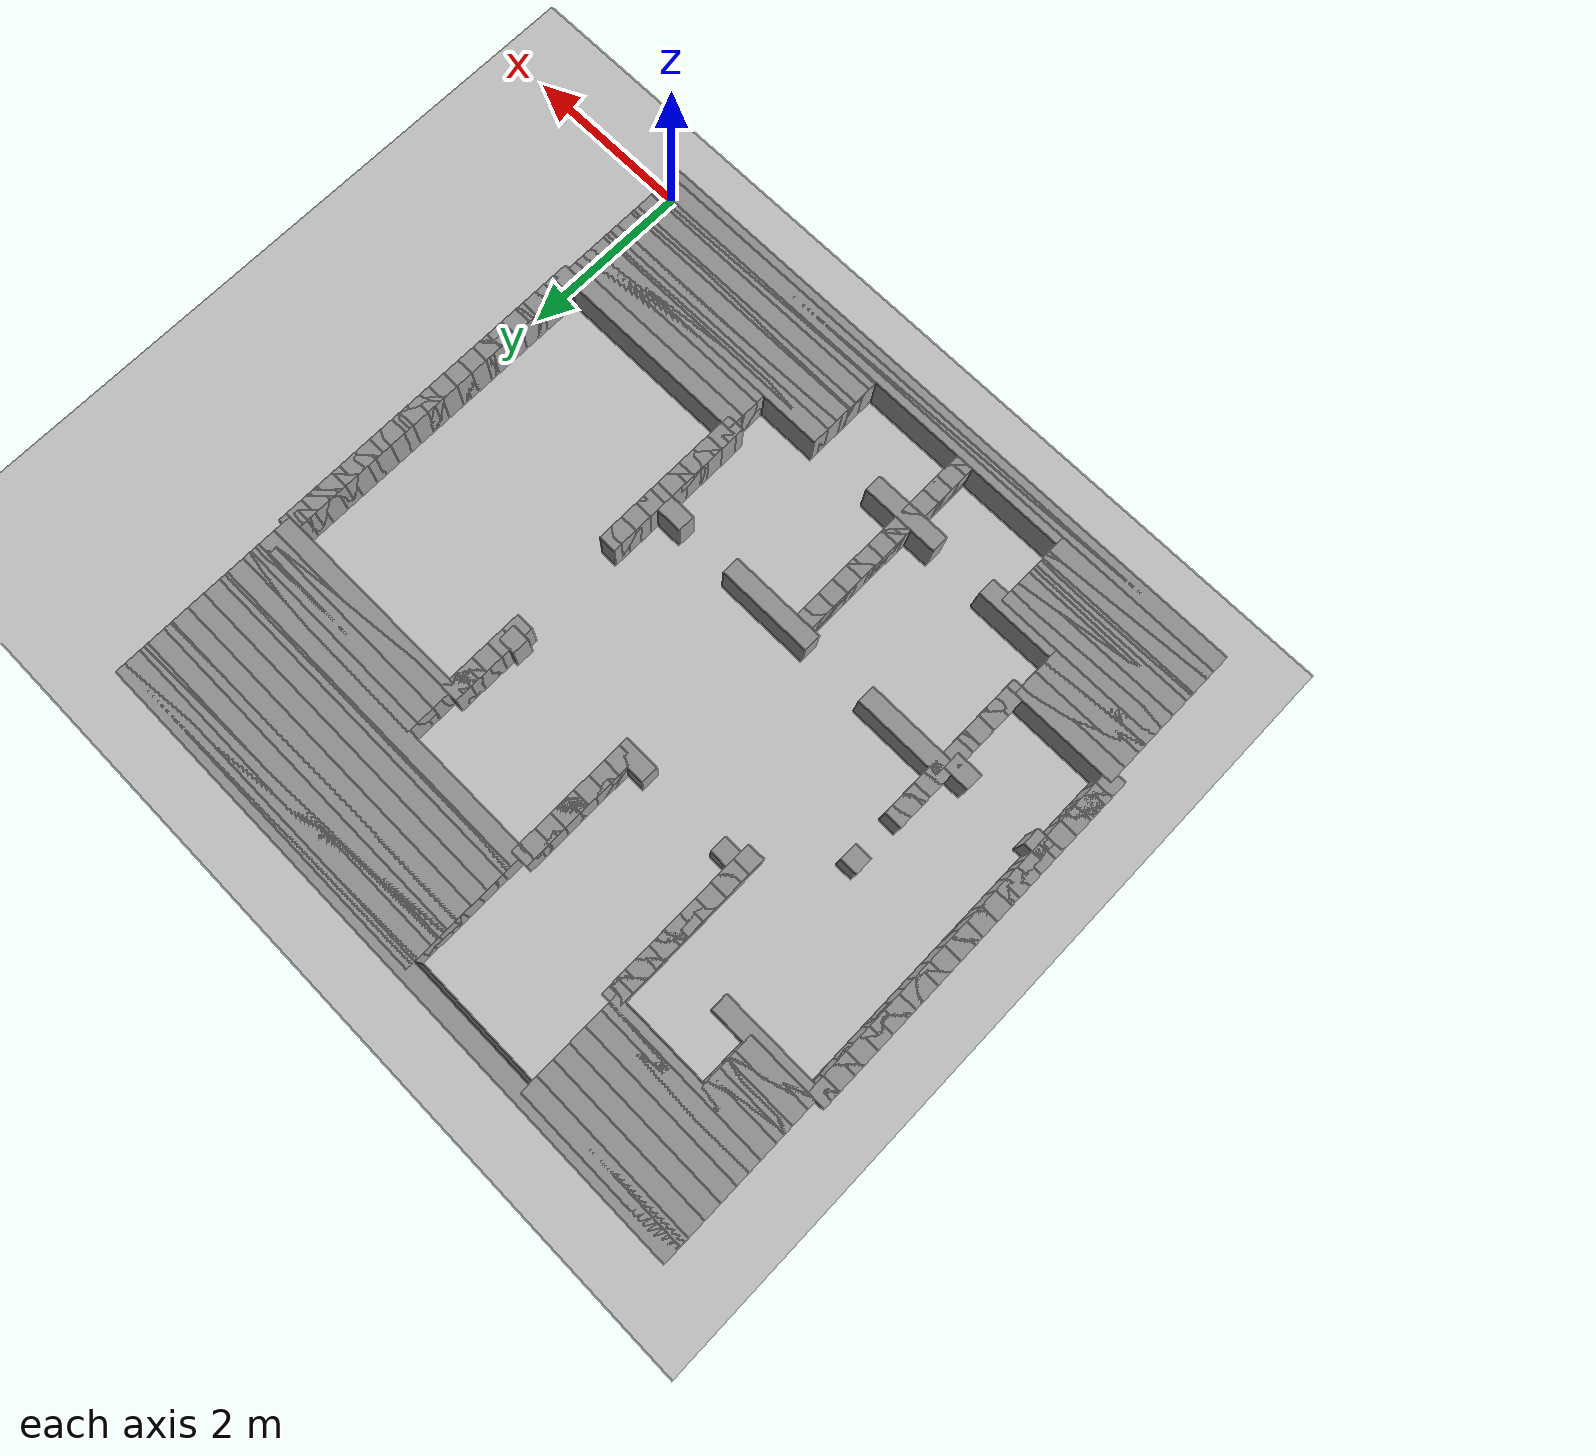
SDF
<?xml version="1.0" ?>
<sdf version="1.6">
	<world name="GridMap">
		<include>
			<uri>model://sun</uri>
		</include>
		<include>
			<uri>model://ground_plane</uri>
		</include>
		<physics type="ode">
			<real_time_update_rate>1000.0</real_time_update_rate>
			<max_step_size>0.001</max_step_size>
			<real_time_factor>1</real_time_factor>
			<ode>
				<solver>
					<type>quick</type>
					<iters>150</iters>
					<precon_iters>0</precon_iters>
					<sor>1.4</sor>
					<use_dynamic_moi_rescaling>1</use_dynamic_moi_rescaling>
				</solver>
				<constraints>
					<cfm>0.00001</cfm>
					<erp>0.2</erp>
					<contact_max_correcting_vel>2000.000000</contact_max_correcting_vel>
					<contact_surface_layer>0.01000</contact_surface_layer>
				</constraints>
			</ode>
		</physics>
		<plugin filename="gz-sim-scene-broadcaster-system" name="gz::sim::systems::SceneBroadcaster"/>
		<gui fullscreen="0">
			<plugin filename="GridConfig" name="Grid">
				<gz-gui>
					<title>Grid</title>
					<cell_count>200</cell_count>
					<cell_size>0.2</cell_size>
					<pose>-75 75 0  0 0 0</pose>
					<color>1 1 1 0.7</color>
				</gz-gui>
			</plugin>
		</gui>
		<model name="GridMap">
			<pose frame="">0 0 0 0 -0 0</pose>
			<link name="Wall_(37.0,0.0)">
				<collision name="Wall_(37.0,0.0)_Collision">
					<geometry>
						<box>
							<size>7.4 0.2 0.5</size>
						</box>
					</geometry>
					<pose frame="">-3.7 0.0 0.25 0 -0 0</pose>
				</collision>
				<inertial>
					<mass>0.5</mass>
					<pose>0 0.01 0 0 0 0</pose>
					<inertia>
						<ixx>0.004</ixx>
						<ixy>0.001</ixy>
						<ixz>0</ixz>
						<iyy>0.006</iyy>
						<iyz>0</iyz>
						<izz>0.007</izz>
					</inertia>
				</inertial>
				<visual name="Wall_(37.0,0.0)_Visual">
					<geometry>
						<box>
							<size>7.4 0.2 0.5</size>
						</box>
					</geometry>
					<pose frame="">-3.7 0.0 0.25 0 -0 0</pose>
					<material>
						<script>
							<uri>file://media/materials/scripts/gazebo.material</uri>
							<name>Gazebo/Grey</name>
						</script>
						<ambient>1 1 1 1</ambient>
					</material>
					<meta>
						<layer>0</layer>
					</meta>
				</visual>
				<pose frame="">0 0 0 0 -0 0</pose>
			</link>
			<link name="Wall_(37.0,1.0)">
				<collision name="Wall_(37.0,1.0)_Collision">
					<geometry>
						<box>
							<size>7.4 0.2 0.5</size>
						</box>
					</geometry>
					<pose frame="">-3.7 0.1 0.25 0 -0 0</pose>
				</collision>
				<inertial>
					<mass>0.5</mass>
					<pose>0 0.01 0 0 0 0</pose>
					<inertia>
						<ixx>0.004</ixx>
						<ixy>0.001</ixy>
						<ixz>0</ixz>
						<iyy>0.006</iyy>
						<iyz>0</iyz>
						<izz>0.007</izz>
					</inertia>
				</inertial>
				<visual name="Wall_(37.0,1.0)_Visual">
					<geometry>
						<box>
							<size>7.4 0.2 0.5</size>
						</box>
					</geometry>
					<pose frame="">-3.7 0.1 0.25 0 -0 0</pose>
					<material>
						<script>
							<uri>file://media/materials/scripts/gazebo.material</uri>
							<name>Gazebo/Grey</name>
						</script>
						<ambient>1 1 1 1</ambient>
					</material>
					<meta>
						<layer>0</layer>
					</meta>
				</visual>
				<pose frame="">0 0 0 0 -0 0</pose>
			</link>
			<link name="Wall_(15.5,2.0)">
				<collision name="Wall_(15.5,2.0)_Collision">
					<geometry>
						<box>
							<size>3.1 0.2 0.5</size>
						</box>
					</geometry>
					<pose frame="">-1.55 0.2 0.25 0 -0 0</pose>
				</collision>
				<inertial>
					<mass>0.5</mass>
					<pose>0 0.01 0 0 0 0</pose>
					<inertia>
						<ixx>0.004</ixx>
						<ixy>0.001</ixy>
						<ixz>0</ixz>
						<iyy>0.006</iyy>
						<iyz>0</iyz>
						<izz>0.007</izz>
					</inertia>
				</inertial>
				<visual name="Wall_(15.5,2.0)_Visual">
					<geometry>
						<box>
							<size>3.1 0.2 0.5</size>
						</box>
					</geometry>
					<pose frame="">-1.55 0.2 0.25 0 -0 0</pose>
					<material>
						<script>
							<uri>file://media/materials/scripts/gazebo.material</uri>
							<name>Gazebo/Grey</name>
						</script>
						<ambient>1 1 1 1</ambient>
					</material>
					<meta>
						<layer>0</layer>
					</meta>
				</visual>
				<pose frame="">0 0 0 0 -0 0</pose>
			</link>
			<link name="Wall_(43.0,2.0)">
				<collision name="Wall_(43.0,2.0)_Collision">
					<geometry>
						<box>
							<size>0.2 0.2 0.5</size>
						</box>
					</geometry>
					<pose frame="">-4.3 0.2 0.25 0 -0 0</pose>
				</collision>
				<inertial>
					<mass>0.5</mass>
					<pose>0 0.01 0 0 0 0</pose>
					<inertia>
						<ixx>0.004</ixx>
						<ixy>0.001</ixy>
						<ixz>0</ixz>
						<iyy>0.006</iyy>
						<iyz>0</iyz>
						<izz>0.007</izz>
					</inertia>
				</inertial>
				<visual name="Wall_(43.0,2.0)_Visual">
					<geometry>
						<box>
							<size>0.2 0.2 0.5</size>
						</box>
					</geometry>
					<pose frame="">-4.3 0.2 0.25 0 -0 0</pose>
					<material>
						<script>
							<uri>file://media/materials/scripts/gazebo.material</uri>
							<name>Gazebo/Grey</name>
						</script>
						<ambient>1 1 1 1</ambient>
					</material>
					<meta>
						<layer>0</layer>
					</meta>
				</visual>
				<pose frame="">0 0 0 0 -0 0</pose>
			</link>
			<link name="Wall_(64.5,2.0)">
				<collision name="Wall_(64.5,2.0)_Collision">
					<geometry>
						<box>
							<size>1.9000000000000001 0.2 0.5</size>
						</box>
					</geometry>
					<pose frame="">-6.45 0.2 0.25 0 -0 0</pose>
				</collision>
				<inertial>
					<mass>0.5</mass>
					<pose>0 0.01 0 0 0 0</pose>
					<inertia>
						<ixx>0.004</ixx>
						<ixy>0.001</ixy>
						<ixz>0</ixz>
						<iyy>0.006</iyy>
						<iyz>0</iyz>
						<izz>0.007</izz>
					</inertia>
				</inertial>
				<visual name="Wall_(64.5,2.0)_Visual">
					<geometry>
						<box>
							<size>1.9000000000000001 0.2 0.5</size>
						</box>
					</geometry>
					<pose frame="">-6.45 0.2 0.25 0 -0 0</pose>
					<material>
						<script>
							<uri>file://media/materials/scripts/gazebo.material</uri>
							<name>Gazebo/Grey</name>
						</script>
						<ambient>1 1 1 1</ambient>
					</material>
					<meta>
						<layer>0</layer>
					</meta>
				</visual>
				<pose frame="">0 0 0 0 -0 0</pose>
			</link>
			<link name="Wall_(15.5,3.0)">
				<collision name="Wall_(15.5,3.0)_Collision">
					<geometry>
						<box>
							<size>3.1 0.2 0.5</size>
						</box>
					</geometry>
					<pose frame="">-1.55 0.30000000000000004 0.25 0 -0 0</pose>
				</collision>
				<inertial>
					<mass>0.5</mass>
					<pose>0 0.01 0 0 0 0</pose>
					<inertia>
						<ixx>0.004</ixx>
						<ixy>0.001</ixy>
						<ixz>0</ixz>
						<iyy>0.006</iyy>
						<iyz>0</iyz>
						<izz>0.007</izz>
					</inertia>
				</inertial>
				<visual name="Wall_(15.5,3.0)_Visual">
					<geometry>
						<box>
							<size>3.1 0.2 0.5</size>
						</box>
					</geometry>
					<pose frame="">-1.55 0.30000000000000004 0.25 0 -0 0</pose>
					<material>
						<script>
							<uri>file://media/materials/scripts/gazebo.material</uri>
							<name>Gazebo/Grey</name>
						</script>
						<ambient>1 1 1 1</ambient>
					</material>
					<meta>
						<layer>0</layer>
					</meta>
				</visual>
				<pose frame="">0 0 0 0 -0 0</pose>
			</link>
			<link name="Wall_(43.0,3.0)">
				<collision name="Wall_(43.0,3.0)_Collision">
					<geometry>
						<box>
							<size>0.2 0.2 0.5</size>
						</box>
					</geometry>
					<pose frame="">-4.3 0.30000000000000004 0.25 0 -0 0</pose>
				</collision>
				<inertial>
					<mass>0.5</mass>
					<pose>0 0.01 0 0 0 0</pose>
					<inertia>
						<ixx>0.004</ixx>
						<ixy>0.001</ixy>
						<ixz>0</ixz>
						<iyy>0.006</iyy>
						<iyz>0</iyz>
						<izz>0.007</izz>
					</inertia>
				</inertial>
				<visual name="Wall_(43.0,3.0)_Visual">
					<geometry>
						<box>
							<size>0.2 0.2 0.5</size>
						</box>
					</geometry>
					<pose frame="">-4.3 0.30000000000000004 0.25 0 -0 0</pose>
					<material>
						<script>
							<uri>file://media/materials/scripts/gazebo.material</uri>
							<name>Gazebo/Grey</name>
						</script>
						<ambient>1 1 1 1</ambient>
					</material>
					<meta>
						<layer>0</layer>
					</meta>
				</visual>
				<pose frame="">0 0 0 0 -0 0</pose>
			</link>
			<link name="Wall_(64.5,3.0)">
				<collision name="Wall_(64.5,3.0)_Collision">
					<geometry>
						<box>
							<size>1.9000000000000001 0.2 0.5</size>
						</box>
					</geometry>
					<pose frame="">-6.45 0.30000000000000004 0.25 0 -0 0</pose>
				</collision>
				<inertial>
					<mass>0.5</mass>
					<pose>0 0.01 0 0 0 0</pose>
					<inertia>
						<ixx>0.004</ixx>
						<ixy>0.001</ixy>
						<ixz>0</ixz>
						<iyy>0.006</iyy>
						<iyz>0</iyz>
						<izz>0.007</izz>
					</inertia>
				</inertial>
				<visual name="Wall_(64.5,3.0)_Visual">
					<geometry>
						<box>
							<size>1.9000000000000001 0.2 0.5</size>
						</box>
					</geometry>
					<pose frame="">-6.45 0.30000000000000004 0.25 0 -0 0</pose>
					<material>
						<script>
							<uri>file://media/materials/scripts/gazebo.material</uri>
							<name>Gazebo/Grey</name>
						</script>
						<ambient>1 1 1 1</ambient>
					</material>
					<meta>
						<layer>0</layer>
					</meta>
				</visual>
				<pose frame="">0 0 0 0 -0 0</pose>
			</link>
			<link name="Wall_(15.5,4.0)">
				<collision name="Wall_(15.5,4.0)_Collision">
					<geometry>
						<box>
							<size>3.1 0.2 0.5</size>
						</box>
					</geometry>
					<pose frame="">-1.55 0.4 0.25 0 -0 0</pose>
				</collision>
				<inertial>
					<mass>0.5</mass>
					<pose>0 0.01 0 0 0 0</pose>
					<inertia>
						<ixx>0.004</ixx>
						<ixy>0.001</ixy>
						<ixz>0</ixz>
						<iyy>0.006</iyy>
						<iyz>0</iyz>
						<izz>0.007</izz>
					</inertia>
				</inertial>
				<visual name="Wall_(15.5,4.0)_Visual">
					<geometry>
						<box>
							<size>3.1 0.2 0.5</size>
						</box>
					</geometry>
					<pose frame="">-1.55 0.4 0.25 0 -0 0</pose>
					<material>
						<script>
							<uri>file://media/materials/scripts/gazebo.material</uri>
							<name>Gazebo/Grey</name>
						</script>
						<ambient>1 1 1 1</ambient>
					</material>
					<meta>
						<layer>0</layer>
					</meta>
				</visual>
				<pose frame="">0 0 0 0 -0 0</pose>
			</link>
			<link name="Wall_(43.0,4.0)">
				<collision name="Wall_(43.0,4.0)_Collision">
					<geometry>
						<box>
							<size>0.2 0.2 0.5</size>
						</box>
					</geometry>
					<pose frame="">-4.3 0.4 0.25 0 -0 0</pose>
				</collision>
				<inertial>
					<mass>0.5</mass>
					<pose>0 0.01 0 0 0 0</pose>
					<inertia>
						<ixx>0.004</ixx>
						<ixy>0.001</ixy>
						<ixz>0</ixz>
						<iyy>0.006</iyy>
						<iyz>0</iyz>
						<izz>0.007</izz>
					</inertia>
				</inertial>
				<visual name="Wall_(43.0,4.0)_Visual">
					<geometry>
						<box>
							<size>0.2 0.2 0.5</size>
						</box>
					</geometry>
					<pose frame="">-4.3 0.4 0.25 0 -0 0</pose>
					<material>
						<script>
							<uri>file://media/materials/scripts/gazebo.material</uri>
							<name>Gazebo/Grey</name>
						</script>
						<ambient>1 1 1 1</ambient>
					</material>
					<meta>
						<layer>0</layer>
					</meta>
				</visual>
				<pose frame="">0 0 0 0 -0 0</pose>
			</link>
			<link name="Wall_(64.5,4.0)">
				<collision name="Wall_(64.5,4.0)_Collision">
					<geometry>
						<box>
							<size>1.9000000000000001 0.2 0.5</size>
						</box>
					</geometry>
					<pose frame="">-6.45 0.4 0.25 0 -0 0</pose>
				</collision>
				<inertial>
					<mass>0.5</mass>
					<pose>0 0.01 0 0 0 0</pose>
					<inertia>
						<ixx>0.004</ixx>
						<ixy>0.001</ixy>
						<ixz>0</ixz>
						<iyy>0.006</iyy>
						<iyz>0</iyz>
						<izz>0.007</izz>
					</inertia>
				</inertial>
				<visual name="Wall_(64.5,4.0)_Visual">
					<geometry>
						<box>
							<size>1.9000000000000001 0.2 0.5</size>
						</box>
					</geometry>
					<pose frame="">-6.45 0.4 0.25 0 -0 0</pose>
					<material>
						<script>
							<uri>file://media/materials/scripts/gazebo.material</uri>
							<name>Gazebo/Grey</name>
						</script>
						<ambient>1 1 1 1</ambient>
					</material>
					<meta>
						<layer>0</layer>
					</meta>
				</visual>
				<pose frame="">0 0 0 0 -0 0</pose>
			</link>
			<link name="Wall_(15.5,5.0)">
				<collision name="Wall_(15.5,5.0)_Collision">
					<geometry>
						<box>
							<size>3.1 0.2 0.5</size>
						</box>
					</geometry>
					<pose frame="">-1.55 0.5 0.25 0 -0 0</pose>
				</collision>
				<inertial>
					<mass>0.5</mass>
					<pose>0 0.01 0 0 0 0</pose>
					<inertia>
						<ixx>0.004</ixx>
						<ixy>0.001</ixy>
						<ixz>0</ixz>
						<iyy>0.006</iyy>
						<iyz>0</iyz>
						<izz>0.007</izz>
					</inertia>
				</inertial>
				<visual name="Wall_(15.5,5.0)_Visual">
					<geometry>
						<box>
							<size>3.1 0.2 0.5</size>
						</box>
					</geometry>
					<pose frame="">-1.55 0.5 0.25 0 -0 0</pose>
					<material>
						<script>
							<uri>file://media/materials/scripts/gazebo.material</uri>
							<name>Gazebo/Grey</name>
						</script>
						<ambient>1 1 1 1</ambient>
					</material>
					<meta>
						<layer>0</layer>
					</meta>
				</visual>
				<pose frame="">0 0 0 0 -0 0</pose>
			</link>
			<link name="Wall_(43.0,5.0)">
				<collision name="Wall_(43.0,5.0)_Collision">
					<geometry>
						<box>
							<size>0.2 0.2 0.5</size>
						</box>
					</geometry>
					<pose frame="">-4.3 0.5 0.25 0 -0 0</pose>
				</collision>
				<inertial>
					<mass>0.5</mass>
					<pose>0 0.01 0 0 0 0</pose>
					<inertia>
						<ixx>0.004</ixx>
						<ixy>0.001</ixy>
						<ixz>0</ixz>
						<iyy>0.006</iyy>
						<iyz>0</iyz>
						<izz>0.007</izz>
					</inertia>
				</inertial>
				<visual name="Wall_(43.0,5.0)_Visual">
					<geometry>
						<box>
							<size>0.2 0.2 0.5</size>
						</box>
					</geometry>
					<pose frame="">-4.3 0.5 0.25 0 -0 0</pose>
					<material>
						<script>
							<uri>file://media/materials/scripts/gazebo.material</uri>
							<name>Gazebo/Grey</name>
						</script>
						<ambient>1 1 1 1</ambient>
					</material>
					<meta>
						<layer>0</layer>
					</meta>
				</visual>
				<pose frame="">0 0 0 0 -0 0</pose>
			</link>
			<link name="Wall_(64.5,5.0)">
				<collision name="Wall_(64.5,5.0)_Collision">
					<geometry>
						<box>
							<size>1.9000000000000001 0.2 0.5</size>
						</box>
					</geometry>
					<pose frame="">-6.45 0.5 0.25 0 -0 0</pose>
				</collision>
				<inertial>
					<mass>0.5</mass>
					<pose>0 0.01 0 0 0 0</pose>
					<inertia>
						<ixx>0.004</ixx>
						<ixy>0.001</ixy>
						<ixz>0</ixz>
						<iyy>0.006</iyy>
						<iyz>0</iyz>
						<izz>0.007</izz>
					</inertia>
				</inertial>
				<visual name="Wall_(64.5,5.0)_Visual">
					<geometry>
						<box>
							<size>1.9000000000000001 0.2 0.5</size>
						</box>
					</geometry>
					<pose frame="">-6.45 0.5 0.25 0 -0 0</pose>
					<material>
						<script>
							<uri>file://media/materials/scripts/gazebo.material</uri>
							<name>Gazebo/Grey</name>
						</script>
						<ambient>1 1 1 1</ambient>
					</material>
					<meta>
						<layer>0</layer>
					</meta>
				</visual>
				<pose frame="">0 0 0 0 -0 0</pose>
			</link>
			<link name="Wall_(15.5,6.0)">
				<collision name="Wall_(15.5,6.0)_Collision">
					<geometry>
						<box>
							<size>3.1 0.2 0.5</size>
						</box>
					</geometry>
					<pose frame="">-1.55 0.6000000000000001 0.25 0 -0 0</pose>
				</collision>
				<inertial>
					<mass>0.5</mass>
					<pose>0 0.01 0 0 0 0</pose>
					<inertia>
						<ixx>0.004</ixx>
						<ixy>0.001</ixy>
						<ixz>0</ixz>
						<iyy>0.006</iyy>
						<iyz>0</iyz>
						<izz>0.007</izz>
					</inertia>
				</inertial>
				<visual name="Wall_(15.5,6.0)_Visual">
					<geometry>
						<box>
							<size>3.1 0.2 0.5</size>
						</box>
					</geometry>
					<pose frame="">-1.55 0.6000000000000001 0.25 0 -0 0</pose>
					<material>
						<script>
							<uri>file://media/materials/scripts/gazebo.material</uri>
							<name>Gazebo/Grey</name>
						</script>
						<ambient>1 1 1 1</ambient>
					</material>
					<meta>
						<layer>0</layer>
					</meta>
				</visual>
				<pose frame="">0 0 0 0 -0 0</pose>
			</link>
			<link name="Wall_(43.0,6.0)">
				<collision name="Wall_(43.0,6.0)_Collision">
					<geometry>
						<box>
							<size>0.2 0.2 0.5</size>
						</box>
					</geometry>
					<pose frame="">-4.3 0.6000000000000001 0.25 0 -0 0</pose>
				</collision>
				<inertial>
					<mass>0.5</mass>
					<pose>0 0.01 0 0 0 0</pose>
					<inertia>
						<ixx>0.004</ixx>
						<ixy>0.001</ixy>
						<ixz>0</ixz>
						<iyy>0.006</iyy>
						<iyz>0</iyz>
						<izz>0.007</izz>
					</inertia>
				</inertial>
				<visual name="Wall_(43.0,6.0)_Visual">
					<geometry>
						<box>
							<size>0.2 0.2 0.5</size>
						</box>
					</geometry>
					<pose frame="">-4.3 0.6000000000000001 0.25 0 -0 0</pose>
					<material>
						<script>
							<uri>file://media/materials/scripts/gazebo.material</uri>
							<name>Gazebo/Grey</name>
						</script>
						<ambient>1 1 1 1</ambient>
					</material>
					<meta>
						<layer>0</layer>
					</meta>
				</visual>
				<pose frame="">0 0 0 0 -0 0</pose>
			</link>
			<link name="Wall_(64.5,6.0)">
				<collision name="Wall_(64.5,6.0)_Collision">
					<geometry>
						<box>
							<size>1.9000000000000001 0.2 0.5</size>
						</box>
					</geometry>
					<pose frame="">-6.45 0.6000000000000001 0.25 0 -0 0</pose>
				</collision>
				<inertial>
					<mass>0.5</mass>
					<pose>0 0.01 0 0 0 0</pose>
					<inertia>
						<ixx>0.004</ixx>
						<ixy>0.001</ixy>
						<ixz>0</ixz>
						<iyy>0.006</iyy>
						<iyz>0</iyz>
						<izz>0.007</izz>
					</inertia>
				</inertial>
				<visual name="Wall_(64.5,6.0)_Visual">
					<geometry>
						<box>
							<size>1.9000000000000001 0.2 0.5</size>
						</box>
					</geometry>
					<pose frame="">-6.45 0.6000000000000001 0.25 0 -0 0</pose>
					<material>
						<script>
							<uri>file://media/materials/scripts/gazebo.material</uri>
							<name>Gazebo/Grey</name>
						</script>
						<ambient>1 1 1 1</ambient>
					</material>
					<meta>
						<layer>0</layer>
					</meta>
				</visual>
				<pose frame="">0 0 0 0 -0 0</pose>
			</link>
			<link name="Wall_(15.5,7.0)">
				<collision name="Wall_(15.5,7.0)_Collision">
					<geometry>
						<box>
							<size>3.1 0.2 0.5</size>
						</box>
					</geometry>
					<pose frame="">-1.55 0.7000000000000001 0.25 0 -0 0</pose>
				</collision>
				<inertial>
					<mass>0.5</mass>
					<pose>0 0.01 0 0 0 0</pose>
					<inertia>
						<ixx>0.004</ixx>
						<ixy>0.001</ixy>
						<ixz>0</ixz>
						<iyy>0.006</iyy>
						<iyz>0</iyz>
						<izz>0.007</izz>
					</inertia>
				</inertial>
				<visual name="Wall_(15.5,7.0)_Visual">
					<geometry>
						<box>
							<size>3.1 0.2 0.5</size>
						</box>
					</geometry>
					<pose frame="">-1.55 0.7000000000000001 0.25 0 -0 0</pose>
					<material>
						<script>
							<uri>file://media/materials/scripts/gazebo.material</uri>
							<name>Gazebo/Grey</name>
						</script>
						<ambient>1 1 1 1</ambient>
					</material>
					<meta>
						<layer>0</layer>
					</meta>
				</visual>
				<pose frame="">0 0 0 0 -0 0</pose>
			</link>
			<link name="Wall_(43.0,7.0)">
				<collision name="Wall_(43.0,7.0)_Collision">
					<geometry>
						<box>
							<size>0.2 0.2 0.5</size>
						</box>
					</geometry>
					<pose frame="">-4.3 0.7000000000000001 0.25 0 -0 0</pose>
				</collision>
				<inertial>
					<mass>0.5</mass>
					<pose>0 0.01 0 0 0 0</pose>
					<inertia>
						<ixx>0.004</ixx>
						<ixy>0.001</ixy>
						<ixz>0</ixz>
						<iyy>0.006</iyy>
						<iyz>0</iyz>
						<izz>0.007</izz>
					</inertia>
				</inertial>
				<visual name="Wall_(43.0,7.0)_Visual">
					<geometry>
						<box>
							<size>0.2 0.2 0.5</size>
						</box>
					</geometry>
					<pose frame="">-4.3 0.7000000000000001 0.25 0 -0 0</pose>
					<material>
						<script>
							<uri>file://media/materials/scripts/gazebo.material</uri>
							<name>Gazebo/Grey</name>
						</script>
						<ambient>1 1 1 1</ambient>
					</material>
					<meta>
						<layer>0</layer>
					</meta>
				</visual>
				<pose frame="">0 0 0 0 -0 0</pose>
			</link>
			<link name="Wall_(64.5,7.0)">
				<collision name="Wall_(64.5,7.0)_Collision">
					<geometry>
						<box>
							<size>1.9000000000000001 0.2 0.5</size>
						</box>
					</geometry>
					<pose frame="">-6.45 0.7000000000000001 0.25 0 -0 0</pose>
				</collision>
				<inertial>
					<mass>0.5</mass>
					<pose>0 0.01 0 0 0 0</pose>
					<inertia>
						<ixx>0.004</ixx>
						<ixy>0.001</ixy>
						<ixz>0</ixz>
						<iyy>0.006</iyy>
						<iyz>0</iyz>
						<izz>0.007</izz>
					</inertia>
				</inertial>
				<visual name="Wall_(64.5,7.0)_Visual">
					<geometry>
						<box>
							<size>1.9000000000000001 0.2 0.5</size>
						</box>
					</geometry>
					<pose frame="">-6.45 0.7000000000000001 0.25 0 -0 0</pose>
					<material>
						<script>
							<uri>file://media/materials/scripts/gazebo.material</uri>
							<name>Gazebo/Grey</name>
						</script>
						<ambient>1 1 1 1</ambient>
					</material>
					<meta>
						<layer>0</layer>
					</meta>
				</visual>
				<pose frame="">0 0 0 0 -0 0</pose>
			</link>
			<link name="Wall_(15.5,8.0)">
				<collision name="Wall_(15.5,8.0)_Collision">
					<geometry>
						<box>
							<size>3.1 0.2 0.5</size>
						</box>
					</geometry>
					<pose frame="">-1.55 0.8 0.25 0 -0 0</pose>
				</collision>
				<inertial>
					<mass>0.5</mass>
					<pose>0 0.01 0 0 0 0</pose>
					<inertia>
						<ixx>0.004</ixx>
						<ixy>0.001</ixy>
						<ixz>0</ixz>
						<iyy>0.006</iyy>
						<iyz>0</iyz>
						<izz>0.007</izz>
					</inertia>
				</inertial>
				<visual name="Wall_(15.5,8.0)_Visual">
					<geometry>
						<box>
							<size>3.1 0.2 0.5</size>
						</box>
					</geometry>
					<pose frame="">-1.55 0.8 0.25 0 -0 0</pose>
					<material>
						<script>
							<uri>file://media/materials/scripts/gazebo.material</uri>
							<name>Gazebo/Grey</name>
						</script>
						<ambient>1 1 1 1</ambient>
					</material>
					<meta>
						<layer>0</layer>
					</meta>
				</visual>
				<pose frame="">0 0 0 0 -0 0</pose>
			</link>
			<link name="Wall_(43.0,8.0)">
				<collision name="Wall_(43.0,8.0)_Collision">
					<geometry>
						<box>
							<size>0.2 0.2 0.5</size>
						</box>
					</geometry>
					<pose frame="">-4.3 0.8 0.25 0 -0 0</pose>
				</collision>
				<inertial>
					<mass>0.5</mass>
					<pose>0 0.01 0 0 0 0</pose>
					<inertia>
						<ixx>0.004</ixx>
						<ixy>0.001</ixy>
						<ixz>0</ixz>
						<iyy>0.006</iyy>
						<iyz>0</iyz>
						<izz>0.007</izz>
					</inertia>
				</inertial>
				<visual name="Wall_(43.0,8.0)_Visual">
					<geometry>
						<box>
							<size>0.2 0.2 0.5</size>
						</box>
					</geometry>
					<pose frame="">-4.3 0.8 0.25 0 -0 0</pose>
					<material>
						<script>
							<uri>file://media/materials/scripts/gazebo.material</uri>
							<name>Gazebo/Grey</name>
						</script>
						<ambient>1 1 1 1</ambient>
					</material>
					<meta>
						<layer>0</layer>
					</meta>
				</visual>
				<pose frame="">0 0 0 0 -0 0</pose>
			</link>
			<link name="Wall_(64.5,8.0)">
				<collision name="Wall_(64.5,8.0)_Collision">
					<geometry>
						<box>
							<size>1.9000000000000001 0.2 0.5</size>
						</box>
					</geometry>
					<pose frame="">-6.45 0.8 0.25 0 -0 0</pose>
				</collision>
				<inertial>
					<mass>0.5</mass>
					<pose>0 0.01 0 0 0 0</pose>
					<inertia>
						<ixx>0.004</ixx>
						<ixy>0.001</ixy>
						<ixz>0</ixz>
						<iyy>0.006</iyy>
						<iyz>0</iyz>
						<izz>0.007</izz>
					</inertia>
				</inertial>
				<visual name="Wall_(64.5,8.0)_Visual">
					<geometry>
						<box>
							<size>1.9000000000000001 0.2 0.5</size>
						</box>
					</geometry>
					<pose frame="">-6.45 0.8 0.25 0 -0 0</pose>
					<material>
						<script>
							<uri>file://media/materials/scripts/gazebo.material</uri>
							<name>Gazebo/Grey</name>
						</script>
						<ambient>1 1 1 1</ambient>
					</material>
					<meta>
						<layer>0</layer>
					</meta>
				</visual>
				<pose frame="">0 0 0 0 -0 0</pose>
			</link>
			<link name="Wall_(15.5,9.0)">
				<collision name="Wall_(15.5,9.0)_Collision">
					<geometry>
						<box>
							<size>3.1 0.2 0.5</size>
						</box>
					</geometry>
					<pose frame="">-1.55 0.9 0.25 0 -0 0</pose>
				</collision>
				<inertial>
					<mass>0.5</mass>
					<pose>0 0.01 0 0 0 0</pose>
					<inertia>
						<ixx>0.004</ixx>
						<ixy>0.001</ixy>
						<ixz>0</ixz>
						<iyy>0.006</iyy>
						<iyz>0</iyz>
						<izz>0.007</izz>
					</inertia>
				</inertial>
				<visual name="Wall_(15.5,9.0)_Visual">
					<geometry>
						<box>
							<size>3.1 0.2 0.5</size>
						</box>
					</geometry>
					<pose frame="">-1.55 0.9 0.25 0 -0 0</pose>
					<material>
						<script>
							<uri>file://media/materials/scripts/gazebo.material</uri>
							<name>Gazebo/Grey</name>
						</script>
						<ambient>1 1 1 1</ambient>
					</material>
					<meta>
						<layer>0</layer>
					</meta>
				</visual>
				<pose frame="">0 0 0 0 -0 0</pose>
			</link>
			<link name="Wall_(43.0,9.0)">
				<collision name="Wall_(43.0,9.0)_Collision">
					<geometry>
						<box>
							<size>0.2 0.2 0.5</size>
						</box>
					</geometry>
					<pose frame="">-4.3 0.9 0.25 0 -0 0</pose>
				</collision>
				<inertial>
					<mass>0.5</mass>
					<pose>0 0.01 0 0 0 0</pose>
					<inertia>
						<ixx>0.004</ixx>
						<ixy>0.001</ixy>
						<ixz>0</ixz>
						<iyy>0.006</iyy>
						<iyz>0</iyz>
						<izz>0.007</izz>
					</inertia>
				</inertial>
				<visual name="Wall_(43.0,9.0)_Visual">
					<geometry>
						<box>
							<size>0.2 0.2 0.5</size>
						</box>
					</geometry>
					<pose frame="">-4.3 0.9 0.25 0 -0 0</pose>
					<material>
						<script>
							<uri>file://media/materials/scripts/gazebo.material</uri>
							<name>Gazebo/Grey</name>
						</script>
						<ambient>1 1 1 1</ambient>
					</material>
					<meta>
						<layer>0</layer>
					</meta>
				</visual>
				<pose frame="">0 0 0 0 -0 0</pose>
			</link>
			<link name="Wall_(64.5,9.0)">
				<collision name="Wall_(64.5,9.0)_Collision">
					<geometry>
						<box>
							<size>1.9000000000000001 0.2 0.5</size>
						</box>
					</geometry>
					<pose frame="">-6.45 0.9 0.25 0 -0 0</pose>
				</collision>
				<inertial>
					<mass>0.5</mass>
					<pose>0 0.01 0 0 0 0</pose>
					<inertia>
						<ixx>0.004</ixx>
						<ixy>0.001</ixy>
						<ixz>0</ixz>
						<iyy>0.006</iyy>
						<iyz>0</iyz>
						<izz>0.007</izz>
					</inertia>
				</inertial>
				<visual name="Wall_(64.5,9.0)_Visual">
					<geometry>
						<box>
							<size>1.9000000000000001 0.2 0.5</size>
						</box>
					</geometry>
					<pose frame="">-6.45 0.9 0.25 0 -0 0</pose>
					<material>
						<script>
							<uri>file://media/materials/scripts/gazebo.material</uri>
							<name>Gazebo/Grey</name>
						</script>
						<ambient>1 1 1 1</ambient>
					</material>
					<meta>
						<layer>0</layer>
					</meta>
				</visual>
				<pose frame="">0 0 0 0 -0 0</pose>
			</link>
			<link name="Wall_(15.5,10.0)">
				<collision name="Wall_(15.5,10.0)_Collision">
					<geometry>
						<box>
							<size>3.1 0.2 0.5</size>
						</box>
					</geometry>
					<pose frame="">-1.55 1.0 0.25 0 -0 0</pose>
				</collision>
				<inertial>
					<mass>0.5</mass>
					<pose>0 0.01 0 0 0 0</pose>
					<inertia>
						<ixx>0.004</ixx>
						<ixy>0.001</ixy>
						<ixz>0</ixz>
						<iyy>0.006</iyy>
						<iyz>0</iyz>
						<izz>0.007</izz>
					</inertia>
				</inertial>
				<visual name="Wall_(15.5,10.0)_Visual">
					<geometry>
						<box>
							<size>3.1 0.2 0.5</size>
						</box>
					</geometry>
					<pose frame="">-1.55 1.0 0.25 0 -0 0</pose>
					<material>
						<script>
							<uri>file://media/materials/scripts/gazebo.material</uri>
							<name>Gazebo/Grey</name>
						</script>
						<ambient>1 1 1 1</ambient>
					</material>
					<meta>
						<layer>0</layer>
					</meta>
				</visual>
				<pose frame="">0 0 0 0 -0 0</pose>
			</link>
			<link name="Wall_(42.5,10.0)">
				<collision name="Wall_(42.5,10.0)_Collision">
					<geometry>
						<box>
							<size>0.9 0.2 0.5</size>
						</box>
					</geometry>
					<pose frame="">-4.25 1.0 0.25 0 -0 0</pose>
				</collision>
				<inertial>
					<mass>0.5</mass>
					<pose>0 0.01 0 0 0 0</pose>
					<inertia>
						<ixx>0.004</ixx>
						<ixy>0.001</ixy>
						<ixz>0</ixz>
						<iyy>0.006</iyy>
						<iyz>0</iyz>
						<izz>0.007</izz>
					</inertia>
				</inertial>
				<visual name="Wall_(42.5,10.0)_Visual">
					<geometry>
						<box>
							<size>0.9 0.2 0.5</size>
						</box>
					</geometry>
					<pose frame="">-4.25 1.0 0.25 0 -0 0</pose>
					<material>
						<script>
							<uri>file://media/materials/scripts/gazebo.material</uri>
							<name>Gazebo/Grey</name>
						</script>
						<ambient>1 1 1 1</ambient>
					</material>
					<meta>
						<layer>0</layer>
					</meta>
				</visual>
				<pose frame="">0 0 0 0 -0 0</pose>
			</link>
			<link name="Wall_(63.5,10.0)">
				<collision name="Wall_(63.5,10.0)_Collision">
					<geometry>
						<box>
							<size>2.1 0.2 0.5</size>
						</box>
					</geometry>
					<pose frame="">-6.3500000000000005 1.0 0.25 0 -0 0</pose>
				</collision>
				<inertial>
					<mass>0.5</mass>
					<pose>0 0.01 0 0 0 0</pose>
					<inertia>
						<ixx>0.004</ixx>
						<ixy>0.001</ixy>
						<ixz>0</ixz>
						<iyy>0.006</iyy>
						<iyz>0</iyz>
						<izz>0.007</izz>
					</inertia>
				</inertial>
				<visual name="Wall_(63.5,10.0)_Visual">
					<geometry>
						<box>
							<size>2.1 0.2 0.5</size>
						</box>
					</geometry>
					<pose frame="">-6.3500000000000005 1.0 0.25 0 -0 0</pose>
					<material>
						<script>
							<uri>file://media/materials/scripts/gazebo.material</uri>
							<name>Gazebo/Grey</name>
						</script>
						<ambient>1 1 1 1</ambient>
					</material>
					<meta>
						<layer>0</layer>
					</meta>
				</visual>
				<pose frame="">0 0 0 0 -0 0</pose>
			</link>
			<link name="Wall_(12.0,11.0)">
				<collision name="Wall_(12.0,11.0)_Collision">
					<geometry>
						<box>
							<size>2.4000000000000004 0.2 0.5</size>
						</box>
					</geometry>
					<pose frame="">-1.2000000000000002 1.1 0.25 0 -0 0</pose>
				</collision>
				<inertial>
					<mass>0.5</mass>
					<pose>0 0.01 0 0 0 0</pose>
					<inertia>
						<ixx>0.004</ixx>
						<ixy>0.001</ixy>
						<ixz>0</ixz>
						<iyy>0.006</iyy>
						<iyz>0</iyz>
						<izz>0.007</izz>
					</inertia>
				</inertial>
				<visual name="Wall_(12.0,11.0)_Visual">
					<geometry>
						<box>
							<size>2.4000000000000004 0.2 0.5</size>
						</box>
					</geometry>
					<pose frame="">-1.2000000000000002 1.1 0.25 0 -0 0</pose>
					<material>
						<script>
							<uri>file://media/materials/scripts/gazebo.material</uri>
							<name>Gazebo/Grey</name>
						</script>
						<ambient>1 1 1 1</ambient>
					</material>
					<meta>
						<layer>0</layer>
					</meta>
				</visual>
				<pose frame="">0 0 0 0 -0 0</pose>
			</link>
			<link name="Wall_(43.0,11.0)">
				<collision name="Wall_(43.0,11.0)_Collision">
					<geometry>
						<box>
							<size>0.2 0.2 0.5</size>
						</box>
					</geometry>
					<pose frame="">-4.3 1.1 0.25 0 -0 0</pose>
				</collision>
				<inertial>
					<mass>0.5</mass>
					<pose>0 0.01 0 0 0 0</pose>
					<inertia>
						<ixx>0.004</ixx>
						<ixy>0.001</ixy>
						<ixz>0</ixz>
						<iyy>0.006</iyy>
						<iyz>0</iyz>
						<izz>0.007</izz>
					</inertia>
				</inertial>
				<visual name="Wall_(43.0,11.0)_Visual">
					<geometry>
						<box>
							<size>0.2 0.2 0.5</size>
						</box>
					</geometry>
					<pose frame="">-4.3 1.1 0.25 0 -0 0</pose>
					<material>
						<script>
							<uri>file://media/materials/scripts/gazebo.material</uri>
							<name>Gazebo/Grey</name>
						</script>
						<ambient>1 1 1 1</ambient>
					</material>
					<meta>
						<layer>0</layer>
					</meta>
				</visual>
				<pose frame="">0 0 0 0 -0 0</pose>
			</link>
			<link name="Wall_(68.0,11.0)">
				<collision name="Wall_(68.0,11.0)_Collision">
					<geometry>
						<box>
							<size>1.2000000000000002 0.2 0.5</size>
						</box>
					</geometry>
					<pose frame="">-6.800000000000001 1.1 0.25 0 -0 0</pose>
				</collision>
				<inertial>
					<mass>0.5</mass>
					<pose>0 0.01 0 0 0 0</pose>
					<inertia>
						<ixx>0.004</ixx>
						<ixy>0.001</ixy>
						<ixz>0</ixz>
						<iyy>0.006</iyy>
						<iyz>0</iyz>
						<izz>0.007</izz>
					</inertia>
				</inertial>
				<visual name="Wall_(68.0,11.0)_Visual">
					<geometry>
						<box>
							<size>1.2000000000000002 0.2 0.5</size>
						</box>
					</geometry>
					<pose frame="">-6.800000000000001 1.1 0.25 0 -0 0</pose>
					<material>
						<script>
							<uri>file://media/materials/scripts/gazebo.material</uri>
							<name>Gazebo/Grey</name>
						</script>
						<ambient>1 1 1 1</ambient>
					</material>
					<meta>
						<layer>0</layer>
					</meta>
				</visual>
				<pose frame="">0 0 0 0 -0 0</pose>
			</link>
			<link name="Wall_(12.0,12.0)">
				<collision name="Wall_(12.0,12.0)_Collision">
					<geometry>
						<box>
							<size>2.4000000000000004 0.2 0.5</size>
						</box>
					</geometry>
					<pose frame="">-1.2000000000000002 1.2000000000000002 0.25 0 -0 0</pose>
				</collision>
				<inertial>
					<mass>0.5</mass>
					<pose>0 0.01 0 0 0 0</pose>
					<inertia>
						<ixx>0.004</ixx>
						<ixy>0.001</ixy>
						<ixz>0</ixz>
						<iyy>0.006</iyy>
						<iyz>0</iyz>
						<izz>0.007</izz>
					</inertia>
				</inertial>
				<visual name="Wall_(12.0,12.0)_Visual">
					<geometry>
						<box>
							<size>2.4000000000000004 0.2 0.5</size>
						</box>
					</geometry>
					<pose frame="">-1.2000000000000002 1.2000000000000002 0.25 0 -0 0</pose>
					<material>
						<script>
							<uri>file://media/materials/scripts/gazebo.material</uri>
							<name>Gazebo/Grey</name>
						</script>
						<ambient>1 1 1 1</ambient>
					</material>
					<meta>
						<layer>0</layer>
					</meta>
				</visual>
				<pose frame="">0 0 0 0 -0 0</pose>
			</link>
			<link name="Wall_(43.0,12.0)">
				<collision name="Wall_(43.0,12.0)_Collision">
					<geometry>
						<box>
							<size>0.2 0.2 0.5</size>
						</box>
					</geometry>
					<pose frame="">-4.3 1.2000000000000002 0.25 0 -0 0</pose>
				</collision>
				<inertial>
					<mass>0.5</mass>
					<pose>0 0.01 0 0 0 0</pose>
					<inertia>
						<ixx>0.004</ixx>
						<ixy>0.001</ixy>
						<ixz>0</ixz>
						<iyy>0.006</iyy>
						<iyz>0</iyz>
						<izz>0.007</izz>
					</inertia>
				</inertial>
				<visual name="Wall_(43.0,12.0)_Visual">
					<geometry>
						<box>
							<size>0.2 0.2 0.5</size>
						</box>
					</geometry>
					<pose frame="">-4.3 1.2000000000000002 0.25 0 -0 0</pose>
					<material>
						<script>
							<uri>file://media/materials/scripts/gazebo.material</uri>
							<name>Gazebo/Grey</name>
						</script>
						<ambient>1 1 1 1</ambient>
					</material>
					<meta>
						<layer>0</layer>
					</meta>
				</visual>
				<pose frame="">0 0 0 0 -0 0</pose>
			</link>
			<link name="Wall_(68.0,12.0)">
				<collision name="Wall_(68.0,12.0)_Collision">
					<geometry>
						<box>
							<size>1.2000000000000002 0.2 0.5</size>
						</box>
					</geometry>
					<pose frame="">-6.800000000000001 1.2000000000000002 0.25 0 -0 0</pose>
				</collision>
				<inertial>
					<mass>0.5</mass>
					<pose>0 0.01 0 0 0 0</pose>
					<inertia>
						<ixx>0.004</ixx>
						<ixy>0.001</ixy>
						<ixz>0</ixz>
						<iyy>0.006</iyy>
						<iyz>0</iyz>
						<izz>0.007</izz>
					</inertia>
				</inertial>
				<visual name="Wall_(68.0,12.0)_Visual">
					<geometry>
						<box>
							<size>1.2000000000000002 0.2 0.5</size>
						</box>
					</geometry>
					<pose frame="">-6.800000000000001 1.2000000000000002 0.25 0 -0 0</pose>
					<material>
						<script>
							<uri>file://media/materials/scripts/gazebo.material</uri>
							<name>Gazebo/Grey</name>
						</script>
						<ambient>1 1 1 1</ambient>
					</material>
					<meta>
						<layer>0</layer>
					</meta>
				</visual>
				<pose frame="">0 0 0 0 -0 0</pose>
			</link>
			<link name="Wall_(12.0,13.0)">
				<collision name="Wall_(12.0,13.0)_Collision">
					<geometry>
						<box>
							<size>2.4000000000000004 0.2 0.5</size>
						</box>
					</geometry>
					<pose frame="">-1.2000000000000002 1.3 0.25 0 -0 0</pose>
				</collision>
				<inertial>
					<mass>0.5</mass>
					<pose>0 0.01 0 0 0 0</pose>
					<inertia>
						<ixx>0.004</ixx>
						<ixy>0.001</ixy>
						<ixz>0</ixz>
						<iyy>0.006</iyy>
						<iyz>0</iyz>
						<izz>0.007</izz>
					</inertia>
				</inertial>
				<visual name="Wall_(12.0,13.0)_Visual">
					<geometry>
						<box>
							<size>2.4000000000000004 0.2 0.5</size>
						</box>
					</geometry>
					<pose frame="">-1.2000000000000002 1.3 0.25 0 -0 0</pose>
					<material>
						<script>
							<uri>file://media/materials/scripts/gazebo.material</uri>
							<name>Gazebo/Grey</name>
						</script>
						<ambient>1 1 1 1</ambient>
					</material>
					<meta>
						<layer>0</layer>
					</meta>
				</visual>
				<pose frame="">0 0 0 0 -0 0</pose>
			</link>
			<link name="Wall_(43.0,13.0)">
				<collision name="Wall_(43.0,13.0)_Collision">
					<geometry>
						<box>
							<size>0.2 0.2 0.5</size>
						</box>
					</geometry>
					<pose frame="">-4.3 1.3 0.25 0 -0 0</pose>
				</collision>
				<inertial>
					<mass>0.5</mass>
					<pose>0 0.01 0 0 0 0</pose>
					<inertia>
						<ixx>0.004</ixx>
						<ixy>0.001</ixy>
						<ixz>0</ixz>
						<iyy>0.006</iyy>
						<iyz>0</iyz>
						<izz>0.007</izz>
					</inertia>
				</inertial>
				<visual name="Wall_(43.0,13.0)_Visual">
					<geometry>
						<box>
							<size>0.2 0.2 0.5</size>
						</box>
					</geometry>
					<pose frame="">-4.3 1.3 0.25 0 -0 0</pose>
					<material>
						<script>
							<uri>file://media/materials/scripts/gazebo.material</uri>
							<name>Gazebo/Grey</name>
						</script>
						<ambient>1 1 1 1</ambient>
					</material>
					<meta>
						<layer>0</layer>
					</meta>
				</visual>
				<pose frame="">0 0 0 0 -0 0</pose>
			</link>
			<link name="Wall_(68.0,13.0)">
				<collision name="Wall_(68.0,13.0)_Collision">
					<geometry>
						<box>
							<size>1.2000000000000002 0.2 0.5</size>
						</box>
					</geometry>
					<pose frame="">-6.800000000000001 1.3 0.25 0 -0 0</pose>
				</collision>
				<inertial>
					<mass>0.5</mass>
					<pose>0 0.01 0 0 0 0</pose>
					<inertia>
						<ixx>0.004</ixx>
						<ixy>0.001</ixy>
						<ixz>0</ixz>
						<iyy>0.006</iyy>
						<iyz>0</iyz>
						<izz>0.007</izz>
					</inertia>
				</inertial>
				<visual name="Wall_(68.0,13.0)_Visual">
					<geometry>
						<box>
							<size>1.2000000000000002 0.2 0.5</size>
						</box>
					</geometry>
					<pose frame="">-6.800000000000001 1.3 0.25 0 -0 0</pose>
					<material>
						<script>
							<uri>file://media/materials/scripts/gazebo.material</uri>
							<name>Gazebo/Grey</name>
						</script>
						<ambient>1 1 1 1</ambient>
					</material>
					<meta>
						<layer>0</layer>
					</meta>
				</visual>
				<pose frame="">0 0 0 0 -0 0</pose>
			</link>
			<link name="Wall_(12.0,14.0)">
				<collision name="Wall_(12.0,14.0)_Collision">
					<geometry>
						<box>
							<size>2.4000000000000004 0.2 0.5</size>
						</box>
					</geometry>
					<pose frame="">-1.2000000000000002 1.4000000000000001 0.25 0 -0 0</pose>
				</collision>
				<inertial>
					<mass>0.5</mass>
					<pose>0 0.01 0 0 0 0</pose>
					<inertia>
						<ixx>0.004</ixx>
						<ixy>0.001</ixy>
						<ixz>0</ixz>
						<iyy>0.006</iyy>
						<iyz>0</iyz>
						<izz>0.007</izz>
					</inertia>
				</inertial>
				<visual name="Wall_(12.0,14.0)_Visual">
					<geometry>
						<box>
							<size>2.4000000000000004 0.2 0.5</size>
						</box>
					</geometry>
					<pose frame="">-1.2000000000000002 1.4000000000000001 0.25 0 -0 0</pose>
					<material>
						<script>
							<uri>file://media/materials/scripts/gazebo.material</uri>
							<name>Gazebo/Grey</name>
						</script>
						<ambient>1 1 1 1</ambient>
					</material>
					<meta>
						<layer>0</layer>
					</meta>
				</visual>
				<pose frame="">0 0 0 0 -0 0</pose>
			</link>
			<link name="Wall_(43.0,14.0)">
				<collision name="Wall_(43.0,14.0)_Collision">
					<geometry>
						<box>
							<size>0.2 0.2 0.5</size>
						</box>
					</geometry>
					<pose frame="">-4.3 1.4000000000000001 0.25 0 -0 0</pose>
				</collision>
				<inertial>
					<mass>0.5</mass>
					<pose>0 0.01 0 0 0 0</pose>
					<inertia>
						<ixx>0.004</ixx>
						<ixy>0.001</ixy>
						<ixz>0</ixz>
						<iyy>0.006</iyy>
						<iyz>0</iyz>
						<izz>0.007</izz>
					</inertia>
				</inertial>
				<visual name="Wall_(43.0,14.0)_Visual">
					<geometry>
						<box>
							<size>0.2 0.2 0.5</size>
						</box>
					</geometry>
					<pose frame="">-4.3 1.4000000000000001 0.25 0 -0 0</pose>
					<material>
						<script>
							<uri>file://media/materials/scripts/gazebo.material</uri>
							<name>Gazebo/Grey</name>
						</script>
						<ambient>1 1 1 1</ambient>
					</material>
					<meta>
						<layer>0</layer>
					</meta>
				</visual>
				<pose frame="">0 0 0 0 -0 0</pose>
			</link>
			<link name="Wall_(68.0,14.0)">
				<collision name="Wall_(68.0,14.0)_Collision">
					<geometry>
						<box>
							<size>1.2000000000000002 0.2 0.5</size>
						</box>
					</geometry>
					<pose frame="">-6.800000000000001 1.4000000000000001 0.25 0 -0 0</pose>
				</collision>
				<inertial>
					<mass>0.5</mass>
					<pose>0 0.01 0 0 0 0</pose>
					<inertia>
						<ixx>0.004</ixx>
						<ixy>0.001</ixy>
						<ixz>0</ixz>
						<iyy>0.006</iyy>
						<iyz>0</iyz>
						<izz>0.007</izz>
					</inertia>
				</inertial>
				<visual name="Wall_(68.0,14.0)_Visual">
					<geometry>
						<box>
							<size>1.2000000000000002 0.2 0.5</size>
						</box>
					</geometry>
					<pose frame="">-6.800000000000001 1.4000000000000001 0.25 0 -0 0</pose>
					<material>
						<script>
							<uri>file://media/materials/scripts/gazebo.material</uri>
							<name>Gazebo/Grey</name>
						</script>
						<ambient>1 1 1 1</ambient>
					</material>
					<meta>
						<layer>0</layer>
					</meta>
				</visual>
				<pose frame="">0 0 0 0 -0 0</pose>
			</link>
			<link name="Wall_(12.0,15.0)">
				<collision name="Wall_(12.0,15.0)_Collision">
					<geometry>
						<box>
							<size>2.4000000000000004 0.2 0.5</size>
						</box>
					</geometry>
					<pose frame="">-1.2000000000000002 1.5 0.25 0 -0 0</pose>
				</collision>
				<inertial>
					<mass>0.5</mass>
					<pose>0 0.01 0 0 0 0</pose>
					<inertia>
						<ixx>0.004</ixx>
						<ixy>0.001</ixy>
						<ixz>0</ixz>
						<iyy>0.006</iyy>
						<iyz>0</iyz>
						<izz>0.007</izz>
					</inertia>
				</inertial>
				<visual name="Wall_(12.0,15.0)_Visual">
					<geometry>
						<box>
							<size>2.4000000000000004 0.2 0.5</size>
						</box>
					</geometry>
					<pose frame="">-1.2000000000000002 1.5 0.25 0 -0 0</pose>
					<material>
						<script>
							<uri>file://media/materials/scripts/gazebo.material</uri>
							<name>Gazebo/Grey</name>
						</script>
						<ambient>1 1 1 1</ambient>
					</material>
					<meta>
						<layer>0</layer>
					</meta>
				</visual>
				<pose frame="">0 0 0 0 -0 0</pose>
			</link>
			<link name="Wall_(43.0,15.0)">
				<collision name="Wall_(43.0,15.0)_Collision">
					<geometry>
						<box>
							<size>0.2 0.2 0.5</size>
						</box>
					</geometry>
					<pose frame="">-4.3 1.5 0.25 0 -0 0</pose>
				</collision>
				<inertial>
					<mass>0.5</mass>
					<pose>0 0.01 0 0 0 0</pose>
					<inertia>
						<ixx>0.004</ixx>
						<ixy>0.001</ixy>
						<ixz>0</ixz>
						<iyy>0.006</iyy>
						<iyz>0</iyz>
						<izz>0.007</izz>
					</inertia>
				</inertial>
				<visual name="Wall_(43.0,15.0)_Visual">
					<geometry>
						<box>
							<size>0.2 0.2 0.5</size>
						</box>
					</geometry>
					<pose frame="">-4.3 1.5 0.25 0 -0 0</pose>
					<material>
						<script>
							<uri>file://media/materials/scripts/gazebo.material</uri>
							<name>Gazebo/Grey</name>
						</script>
						<ambient>1 1 1 1</ambient>
					</material>
					<meta>
						<layer>0</layer>
					</meta>
				</visual>
				<pose frame="">0 0 0 0 -0 0</pose>
			</link>
			<link name="Wall_(68.0,15.0)">
				<collision name="Wall_(68.0,15.0)_Collision">
					<geometry>
						<box>
							<size>1.2000000000000002 0.2 0.5</size>
						</box>
					</geometry>
					<pose frame="">-6.800000000000001 1.5 0.25 0 -0 0</pose>
				</collision>
				<inertial>
					<mass>0.5</mass>
					<pose>0 0.01 0 0 0 0</pose>
					<inertia>
						<ixx>0.004</ixx>
						<ixy>0.001</ixy>
						<ixz>0</ixz>
						<iyy>0.006</iyy>
						<iyz>0</iyz>
						<izz>0.007</izz>
					</inertia>
				</inertial>
				<visual name="Wall_(68.0,15.0)_Visual">
					<geometry>
						<box>
							<size>1.2000000000000002 0.2 0.5</size>
						</box>
					</geometry>
					<pose frame="">-6.800000000000001 1.5 0.25 0 -0 0</pose>
					<material>
						<script>
							<uri>file://media/materials/scripts/gazebo.material</uri>
							<name>Gazebo/Grey</name>
						</script>
						<ambient>1 1 1 1</ambient>
					</material>
					<meta>
						<layer>0</layer>
					</meta>
				</visual>
				<pose frame="">0 0 0 0 -0 0</pose>
			</link>
			<link name="Wall_(0.5,16.0)">
				<collision name="Wall_(0.5,16.0)_Collision">
					<geometry>
						<box>
							<size>0.2 0.2 0.5</size>
						</box>
					</geometry>
					<pose frame="">-0.05 1.6 0.25 0 -0 0</pose>
				</collision>
				<inertial>
					<mass>0.5</mass>
					<pose>0 0.01 0 0 0 0</pose>
					<inertia>
						<ixx>0.004</ixx>
						<ixy>0.001</ixy>
						<ixz>0</ixz>
						<iyy>0.006</iyy>
						<iyz>0</iyz>
						<izz>0.007</izz>
					</inertia>
				</inertial>
				<visual name="Wall_(0.5,16.0)_Visual">
					<geometry>
						<box>
							<size>0.2 0.2 0.5</size>
						</box>
					</geometry>
					<pose frame="">-0.05 1.6 0.25 0 -0 0</pose>
					<material>
						<script>
							<uri>file://media/materials/scripts/gazebo.material</uri>
							<name>Gazebo/Grey</name>
						</script>
						<ambient>1 1 1 1</ambient>
					</material>
					<meta>
						<layer>0</layer>
					</meta>
				</visual>
				<pose frame="">0 0 0 0 -0 0</pose>
			</link>
			<link name="Wall_(24.0,16.0)">
				<collision name="Wall_(24.0,16.0)_Collision">
					<geometry>
						<box>
							<size>0.2 0.2 0.5</size>
						</box>
					</geometry>
					<pose frame="">-2.4000000000000004 1.6 0.25 0 -0 0</pose>
				</collision>
				<inertial>
					<mass>0.5</mass>
					<pose>0 0.01 0 0 0 0</pose>
					<inertia>
						<ixx>0.004</ixx>
						<ixy>0.001</ixy>
						<ixz>0</ixz>
						<iyy>0.006</iyy>
						<iyz>0</iyz>
						<izz>0.007</izz>
					</inertia>
				</inertial>
				<visual name="Wall_(24.0,16.0)_Visual">
					<geometry>
						<box>
							<size>0.2 0.2 0.5</size>
						</box>
					</geometry>
					<pose frame="">-2.4000000000000004 1.6 0.25 0 -0 0</pose>
					<material>
						<script>
							<uri>file://media/materials/scripts/gazebo.material</uri>
							<name>Gazebo/Grey</name>
						</script>
						<ambient>1 1 1 1</ambient>
					</material>
					<meta>
						<layer>0</layer>
					</meta>
				</visual>
				<pose frame="">0 0 0 0 -0 0</pose>
			</link>
			<link name="Wall_(43.0,16.0)">
				<collision name="Wall_(43.0,16.0)_Collision">
					<geometry>
						<box>
							<size>0.2 0.2 0.5</size>
						</box>
					</geometry>
					<pose frame="">-4.3 1.6 0.25 0 -0 0</pose>
				</collision>
				<inertial>
					<mass>0.5</mass>
					<pose>0 0.01 0 0 0 0</pose>
					<inertia>
						<ixx>0.004</ixx>
						<ixy>0.001</ixy>
						<ixz>0</ixz>
						<iyy>0.006</iyy>
						<iyz>0</iyz>
						<izz>0.007</izz>
					</inertia>
				</inertial>
				<visual name="Wall_(43.0,16.0)_Visual">
					<geometry>
						<box>
							<size>0.2 0.2 0.5</size>
						</box>
					</geometry>
					<pose frame="">-4.3 1.6 0.25 0 -0 0</pose>
					<material>
						<script>
							<uri>file://media/materials/scripts/gazebo.material</uri>
							<name>Gazebo/Grey</name>
						</script>
						<ambient>1 1 1 1</ambient>
					</material>
					<meta>
						<layer>0</layer>
					</meta>
				</visual>
				<pose frame="">0 0 0 0 -0 0</pose>
			</link>
			<link name="Wall_(62.0,16.0)">
				<collision name="Wall_(62.0,16.0)_Collision">
					<geometry>
						<box>
							<size>0.2 0.2 0.5</size>
						</box>
					</geometry>
					<pose frame="">-6.2 1.6 0.25 0 -0 0</pose>
				</collision>
				<inertial>
					<mass>0.5</mass>
					<pose>0 0.01 0 0 0 0</pose>
					<inertia>
						<ixx>0.004</ixx>
						<ixy>0.001</ixy>
						<ixz>0</ixz>
						<iyy>0.006</iyy>
						<iyz>0</iyz>
						<izz>0.007</izz>
					</inertia>
				</inertial>
				<visual name="Wall_(62.0,16.0)_Visual">
					<geometry>
						<box>
							<size>0.2 0.2 0.5</size>
						</box>
					</geometry>
					<pose frame="">-6.2 1.6 0.25 0 -0 0</pose>
					<material>
						<script>
							<uri>file://media/materials/scripts/gazebo.material</uri>
							<name>Gazebo/Grey</name>
						</script>
						<ambient>1 1 1 1</ambient>
					</material>
					<meta>
						<layer>0</layer>
					</meta>
				</visual>
				<pose frame="">0 0 0 0 -0 0</pose>
			</link>
			<link name="Wall_(74.0,16.0)">
				<collision name="Wall_(74.0,16.0)_Collision">
					<geometry>
						<box>
							<size>0.2 0.2 0.5</size>
						</box>
					</geometry>
					<pose frame="">-7.4 1.6 0.25 0 -0 0</pose>
				</collision>
				<inertial>
					<mass>0.5</mass>
					<pose>0 0.01 0 0 0 0</pose>
					<inertia>
						<ixx>0.004</ixx>
						<ixy>0.001</ixy>
						<ixz>0</ixz>
						<iyy>0.006</iyy>
						<iyz>0</iyz>
						<izz>0.007</izz>
					</inertia>
				</inertial>
				<visual name="Wall_(74.0,16.0)_Visual">
					<geometry>
						<box>
							<size>0.2 0.2 0.5</size>
						</box>
					</geometry>
					<pose frame="">-7.4 1.6 0.25 0 -0 0</pose>
					<material>
						<script>
							<uri>file://media/materials/scripts/gazebo.material</uri>
							<name>Gazebo/Grey</name>
						</script>
						<ambient>1 1 1 1</ambient>
					</material>
					<meta>
						<layer>0</layer>
					</meta>
				</visual>
				<pose frame="">0 0 0 0 -0 0</pose>
			</link>
			<link name="Wall_(0.5,17.0)">
				<collision name="Wall_(0.5,17.0)_Collision">
					<geometry>
						<box>
							<size>0.2 0.2 0.5</size>
						</box>
					</geometry>
					<pose frame="">-0.05 1.7000000000000002 0.25 0 -0 0</pose>
				</collision>
				<inertial>
					<mass>0.5</mass>
					<pose>0 0.01 0 0 0 0</pose>
					<inertia>
						<ixx>0.004</ixx>
						<ixy>0.001</ixy>
						<ixz>0</ixz>
						<iyy>0.006</iyy>
						<iyz>0</iyz>
						<izz>0.007</izz>
					</inertia>
				</inertial>
				<visual name="Wall_(0.5,17.0)_Visual">
					<geometry>
						<box>
							<size>0.2 0.2 0.5</size>
						</box>
					</geometry>
					<pose frame="">-0.05 1.7000000000000002 0.25 0 -0 0</pose>
					<material>
						<script>
							<uri>file://media/materials/scripts/gazebo.material</uri>
							<name>Gazebo/Grey</name>
						</script>
						<ambient>1 1 1 1</ambient>
					</material>
					<meta>
						<layer>0</layer>
					</meta>
				</visual>
				<pose frame="">0 0 0 0 -0 0</pose>
			</link>
			<link name="Wall_(24.0,17.0)">
				<collision name="Wall_(24.0,17.0)_Collision">
					<geometry>
						<box>
							<size>0.2 0.2 0.5</size>
						</box>
					</geometry>
					<pose frame="">-2.4000000000000004 1.7000000000000002 0.25 0 -0 0</pose>
				</collision>
				<inertial>
					<mass>0.5</mass>
					<pose>0 0.01 0 0 0 0</pose>
					<inertia>
						<ixx>0.004</ixx>
						<ixy>0.001</ixy>
						<ixz>0</ixz>
						<iyy>0.006</iyy>
						<iyz>0</iyz>
						<izz>0.007</izz>
					</inertia>
				</inertial>
				<visual name="Wall_(24.0,17.0)_Visual">
					<geometry>
						<box>
							<size>0.2 0.2 0.5</size>
						</box>
					</geometry>
					<pose frame="">-2.4000000000000004 1.7000000000000002 0.25 0 -0 0</pose>
					<material>
						<script>
							<uri>file://media/materials/scripts/gazebo.material</uri>
							<name>Gazebo/Grey</name>
						</script>
						<ambient>1 1 1 1</ambient>
					</material>
					<meta>
						<layer>0</layer>
					</meta>
				</visual>
				<pose frame="">0 0 0 0 -0 0</pose>
			</link>
			<link name="Wall_(43.0,17.0)">
				<collision name="Wall_(43.0,17.0)_Collision">
					<geometry>
						<box>
							<size>0.2 0.2 0.5</size>
						</box>
					</geometry>
					<pose frame="">-4.3 1.7000000000000002 0.25 0 -0 0</pose>
				</collision>
				<inertial>
					<mass>0.5</mass>
					<pose>0 0.01 0 0 0 0</pose>
					<inertia>
						<ixx>0.004</ixx>
						<ixy>0.001</ixy>
						<ixz>0</ixz>
						<iyy>0.006</iyy>
						<iyz>0</iyz>
						<izz>0.007</izz>
					</inertia>
				</inertial>
				<visual name="Wall_(43.0,17.0)_Visual">
					<geometry>
						<box>
							<size>0.2 0.2 0.5</size>
						</box>
					</geometry>
					<pose frame="">-4.3 1.7000000000000002 0.25 0 -0 0</pose>
					<material>
						<script>
							<uri>file://media/materials/scripts/gazebo.material</uri>
							<name>Gazebo/Grey</name>
						</script>
						<ambient>1 1 1 1</ambient>
					</material>
					<meta>
						<layer>0</layer>
					</meta>
				</visual>
				<pose frame="">0 0 0 0 -0 0</pose>
			</link>
			<link name="Wall_(62.0,17.0)">
				<collision name="Wall_(62.0,17.0)_Collision">
					<geometry>
						<box>
							<size>0.2 0.2 0.5</size>
						</box>
					</geometry>
					<pose frame="">-6.2 1.7000000000000002 0.25 0 -0 0</pose>
				</collision>
				<inertial>
					<mass>0.5</mass>
					<pose>0 0.01 0 0 0 0</pose>
					<inertia>
						<ixx>0.004</ixx>
						<ixy>0.001</ixy>
						<ixz>0</ixz>
						<iyy>0.006</iyy>
						<iyz>0</iyz>
						<izz>0.007</izz>
					</inertia>
				</inertial>
				<visual name="Wall_(62.0,17.0)_Visual">
					<geometry>
						<box>
							<size>0.2 0.2 0.5</size>
						</box>
					</geometry>
					<pose frame="">-6.2 1.7000000000000002 0.25 0 -0 0</pose>
					<material>
						<script>
							<uri>file://media/materials/scripts/gazebo.material</uri>
							<name>Gazebo/Grey</name>
						</script>
						<ambient>1 1 1 1</ambient>
					</material>
					<meta>
						<layer>0</layer>
					</meta>
				</visual>
				<pose frame="">0 0 0 0 -0 0</pose>
			</link>
			<link name="Wall_(74.0,17.0)">
				<collision name="Wall_(74.0,17.0)_Collision">
					<geometry>
						<box>
							<size>0.2 0.2 0.5</size>
						</box>
					</geometry>
					<pose frame="">-7.4 1.7000000000000002 0.25 0 -0 0</pose>
				</collision>
				<inertial>
					<mass>0.5</mass>
					<pose>0 0.01 0 0 0 0</pose>
					<inertia>
						<ixx>0.004</ixx>
						<ixy>0.001</ixy>
						<ixz>0</ixz>
						<iyy>0.006</iyy>
						<iyz>0</iyz>
						<izz>0.007</izz>
					</inertia>
				</inertial>
				<visual name="Wall_(74.0,17.0)_Visual">
					<geometry>
						<box>
							<size>0.2 0.2 0.5</size>
						</box>
					</geometry>
					<pose frame="">-7.4 1.7000000000000002 0.25 0 -0 0</pose>
					<material>
						<script>
							<uri>file://media/materials/scripts/gazebo.material</uri>
							<name>Gazebo/Grey</name>
						</script>
						<ambient>1 1 1 1</ambient>
					</material>
					<meta>
						<layer>0</layer>
					</meta>
				</visual>
				<pose frame="">0 0 0 0 -0 0</pose>
			</link>
			<link name="Wall_(0.5,18.0)">
				<collision name="Wall_(0.5,18.0)_Collision">
					<geometry>
						<box>
							<size>0.2 0.2 0.5</size>
						</box>
					</geometry>
					<pose frame="">-0.05 1.8 0.25 0 -0 0</pose>
				</collision>
				<inertial>
					<mass>0.5</mass>
					<pose>0 0.01 0 0 0 0</pose>
					<inertia>
						<ixx>0.004</ixx>
						<ixy>0.001</ixy>
						<ixz>0</ixz>
						<iyy>0.006</iyy>
						<iyz>0</iyz>
						<izz>0.007</izz>
					</inertia>
				</inertial>
				<visual name="Wall_(0.5,18.0)_Visual">
					<geometry>
						<box>
							<size>0.2 0.2 0.5</size>
						</box>
					</geometry>
					<pose frame="">-0.05 1.8 0.25 0 -0 0</pose>
					<material>
						<script>
							<uri>file://media/materials/scripts/gazebo.material</uri>
							<name>Gazebo/Grey</name>
						</script>
						<ambient>1 1 1 1</ambient>
					</material>
					<meta>
						<layer>0</layer>
					</meta>
				</visual>
				<pose frame="">0 0 0 0 -0 0</pose>
			</link>
			<link name="Wall_(24.0,18.0)">
				<collision name="Wall_(24.0,18.0)_Collision">
					<geometry>
						<box>
							<size>0.2 0.2 0.5</size>
						</box>
					</geometry>
					<pose frame="">-2.4000000000000004 1.8 0.25 0 -0 0</pose>
				</collision>
				<inertial>
					<mass>0.5</mass>
					<pose>0 0.01 0 0 0 0</pose>
					<inertia>
						<ixx>0.004</ixx>
						<ixy>0.001</ixy>
						<ixz>0</ixz>
						<iyy>0.006</iyy>
						<iyz>0</iyz>
						<izz>0.007</izz>
					</inertia>
				</inertial>
				<visual name="Wall_(24.0,18.0)_Visual">
					<geometry>
						<box>
							<size>0.2 0.2 0.5</size>
						</box>
					</geometry>
					<pose frame="">-2.4000000000000004 1.8 0.25 0 -0 0</pose>
					<material>
						<script>
							<uri>file://media/materials/scripts/gazebo.material</uri>
							<name>Gazebo/Grey</name>
						</script>
						<ambient>1 1 1 1</ambient>
					</material>
					<meta>
						<layer>0</layer>
					</meta>
				</visual>
				<pose frame="">0 0 0 0 -0 0</pose>
			</link>
			<link name="Wall_(43.0,18.0)">
				<collision name="Wall_(43.0,18.0)_Collision">
					<geometry>
						<box>
							<size>0.2 0.2 0.5</size>
						</box>
					</geometry>
					<pose frame="">-4.3 1.8 0.25 0 -0 0</pose>
				</collision>
				<inertial>
					<mass>0.5</mass>
					<pose>0 0.01 0 0 0 0</pose>
					<inertia>
						<ixx>0.004</ixx>
						<ixy>0.001</ixy>
						<ixz>0</ixz>
						<iyy>0.006</iyy>
						<iyz>0</iyz>
						<izz>0.007</izz>
					</inertia>
				</inertial>
				<visual name="Wall_(43.0,18.0)_Visual">
					<geometry>
						<box>
							<size>0.2 0.2 0.5</size>
						</box>
					</geometry>
					<pose frame="">-4.3 1.8 0.25 0 -0 0</pose>
					<material>
						<script>
							<uri>file://media/materials/scripts/gazebo.material</uri>
							<name>Gazebo/Grey</name>
						</script>
						<ambient>1 1 1 1</ambient>
					</material>
					<meta>
						<layer>0</layer>
					</meta>
				</visual>
				<pose frame="">0 0 0 0 -0 0</pose>
			</link>
			<link name="Wall_(62.0,18.0)">
				<collision name="Wall_(62.0,18.0)_Collision">
					<geometry>
						<box>
							<size>0.2 0.2 0.5</size>
						</box>
					</geometry>
					<pose frame="">-6.2 1.8 0.25 0 -0 0</pose>
				</collision>
				<inertial>
					<mass>0.5</mass>
					<pose>0 0.01 0 0 0 0</pose>
					<inertia>
						<ixx>0.004</ixx>
						<ixy>0.001</ixy>
						<ixz>0</ixz>
						<iyy>0.006</iyy>
						<iyz>0</iyz>
						<izz>0.007</izz>
					</inertia>
				</inertial>
				<visual name="Wall_(62.0,18.0)_Visual">
					<geometry>
						<box>
							<size>0.2 0.2 0.5</size>
						</box>
					</geometry>
					<pose frame="">-6.2 1.8 0.25 0 -0 0</pose>
					<material>
						<script>
							<uri>file://media/materials/scripts/gazebo.material</uri>
							<name>Gazebo/Grey</name>
						</script>
						<ambient>1 1 1 1</ambient>
					</material>
					<meta>
						<layer>0</layer>
					</meta>
				</visual>
				<pose frame="">0 0 0 0 -0 0</pose>
			</link>
			<link name="Wall_(74.0,18.0)">
				<collision name="Wall_(74.0,18.0)_Collision">
					<geometry>
						<box>
							<size>0.2 0.2 0.5</size>
						</box>
					</geometry>
					<pose frame="">-7.4 1.8 0.25 0 -0 0</pose>
				</collision>
				<inertial>
					<mass>0.5</mass>
					<pose>0 0.01 0 0 0 0</pose>
					<inertia>
						<ixx>0.004</ixx>
						<ixy>0.001</ixy>
						<ixz>0</ixz>
						<iyy>0.006</iyy>
						<iyz>0</iyz>
						<izz>0.007</izz>
					</inertia>
				</inertial>
				<visual name="Wall_(74.0,18.0)_Visual">
					<geometry>
						<box>
							<size>0.2 0.2 0.5</size>
						</box>
					</geometry>
					<pose frame="">-7.4 1.8 0.25 0 -0 0</pose>
					<material>
						<script>
							<uri>file://media/materials/scripts/gazebo.material</uri>
							<name>Gazebo/Grey</name>
						</script>
						<ambient>1 1 1 1</ambient>
					</material>
					<meta>
						<layer>0</layer>
					</meta>
				</visual>
				<pose frame="">0 0 0 0 -0 0</pose>
			</link>
			<link name="Wall_(0.5,19.0)">
				<collision name="Wall_(0.5,19.0)_Collision">
					<geometry>
						<box>
							<size>0.2 0.2 0.5</size>
						</box>
					</geometry>
					<pose frame="">-0.05 1.9000000000000001 0.25 0 -0 0</pose>
				</collision>
				<inertial>
					<mass>0.5</mass>
					<pose>0 0.01 0 0 0 0</pose>
					<inertia>
						<ixx>0.004</ixx>
						<ixy>0.001</ixy>
						<ixz>0</ixz>
						<iyy>0.006</iyy>
						<iyz>0</iyz>
						<izz>0.007</izz>
					</inertia>
				</inertial>
				<visual name="Wall_(0.5,19.0)_Visual">
					<geometry>
						<box>
							<size>0.2 0.2 0.5</size>
						</box>
					</geometry>
					<pose frame="">-0.05 1.9000000000000001 0.25 0 -0 0</pose>
					<material>
						<script>
							<uri>file://media/materials/scripts/gazebo.material</uri>
							<name>Gazebo/Grey</name>
						</script>
						<ambient>1 1 1 1</ambient>
					</material>
					<meta>
						<layer>0</layer>
					</meta>
				</visual>
				<pose frame="">0 0 0 0 -0 0</pose>
			</link>
			<link name="Wall_(24.0,19.0)">
				<collision name="Wall_(24.0,19.0)_Collision">
					<geometry>
						<box>
							<size>0.2 0.2 0.5</size>
						</box>
					</geometry>
					<pose frame="">-2.4000000000000004 1.9000000000000001 0.25 0 -0 0</pose>
				</collision>
				<inertial>
					<mass>0.5</mass>
					<pose>0 0.01 0 0 0 0</pose>
					<inertia>
						<ixx>0.004</ixx>
						<ixy>0.001</ixy>
						<ixz>0</ixz>
						<iyy>0.006</iyy>
						<iyz>0</iyz>
						<izz>0.007</izz>
					</inertia>
				</inertial>
				<visual name="Wall_(24.0,19.0)_Visual">
					<geometry>
						<box>
							<size>0.2 0.2 0.5</size>
						</box>
					</geometry>
					<pose frame="">-2.4000000000000004 1.9000000000000001 0.25 0 -0 0</pose>
					<material>
						<script>
							<uri>file://media/materials/scripts/gazebo.material</uri>
							<name>Gazebo/Grey</name>
						</script>
						<ambient>1 1 1 1</ambient>
					</material>
					<meta>
						<layer>0</layer>
					</meta>
				</visual>
				<pose frame="">0 0 0 0 -0 0</pose>
			</link>
			<link name="Wall_(43.0,19.0)">
				<collision name="Wall_(43.0,19.0)_Collision">
					<geometry>
						<box>
							<size>0.2 0.2 0.5</size>
						</box>
					</geometry>
					<pose frame="">-4.3 1.9000000000000001 0.25 0 -0 0</pose>
				</collision>
				<inertial>
					<mass>0.5</mass>
					<pose>0 0.01 0 0 0 0</pose>
					<inertia>
						<ixx>0.004</ixx>
						<ixy>0.001</ixy>
						<ixz>0</ixz>
						<iyy>0.006</iyy>
						<iyz>0</iyz>
						<izz>0.007</izz>
					</inertia>
				</inertial>
				<visual name="Wall_(43.0,19.0)_Visual">
					<geometry>
						<box>
							<size>0.2 0.2 0.5</size>
						</box>
					</geometry>
					<pose frame="">-4.3 1.9000000000000001 0.25 0 -0 0</pose>
					<material>
						<script>
							<uri>file://media/materials/scripts/gazebo.material</uri>
							<name>Gazebo/Grey</name>
						</script>
						<ambient>1 1 1 1</ambient>
					</material>
					<meta>
						<layer>0</layer>
					</meta>
				</visual>
				<pose frame="">0 0 0 0 -0 0</pose>
			</link>
			<link name="Wall_(62.0,19.0)">
				<collision name="Wall_(62.0,19.0)_Collision">
					<geometry>
						<box>
							<size>0.2 0.2 0.5</size>
						</box>
					</geometry>
					<pose frame="">-6.2 1.9000000000000001 0.25 0 -0 0</pose>
				</collision>
				<inertial>
					<mass>0.5</mass>
					<pose>0 0.01 0 0 0 0</pose>
					<inertia>
						<ixx>0.004</ixx>
						<ixy>0.001</ixy>
						<ixz>0</ixz>
						<iyy>0.006</iyy>
						<iyz>0</iyz>
						<izz>0.007</izz>
					</inertia>
				</inertial>
				<visual name="Wall_(62.0,19.0)_Visual">
					<geometry>
						<box>
							<size>0.2 0.2 0.5</size>
						</box>
					</geometry>
					<pose frame="">-6.2 1.9000000000000001 0.25 0 -0 0</pose>
					<material>
						<script>
							<uri>file://media/materials/scripts/gazebo.material</uri>
							<name>Gazebo/Grey</name>
						</script>
						<ambient>1 1 1 1</ambient>
					</material>
					<meta>
						<layer>0</layer>
					</meta>
				</visual>
				<pose frame="">0 0 0 0 -0 0</pose>
			</link>
			<link name="Wall_(74.0,19.0)">
				<collision name="Wall_(74.0,19.0)_Collision">
					<geometry>
						<box>
							<size>0.2 0.2 0.5</size>
						</box>
					</geometry>
					<pose frame="">-7.4 1.9000000000000001 0.25 0 -0 0</pose>
				</collision>
				<inertial>
					<mass>0.5</mass>
					<pose>0 0.01 0 0 0 0</pose>
					<inertia>
						<ixx>0.004</ixx>
						<ixy>0.001</ixy>
						<ixz>0</ixz>
						<iyy>0.006</iyy>
						<iyz>0</iyz>
						<izz>0.007</izz>
					</inertia>
				</inertial>
				<visual name="Wall_(74.0,19.0)_Visual">
					<geometry>
						<box>
							<size>0.2 0.2 0.5</size>
						</box>
					</geometry>
					<pose frame="">-7.4 1.9000000000000001 0.25 0 -0 0</pose>
					<material>
						<script>
							<uri>file://media/materials/scripts/gazebo.material</uri>
							<name>Gazebo/Grey</name>
						</script>
						<ambient>1 1 1 1</ambient>
					</material>
					<meta>
						<layer>0</layer>
					</meta>
				</visual>
				<pose frame="">0 0 0 0 -0 0</pose>
			</link>
			<link name="Wall_(0.5,20.0)">
				<collision name="Wall_(0.5,20.0)_Collision">
					<geometry>
						<box>
							<size>0.2 0.2 0.5</size>
						</box>
					</geometry>
					<pose frame="">-0.05 2.0 0.25 0 -0 0</pose>
				</collision>
				<inertial>
					<mass>0.5</mass>
					<pose>0 0.01 0 0 0 0</pose>
					<inertia>
						<ixx>0.004</ixx>
						<ixy>0.001</ixy>
						<ixz>0</ixz>
						<iyy>0.006</iyy>
						<iyz>0</iyz>
						<izz>0.007</izz>
					</inertia>
				</inertial>
				<visual name="Wall_(0.5,20.0)_Visual">
					<geometry>
						<box>
							<size>0.2 0.2 0.5</size>
						</box>
					</geometry>
					<pose frame="">-0.05 2.0 0.25 0 -0 0</pose>
					<material>
						<script>
							<uri>file://media/materials/scripts/gazebo.material</uri>
							<name>Gazebo/Grey</name>
						</script>
						<ambient>1 1 1 1</ambient>
					</material>
					<meta>
						<layer>0</layer>
					</meta>
				</visual>
				<pose frame="">0 0 0 0 -0 0</pose>
			</link>
			<link name="Wall_(24.0,20.0)">
				<collision name="Wall_(24.0,20.0)_Collision">
					<geometry>
						<box>
							<size>0.2 0.2 0.5</size>
						</box>
					</geometry>
					<pose frame="">-2.4000000000000004 2.0 0.25 0 -0 0</pose>
				</collision>
				<inertial>
					<mass>0.5</mass>
					<pose>0 0.01 0 0 0 0</pose>
					<inertia>
						<ixx>0.004</ixx>
						<ixy>0.001</ixy>
						<ixz>0</ixz>
						<iyy>0.006</iyy>
						<iyz>0</iyz>
						<izz>0.007</izz>
					</inertia>
				</inertial>
				<visual name="Wall_(24.0,20.0)_Visual">
					<geometry>
						<box>
							<size>0.2 0.2 0.5</size>
						</box>
					</geometry>
					<pose frame="">-2.4000000000000004 2.0 0.25 0 -0 0</pose>
					<material>
						<script>
							<uri>file://media/materials/scripts/gazebo.material</uri>
							<name>Gazebo/Grey</name>
						</script>
						<ambient>1 1 1 1</ambient>
					</material>
					<meta>
						<layer>0</layer>
					</meta>
				</visual>
				<pose frame="">0 0 0 0 -0 0</pose>
			</link>
			<link name="Wall_(43.0,20.0)">
				<collision name="Wall_(43.0,20.0)_Collision">
					<geometry>
						<box>
							<size>0.2 0.2 0.5</size>
						</box>
					</geometry>
					<pose frame="">-4.3 2.0 0.25 0 -0 0</pose>
				</collision>
				<inertial>
					<mass>0.5</mass>
					<pose>0 0.01 0 0 0 0</pose>
					<inertia>
						<ixx>0.004</ixx>
						<ixy>0.001</ixy>
						<ixz>0</ixz>
						<iyy>0.006</iyy>
						<iyz>0</iyz>
						<izz>0.007</izz>
					</inertia>
				</inertial>
				<visual name="Wall_(43.0,20.0)_Visual">
					<geometry>
						<box>
							<size>0.2 0.2 0.5</size>
						</box>
					</geometry>
					<pose frame="">-4.3 2.0 0.25 0 -0 0</pose>
					<material>
						<script>
							<uri>file://media/materials/scripts/gazebo.material</uri>
							<name>Gazebo/Grey</name>
						</script>
						<ambient>1 1 1 1</ambient>
					</material>
					<meta>
						<layer>0</layer>
					</meta>
				</visual>
				<pose frame="">0 0 0 0 -0 0</pose>
			</link>
			<link name="Wall_(62.0,20.0)">
				<collision name="Wall_(62.0,20.0)_Collision">
					<geometry>
						<box>
							<size>0.2 0.2 0.5</size>
						</box>
					</geometry>
					<pose frame="">-6.2 2.0 0.25 0 -0 0</pose>
				</collision>
				<inertial>
					<mass>0.5</mass>
					<pose>0 0.01 0 0 0 0</pose>
					<inertia>
						<ixx>0.004</ixx>
						<ixy>0.001</ixy>
						<ixz>0</ixz>
						<iyy>0.006</iyy>
						<iyz>0</iyz>
						<izz>0.007</izz>
					</inertia>
				</inertial>
				<visual name="Wall_(62.0,20.0)_Visual">
					<geometry>
						<box>
							<size>0.2 0.2 0.5</size>
						</box>
					</geometry>
					<pose frame="">-6.2 2.0 0.25 0 -0 0</pose>
					<material>
						<script>
							<uri>file://media/materials/scripts/gazebo.material</uri>
							<name>Gazebo/Grey</name>
						</script>
						<ambient>1 1 1 1</ambient>
					</material>
					<meta>
						<layer>0</layer>
					</meta>
				</visual>
				<pose frame="">0 0 0 0 -0 0</pose>
			</link>
			<link name="Wall_(74.0,20.0)">
				<collision name="Wall_(74.0,20.0)_Collision">
					<geometry>
						<box>
							<size>0.2 0.2 0.5</size>
						</box>
					</geometry>
					<pose frame="">-7.4 2.0 0.25 0 -0 0</pose>
				</collision>
				<inertial>
					<mass>0.5</mass>
					<pose>0 0.01 0 0 0 0</pose>
					<inertia>
						<ixx>0.004</ixx>
						<ixy>0.001</ixy>
						<ixz>0</ixz>
						<iyy>0.006</iyy>
						<iyz>0</iyz>
						<izz>0.007</izz>
					</inertia>
				</inertial>
				<visual name="Wall_(74.0,20.0)_Visual">
					<geometry>
						<box>
							<size>0.2 0.2 0.5</size>
						</box>
					</geometry>
					<pose frame="">-7.4 2.0 0.25 0 -0 0</pose>
					<material>
						<script>
							<uri>file://media/materials/scripts/gazebo.material</uri>
							<name>Gazebo/Grey</name>
						</script>
						<ambient>1 1 1 1</ambient>
					</material>
					<meta>
						<layer>0</layer>
					</meta>
				</visual>
				<pose frame="">0 0 0 0 -0 0</pose>
			</link>
			<link name="Wall_(0.5,21.0)">
				<collision name="Wall_(0.5,21.0)_Collision">
					<geometry>
						<box>
							<size>0.2 0.2 0.5</size>
						</box>
					</geometry>
					<pose frame="">-0.05 2.1 0.25 0 -0 0</pose>
				</collision>
				<inertial>
					<mass>0.5</mass>
					<pose>0 0.01 0 0 0 0</pose>
					<inertia>
						<ixx>0.004</ixx>
						<ixy>0.001</ixy>
						<ixz>0</ixz>
						<iyy>0.006</iyy>
						<iyz>0</iyz>
						<izz>0.007</izz>
					</inertia>
				</inertial>
				<visual name="Wall_(0.5,21.0)_Visual">
					<geometry>
						<box>
							<size>0.2 0.2 0.5</size>
						</box>
					</geometry>
					<pose frame="">-0.05 2.1 0.25 0 -0 0</pose>
					<material>
						<script>
							<uri>file://media/materials/scripts/gazebo.material</uri>
							<name>Gazebo/Grey</name>
						</script>
						<ambient>1 1 1 1</ambient>
					</material>
					<meta>
						<layer>0</layer>
					</meta>
				</visual>
				<pose frame="">0 0 0 0 -0 0</pose>
			</link>
			<link name="Wall_(24.0,21.0)">
				<collision name="Wall_(24.0,21.0)_Collision">
					<geometry>
						<box>
							<size>0.2 0.2 0.5</size>
						</box>
					</geometry>
					<pose frame="">-2.4000000000000004 2.1 0.25 0 -0 0</pose>
				</collision>
				<inertial>
					<mass>0.5</mass>
					<pose>0 0.01 0 0 0 0</pose>
					<inertia>
						<ixx>0.004</ixx>
						<ixy>0.001</ixy>
						<ixz>0</ixz>
						<iyy>0.006</iyy>
						<iyz>0</iyz>
						<izz>0.007</izz>
					</inertia>
				</inertial>
				<visual name="Wall_(24.0,21.0)_Visual">
					<geometry>
						<box>
							<size>0.2 0.2 0.5</size>
						</box>
					</geometry>
					<pose frame="">-2.4000000000000004 2.1 0.25 0 -0 0</pose>
					<material>
						<script>
							<uri>file://media/materials/scripts/gazebo.material</uri>
							<name>Gazebo/Grey</name>
						</script>
						<ambient>1 1 1 1</ambient>
					</material>
					<meta>
						<layer>0</layer>
					</meta>
				</visual>
				<pose frame="">0 0 0 0 -0 0</pose>
			</link>
			<link name="Wall_(43.0,21.0)">
				<collision name="Wall_(43.0,21.0)_Collision">
					<geometry>
						<box>
							<size>0.2 0.2 0.5</size>
						</box>
					</geometry>
					<pose frame="">-4.3 2.1 0.25 0 -0 0</pose>
				</collision>
				<inertial>
					<mass>0.5</mass>
					<pose>0 0.01 0 0 0 0</pose>
					<inertia>
						<ixx>0.004</ixx>
						<ixy>0.001</ixy>
						<ixz>0</ixz>
						<iyy>0.006</iyy>
						<iyz>0</iyz>
						<izz>0.007</izz>
					</inertia>
				</inertial>
				<visual name="Wall_(43.0,21.0)_Visual">
					<geometry>
						<box>
							<size>0.2 0.2 0.5</size>
						</box>
					</geometry>
					<pose frame="">-4.3 2.1 0.25 0 -0 0</pose>
					<material>
						<script>
							<uri>file://media/materials/scripts/gazebo.material</uri>
							<name>Gazebo/Grey</name>
						</script>
						<ambient>1 1 1 1</ambient>
					</material>
					<meta>
						<layer>0</layer>
					</meta>
				</visual>
				<pose frame="">0 0 0 0 -0 0</pose>
			</link>
			<link name="Wall_(62.0,21.0)">
				<collision name="Wall_(62.0,21.0)_Collision">
					<geometry>
						<box>
							<size>0.2 0.2 0.5</size>
						</box>
					</geometry>
					<pose frame="">-6.2 2.1 0.25 0 -0 0</pose>
				</collision>
				<inertial>
					<mass>0.5</mass>
					<pose>0 0.01 0 0 0 0</pose>
					<inertia>
						<ixx>0.004</ixx>
						<ixy>0.001</ixy>
						<ixz>0</ixz>
						<iyy>0.006</iyy>
						<iyz>0</iyz>
						<izz>0.007</izz>
					</inertia>
				</inertial>
				<visual name="Wall_(62.0,21.0)_Visual">
					<geometry>
						<box>
							<size>0.2 0.2 0.5</size>
						</box>
					</geometry>
					<pose frame="">-6.2 2.1 0.25 0 -0 0</pose>
					<material>
						<script>
							<uri>file://media/materials/scripts/gazebo.material</uri>
							<name>Gazebo/Grey</name>
						</script>
						<ambient>1 1 1 1</ambient>
					</material>
					<meta>
						<layer>0</layer>
					</meta>
				</visual>
				<pose frame="">0 0 0 0 -0 0</pose>
			</link>
			<link name="Wall_(74.0,21.0)">
				<collision name="Wall_(74.0,21.0)_Collision">
					<geometry>
						<box>
							<size>0.2 0.2 0.5</size>
						</box>
					</geometry>
					<pose frame="">-7.4 2.1 0.25 0 -0 0</pose>
				</collision>
				<inertial>
					<mass>0.5</mass>
					<pose>0 0.01 0 0 0 0</pose>
					<inertia>
						<ixx>0.004</ixx>
						<ixy>0.001</ixy>
						<ixz>0</ixz>
						<iyy>0.006</iyy>
						<iyz>0</iyz>
						<izz>0.007</izz>
					</inertia>
				</inertial>
				<visual name="Wall_(74.0,21.0)_Visual">
					<geometry>
						<box>
							<size>0.2 0.2 0.5</size>
						</box>
					</geometry>
					<pose frame="">-7.4 2.1 0.25 0 -0 0</pose>
					<material>
						<script>
							<uri>file://media/materials/scripts/gazebo.material</uri>
							<name>Gazebo/Grey</name>
						</script>
						<ambient>1 1 1 1</ambient>
					</material>
					<meta>
						<layer>0</layer>
					</meta>
				</visual>
				<pose frame="">0 0 0 0 -0 0</pose>
			</link>
			<link name="Wall_(0.5,22.0)">
				<collision name="Wall_(0.5,22.0)_Collision">
					<geometry>
						<box>
							<size>0.2 0.2 0.5</size>
						</box>
					</geometry>
					<pose frame="">-0.05 2.2 0.25 0 -0 0</pose>
				</collision>
				<inertial>
					<mass>0.5</mass>
					<pose>0 0.01 0 0 0 0</pose>
					<inertia>
						<ixx>0.004</ixx>
						<ixy>0.001</ixy>
						<ixz>0</ixz>
						<iyy>0.006</iyy>
						<iyz>0</iyz>
						<izz>0.007</izz>
					</inertia>
				</inertial>
				<visual name="Wall_(0.5,22.0)_Visual">
					<geometry>
						<box>
							<size>0.2 0.2 0.5</size>
						</box>
					</geometry>
					<pose frame="">-0.05 2.2 0.25 0 -0 0</pose>
					<material>
						<script>
							<uri>file://media/materials/scripts/gazebo.material</uri>
							<name>Gazebo/Grey</name>
						</script>
						<ambient>1 1 1 1</ambient>
					</material>
					<meta>
						<layer>0</layer>
					</meta>
				</visual>
				<pose frame="">0 0 0 0 -0 0</pose>
			</link>
			<link name="Wall_(24.0,22.0)">
				<collision name="Wall_(24.0,22.0)_Collision">
					<geometry>
						<box>
							<size>0.2 0.2 0.5</size>
						</box>
					</geometry>
					<pose frame="">-2.4000000000000004 2.2 0.25 0 -0 0</pose>
				</collision>
				<inertial>
					<mass>0.5</mass>
					<pose>0 0.01 0 0 0 0</pose>
					<inertia>
						<ixx>0.004</ixx>
						<ixy>0.001</ixy>
						<ixz>0</ixz>
						<iyy>0.006</iyy>
						<iyz>0</iyz>
						<izz>0.007</izz>
					</inertia>
				</inertial>
				<visual name="Wall_(24.0,22.0)_Visual">
					<geometry>
						<box>
							<size>0.2 0.2 0.5</size>
						</box>
					</geometry>
					<pose frame="">-2.4000000000000004 2.2 0.25 0 -0 0</pose>
					<material>
						<script>
							<uri>file://media/materials/scripts/gazebo.material</uri>
							<name>Gazebo/Grey</name>
						</script>
						<ambient>1 1 1 1</ambient>
					</material>
					<meta>
						<layer>0</layer>
					</meta>
				</visual>
				<pose frame="">0 0 0 0 -0 0</pose>
			</link>
			<link name="Wall_(43.0,22.0)">
				<collision name="Wall_(43.0,22.0)_Collision">
					<geometry>
						<box>
							<size>0.2 0.2 0.5</size>
						</box>
					</geometry>
					<pose frame="">-4.3 2.2 0.25 0 -0 0</pose>
				</collision>
				<inertial>
					<mass>0.5</mass>
					<pose>0 0.01 0 0 0 0</pose>
					<inertia>
						<ixx>0.004</ixx>
						<ixy>0.001</ixy>
						<ixz>0</ixz>
						<iyy>0.006</iyy>
						<iyz>0</iyz>
						<izz>0.007</izz>
					</inertia>
				</inertial>
				<visual name="Wall_(43.0,22.0)_Visual">
					<geometry>
						<box>
							<size>0.2 0.2 0.5</size>
						</box>
					</geometry>
					<pose frame="">-4.3 2.2 0.25 0 -0 0</pose>
					<material>
						<script>
							<uri>file://media/materials/scripts/gazebo.material</uri>
							<name>Gazebo/Grey</name>
						</script>
						<ambient>1 1 1 1</ambient>
					</material>
					<meta>
						<layer>0</layer>
					</meta>
				</visual>
				<pose frame="">0 0 0 0 -0 0</pose>
			</link>
			<link name="Wall_(62.0,22.0)">
				<collision name="Wall_(62.0,22.0)_Collision">
					<geometry>
						<box>
							<size>0.2 0.2 0.5</size>
						</box>
					</geometry>
					<pose frame="">-6.2 2.2 0.25 0 -0 0</pose>
				</collision>
				<inertial>
					<mass>0.5</mass>
					<pose>0 0.01 0 0 0 0</pose>
					<inertia>
						<ixx>0.004</ixx>
						<ixy>0.001</ixy>
						<ixz>0</ixz>
						<iyy>0.006</iyy>
						<iyz>0</iyz>
						<izz>0.007</izz>
					</inertia>
				</inertial>
				<visual name="Wall_(62.0,22.0)_Visual">
					<geometry>
						<box>
							<size>0.2 0.2 0.5</size>
						</box>
					</geometry>
					<pose frame="">-6.2 2.2 0.25 0 -0 0</pose>
					<material>
						<script>
							<uri>file://media/materials/scripts/gazebo.material</uri>
							<name>Gazebo/Grey</name>
						</script>
						<ambient>1 1 1 1</ambient>
					</material>
					<meta>
						<layer>0</layer>
					</meta>
				</visual>
				<pose frame="">0 0 0 0 -0 0</pose>
			</link>
			<link name="Wall_(74.0,22.0)">
				<collision name="Wall_(74.0,22.0)_Collision">
					<geometry>
						<box>
							<size>0.2 0.2 0.5</size>
						</box>
					</geometry>
					<pose frame="">-7.4 2.2 0.25 0 -0 0</pose>
				</collision>
				<inertial>
					<mass>0.5</mass>
					<pose>0 0.01 0 0 0 0</pose>
					<inertia>
						<ixx>0.004</ixx>
						<ixy>0.001</ixy>
						<ixz>0</ixz>
						<iyy>0.006</iyy>
						<iyz>0</iyz>
						<izz>0.007</izz>
					</inertia>
				</inertial>
				<visual name="Wall_(74.0,22.0)_Visual">
					<geometry>
						<box>
							<size>0.2 0.2 0.5</size>
						</box>
					</geometry>
					<pose frame="">-7.4 2.2 0.25 0 -0 0</pose>
					<material>
						<script>
							<uri>file://media/materials/scripts/gazebo.material</uri>
							<name>Gazebo/Grey</name>
						</script>
						<ambient>1 1 1 1</ambient>
					</material>
					<meta>
						<layer>0</layer>
					</meta>
				</visual>
				<pose frame="">0 0 0 0 -0 0</pose>
			</link>
			<link name="Wall_(0.5,23.0)">
				<collision name="Wall_(0.5,23.0)_Collision">
					<geometry>
						<box>
							<size>0.2 0.2 0.5</size>
						</box>
					</geometry>
					<pose frame="">-0.05 2.3000000000000003 0.25 0 -0 0</pose>
				</collision>
				<inertial>
					<mass>0.5</mass>
					<pose>0 0.01 0 0 0 0</pose>
					<inertia>
						<ixx>0.004</ixx>
						<ixy>0.001</ixy>
						<ixz>0</ixz>
						<iyy>0.006</iyy>
						<iyz>0</iyz>
						<izz>0.007</izz>
					</inertia>
				</inertial>
				<visual name="Wall_(0.5,23.0)_Visual">
					<geometry>
						<box>
							<size>0.2 0.2 0.5</size>
						</box>
					</geometry>
					<pose frame="">-0.05 2.3000000000000003 0.25 0 -0 0</pose>
					<material>
						<script>
							<uri>file://media/materials/scripts/gazebo.material</uri>
							<name>Gazebo/Grey</name>
						</script>
						<ambient>1 1 1 1</ambient>
					</material>
					<meta>
						<layer>0</layer>
					</meta>
				</visual>
				<pose frame="">0 0 0 0 -0 0</pose>
			</link>
			<link name="Wall_(24.0,23.0)">
				<collision name="Wall_(24.0,23.0)_Collision">
					<geometry>
						<box>
							<size>0.2 0.2 0.5</size>
						</box>
					</geometry>
					<pose frame="">-2.4000000000000004 2.3000000000000003 0.25 0 -0 0</pose>
				</collision>
				<inertial>
					<mass>0.5</mass>
					<pose>0 0.01 0 0 0 0</pose>
					<inertia>
						<ixx>0.004</ixx>
						<ixy>0.001</ixy>
						<ixz>0</ixz>
						<iyy>0.006</iyy>
						<iyz>0</iyz>
						<izz>0.007</izz>
					</inertia>
				</inertial>
				<visual name="Wall_(24.0,23.0)_Visual">
					<geometry>
						<box>
							<size>0.2 0.2 0.5</size>
						</box>
					</geometry>
					<pose frame="">-2.4000000000000004 2.3000000000000003 0.25 0 -0 0</pose>
					<material>
						<script>
							<uri>file://media/materials/scripts/gazebo.material</uri>
							<name>Gazebo/Grey</name>
						</script>
						<ambient>1 1 1 1</ambient>
					</material>
					<meta>
						<layer>0</layer>
					</meta>
				</visual>
				<pose frame="">0 0 0 0 -0 0</pose>
			</link>
			<link name="Wall_(43.0,23.0)">
				<collision name="Wall_(43.0,23.0)_Collision">
					<geometry>
						<box>
							<size>0.2 0.2 0.5</size>
						</box>
					</geometry>
					<pose frame="">-4.3 2.3000000000000003 0.25 0 -0 0</pose>
				</collision>
				<inertial>
					<mass>0.5</mass>
					<pose>0 0.01 0 0 0 0</pose>
					<inertia>
						<ixx>0.004</ixx>
						<ixy>0.001</ixy>
						<ixz>0</ixz>
						<iyy>0.006</iyy>
						<iyz>0</iyz>
						<izz>0.007</izz>
					</inertia>
				</inertial>
				<visual name="Wall_(43.0,23.0)_Visual">
					<geometry>
						<box>
							<size>0.2 0.2 0.5</size>
						</box>
					</geometry>
					<pose frame="">-4.3 2.3000000000000003 0.25 0 -0 0</pose>
					<material>
						<script>
							<uri>file://media/materials/scripts/gazebo.material</uri>
							<name>Gazebo/Grey</name>
						</script>
						<ambient>1 1 1 1</ambient>
					</material>
					<meta>
						<layer>0</layer>
					</meta>
				</visual>
				<pose frame="">0 0 0 0 -0 0</pose>
			</link>
			<link name="Wall_(62.0,23.0)">
				<collision name="Wall_(62.0,23.0)_Collision">
					<geometry>
						<box>
							<size>0.2 0.2 0.5</size>
						</box>
					</geometry>
					<pose frame="">-6.2 2.3000000000000003 0.25 0 -0 0</pose>
				</collision>
				<inertial>
					<mass>0.5</mass>
					<pose>0 0.01 0 0 0 0</pose>
					<inertia>
						<ixx>0.004</ixx>
						<ixy>0.001</ixy>
						<ixz>0</ixz>
						<iyy>0.006</iyy>
						<iyz>0</iyz>
						<izz>0.007</izz>
					</inertia>
				</inertial>
				<visual name="Wall_(62.0,23.0)_Visual">
					<geometry>
						<box>
							<size>0.2 0.2 0.5</size>
						</box>
					</geometry>
					<pose frame="">-6.2 2.3000000000000003 0.25 0 -0 0</pose>
					<material>
						<script>
							<uri>file://media/materials/scripts/gazebo.material</uri>
							<name>Gazebo/Grey</name>
						</script>
						<ambient>1 1 1 1</ambient>
					</material>
					<meta>
						<layer>0</layer>
					</meta>
				</visual>
				<pose frame="">0 0 0 0 -0 0</pose>
			</link>
			<link name="Wall_(74.0,23.0)">
				<collision name="Wall_(74.0,23.0)_Collision">
					<geometry>
						<box>
							<size>0.2 0.2 0.5</size>
						</box>
					</geometry>
					<pose frame="">-7.4 2.3000000000000003 0.25 0 -0 0</pose>
				</collision>
				<inertial>
					<mass>0.5</mass>
					<pose>0 0.01 0 0 0 0</pose>
					<inertia>
						<ixx>0.004</ixx>
						<ixy>0.001</ixy>
						<ixz>0</ixz>
						<iyy>0.006</iyy>
						<iyz>0</iyz>
						<izz>0.007</izz>
					</inertia>
				</inertial>
				<visual name="Wall_(74.0,23.0)_Visual">
					<geometry>
						<box>
							<size>0.2 0.2 0.5</size>
						</box>
					</geometry>
					<pose frame="">-7.4 2.3000000000000003 0.25 0 -0 0</pose>
					<material>
						<script>
							<uri>file://media/materials/scripts/gazebo.material</uri>
							<name>Gazebo/Grey</name>
						</script>
						<ambient>1 1 1 1</ambient>
					</material>
					<meta>
						<layer>0</layer>
					</meta>
				</visual>
				<pose frame="">0 0 0 0 -0 0</pose>
			</link>
			<link name="Wall_(0.5,24.0)">
				<collision name="Wall_(0.5,24.0)_Collision">
					<geometry>
						<box>
							<size>0.2 0.2 0.5</size>
						</box>
					</geometry>
					<pose frame="">-0.05 2.4000000000000004 0.25 0 -0 0</pose>
				</collision>
				<inertial>
					<mass>0.5</mass>
					<pose>0 0.01 0 0 0 0</pose>
					<inertia>
						<ixx>0.004</ixx>
						<ixy>0.001</ixy>
						<ixz>0</ixz>
						<iyy>0.006</iyy>
						<iyz>0</iyz>
						<izz>0.007</izz>
					</inertia>
				</inertial>
				<visual name="Wall_(0.5,24.0)_Visual">
					<geometry>
						<box>
							<size>0.2 0.2 0.5</size>
						</box>
					</geometry>
					<pose frame="">-0.05 2.4000000000000004 0.25 0 -0 0</pose>
					<material>
						<script>
							<uri>file://media/materials/scripts/gazebo.material</uri>
							<name>Gazebo/Grey</name>
						</script>
						<ambient>1 1 1 1</ambient>
					</material>
					<meta>
						<layer>0</layer>
					</meta>
				</visual>
				<pose frame="">0 0 0 0 -0 0</pose>
			</link>
			<link name="Wall_(24.0,24.0)">
				<collision name="Wall_(24.0,24.0)_Collision">
					<geometry>
						<box>
							<size>0.2 0.2 0.5</size>
						</box>
					</geometry>
					<pose frame="">-2.4000000000000004 2.4000000000000004 0.25 0 -0 0</pose>
				</collision>
				<inertial>
					<mass>0.5</mass>
					<pose>0 0.01 0 0 0 0</pose>
					<inertia>
						<ixx>0.004</ixx>
						<ixy>0.001</ixy>
						<ixz>0</ixz>
						<iyy>0.006</iyy>
						<iyz>0</iyz>
						<izz>0.007</izz>
					</inertia>
				</inertial>
				<visual name="Wall_(24.0,24.0)_Visual">
					<geometry>
						<box>
							<size>0.2 0.2 0.5</size>
						</box>
					</geometry>
					<pose frame="">-2.4000000000000004 2.4000000000000004 0.25 0 -0 0</pose>
					<material>
						<script>
							<uri>file://media/materials/scripts/gazebo.material</uri>
							<name>Gazebo/Grey</name>
						</script>
						<ambient>1 1 1 1</ambient>
					</material>
					<meta>
						<layer>0</layer>
					</meta>
				</visual>
				<pose frame="">0 0 0 0 -0 0</pose>
			</link>
			<link name="Wall_(43.0,24.0)">
				<collision name="Wall_(43.0,24.0)_Collision">
					<geometry>
						<box>
							<size>0.2 0.2 0.5</size>
						</box>
					</geometry>
					<pose frame="">-4.3 2.4000000000000004 0.25 0 -0 0</pose>
				</collision>
				<inertial>
					<mass>0.5</mass>
					<pose>0 0.01 0 0 0 0</pose>
					<inertia>
						<ixx>0.004</ixx>
						<ixy>0.001</ixy>
						<ixz>0</ixz>
						<iyy>0.006</iyy>
						<iyz>0</iyz>
						<izz>0.007</izz>
					</inertia>
				</inertial>
				<visual name="Wall_(43.0,24.0)_Visual">
					<geometry>
						<box>
							<size>0.2 0.2 0.5</size>
						</box>
					</geometry>
					<pose frame="">-4.3 2.4000000000000004 0.25 0 -0 0</pose>
					<material>
						<script>
							<uri>file://media/materials/scripts/gazebo.material</uri>
							<name>Gazebo/Grey</name>
						</script>
						<ambient>1 1 1 1</ambient>
					</material>
					<meta>
						<layer>0</layer>
					</meta>
				</visual>
				<pose frame="">0 0 0 0 -0 0</pose>
			</link>
			<link name="Wall_(62.0,24.0)">
				<collision name="Wall_(62.0,24.0)_Collision">
					<geometry>
						<box>
							<size>0.2 0.2 0.5</size>
						</box>
					</geometry>
					<pose frame="">-6.2 2.4000000000000004 0.25 0 -0 0</pose>
				</collision>
				<inertial>
					<mass>0.5</mass>
					<pose>0 0.01 0 0 0 0</pose>
					<inertia>
						<ixx>0.004</ixx>
						<ixy>0.001</ixy>
						<ixz>0</ixz>
						<iyy>0.006</iyy>
						<iyz>0</iyz>
						<izz>0.007</izz>
					</inertia>
				</inertial>
				<visual name="Wall_(62.0,24.0)_Visual">
					<geometry>
						<box>
							<size>0.2 0.2 0.5</size>
						</box>
					</geometry>
					<pose frame="">-6.2 2.4000000000000004 0.25 0 -0 0</pose>
					<material>
						<script>
							<uri>file://media/materials/scripts/gazebo.material</uri>
							<name>Gazebo/Grey</name>
						</script>
						<ambient>1 1 1 1</ambient>
					</material>
					<meta>
						<layer>0</layer>
					</meta>
				</visual>
				<pose frame="">0 0 0 0 -0 0</pose>
			</link>
			<link name="Wall_(74.0,24.0)">
				<collision name="Wall_(74.0,24.0)_Collision">
					<geometry>
						<box>
							<size>0.2 0.2 0.5</size>
						</box>
					</geometry>
					<pose frame="">-7.4 2.4000000000000004 0.25 0 -0 0</pose>
				</collision>
				<inertial>
					<mass>0.5</mass>
					<pose>0 0.01 0 0 0 0</pose>
					<inertia>
						<ixx>0.004</ixx>
						<ixy>0.001</ixy>
						<ixz>0</ixz>
						<iyy>0.006</iyy>
						<iyz>0</iyz>
						<izz>0.007</izz>
					</inertia>
				</inertial>
				<visual name="Wall_(74.0,24.0)_Visual">
					<geometry>
						<box>
							<size>0.2 0.2 0.5</size>
						</box>
					</geometry>
					<pose frame="">-7.4 2.4000000000000004 0.25 0 -0 0</pose>
					<material>
						<script>
							<uri>file://media/materials/scripts/gazebo.material</uri>
							<name>Gazebo/Grey</name>
						</script>
						<ambient>1 1 1 1</ambient>
					</material>
					<meta>
						<layer>0</layer>
					</meta>
				</visual>
				<pose frame="">0 0 0 0 -0 0</pose>
			</link>
			<link name="Wall_(0.5,25.0)">
				<collision name="Wall_(0.5,25.0)_Collision">
					<geometry>
						<box>
							<size>0.2 0.2 0.5</size>
						</box>
					</geometry>
					<pose frame="">-0.05 2.5 0.25 0 -0 0</pose>
				</collision>
				<inertial>
					<mass>0.5</mass>
					<pose>0 0.01 0 0 0 0</pose>
					<inertia>
						<ixx>0.004</ixx>
						<ixy>0.001</ixy>
						<ixz>0</ixz>
						<iyy>0.006</iyy>
						<iyz>0</iyz>
						<izz>0.007</izz>
					</inertia>
				</inertial>
				<visual name="Wall_(0.5,25.0)_Visual">
					<geometry>
						<box>
							<size>0.2 0.2 0.5</size>
						</box>
					</geometry>
					<pose frame="">-0.05 2.5 0.25 0 -0 0</pose>
					<material>
						<script>
							<uri>file://media/materials/scripts/gazebo.material</uri>
							<name>Gazebo/Grey</name>
						</script>
						<ambient>1 1 1 1</ambient>
					</material>
					<meta>
						<layer>0</layer>
					</meta>
				</visual>
				<pose frame="">0 0 0 0 -0 0</pose>
			</link>
			<link name="Wall_(24.0,25.0)">
				<collision name="Wall_(24.0,25.0)_Collision">
					<geometry>
						<box>
							<size>0.2 0.2 0.5</size>
						</box>
					</geometry>
					<pose frame="">-2.4000000000000004 2.5 0.25 0 -0 0</pose>
				</collision>
				<inertial>
					<mass>0.5</mass>
					<pose>0 0.01 0 0 0 0</pose>
					<inertia>
						<ixx>0.004</ixx>
						<ixy>0.001</ixy>
						<ixz>0</ixz>
						<iyy>0.006</iyy>
						<iyz>0</iyz>
						<izz>0.007</izz>
					</inertia>
				</inertial>
				<visual name="Wall_(24.0,25.0)_Visual">
					<geometry>
						<box>
							<size>0.2 0.2 0.5</size>
						</box>
					</geometry>
					<pose frame="">-2.4000000000000004 2.5 0.25 0 -0 0</pose>
					<material>
						<script>
							<uri>file://media/materials/scripts/gazebo.material</uri>
							<name>Gazebo/Grey</name>
						</script>
						<ambient>1 1 1 1</ambient>
					</material>
					<meta>
						<layer>0</layer>
					</meta>
				</visual>
				<pose frame="">0 0 0 0 -0 0</pose>
			</link>
			<link name="Wall_(63.5,25.0)">
				<collision name="Wall_(63.5,25.0)_Collision">
					<geometry>
						<box>
							<size>0.30000000000000004 0.2 0.5</size>
						</box>
					</geometry>
					<pose frame="">-6.3500000000000005 2.5 0.25 0 -0 0</pose>
				</collision>
				<inertial>
					<mass>0.5</mass>
					<pose>0 0.01 0 0 0 0</pose>
					<inertia>
						<ixx>0.004</ixx>
						<ixy>0.001</ixy>
						<ixz>0</ixz>
						<iyy>0.006</iyy>
						<iyz>0</iyz>
						<izz>0.007</izz>
					</inertia>
				</inertial>
				<visual name="Wall_(63.5,25.0)_Visual">
					<geometry>
						<box>
							<size>0.30000000000000004 0.2 0.5</size>
						</box>
					</geometry>
					<pose frame="">-6.3500000000000005 2.5 0.25 0 -0 0</pose>
					<material>
						<script>
							<uri>file://media/materials/scripts/gazebo.material</uri>
							<name>Gazebo/Grey</name>
						</script>
						<ambient>1 1 1 1</ambient>
					</material>
					<meta>
						<layer>0</layer>
					</meta>
				</visual>
				<pose frame="">0 0 0 0 -0 0</pose>
			</link>
			<link name="Wall_(73.0,25.0)">
				<collision name="Wall_(73.0,25.0)_Collision">
					<geometry>
						<box>
							<size>0.2 0.2 0.5</size>
						</box>
					</geometry>
					<pose frame="">-7.300000000000001 2.5 0.25 0 -0 0</pose>
				</collision>
				<inertial>
					<mass>0.5</mass>
					<pose>0 0.01 0 0 0 0</pose>
					<inertia>
						<ixx>0.004</ixx>
						<ixy>0.001</ixy>
						<ixz>0</ixz>
						<iyy>0.006</iyy>
						<iyz>0</iyz>
						<izz>0.007</izz>
					</inertia>
				</inertial>
				<visual name="Wall_(73.0,25.0)_Visual">
					<geometry>
						<box>
							<size>0.2 0.2 0.5</size>
						</box>
					</geometry>
					<pose frame="">-7.300000000000001 2.5 0.25 0 -0 0</pose>
					<material>
						<script>
							<uri>file://media/materials/scripts/gazebo.material</uri>
							<name>Gazebo/Grey</name>
						</script>
						<ambient>1 1 1 1</ambient>
					</material>
					<meta>
						<layer>0</layer>
					</meta>
				</visual>
				<pose frame="">0 0 0 0 -0 0</pose>
			</link>
			<link name="Wall_(0.5,26.0)">
				<collision name="Wall_(0.5,26.0)_Collision">
					<geometry>
						<box>
							<size>0.2 0.2 0.5</size>
						</box>
					</geometry>
					<pose frame="">-0.05 2.6 0.25 0 -0 0</pose>
				</collision>
				<inertial>
					<mass>0.5</mass>
					<pose>0 0.01 0 0 0 0</pose>
					<inertia>
						<ixx>0.004</ixx>
						<ixy>0.001</ixy>
						<ixz>0</ixz>
						<iyy>0.006</iyy>
						<iyz>0</iyz>
						<izz>0.007</izz>
					</inertia>
				</inertial>
				<visual name="Wall_(0.5,26.0)_Visual">
					<geometry>
						<box>
							<size>0.2 0.2 0.5</size>
						</box>
					</geometry>
					<pose frame="">-0.05 2.6 0.25 0 -0 0</pose>
					<material>
						<script>
							<uri>file://media/materials/scripts/gazebo.material</uri>
							<name>Gazebo/Grey</name>
						</script>
						<ambient>1 1 1 1</ambient>
					</material>
					<meta>
						<layer>0</layer>
					</meta>
				</visual>
				<pose frame="">0 0 0 0 -0 0</pose>
			</link>
			<link name="Wall_(26.0,26.0)">
				<collision name="Wall_(26.0,26.0)_Collision">
					<geometry>
						<box>
							<size>0.4 0.2 0.5</size>
						</box>
					</geometry>
					<pose frame="">-2.6 2.6 0.25 0 -0 0</pose>
				</collision>
				<inertial>
					<mass>0.5</mass>
					<pose>0 0.01 0 0 0 0</pose>
					<inertia>
						<ixx>0.004</ixx>
						<ixy>0.001</ixy>
						<ixz>0</ixz>
						<iyy>0.006</iyy>
						<iyz>0</iyz>
						<izz>0.007</izz>
					</inertia>
				</inertial>
				<visual name="Wall_(26.0,26.0)_Visual">
					<geometry>
						<box>
							<size>0.4 0.2 0.5</size>
						</box>
					</geometry>
					<pose frame="">-2.6 2.6 0.25 0 -0 0</pose>
					<material>
						<script>
							<uri>file://media/materials/scripts/gazebo.material</uri>
							<name>Gazebo/Grey</name>
						</script>
						<ambient>1 1 1 1</ambient>
					</material>
					<meta>
						<layer>0</layer>
					</meta>
				</visual>
				<pose frame="">0 0 0 0 -0 0</pose>
			</link>
			<link name="Wall_(39.5,26.0)">
				<collision name="Wall_(39.5,26.0)_Collision">
					<geometry>
						<box>
							<size>1.1 0.2 0.5</size>
						</box>
					</geometry>
					<pose frame="">-3.95 2.6 0.25 0 -0 0</pose>
				</collision>
				<inertial>
					<mass>0.5</mass>
					<pose>0 0.01 0 0 0 0</pose>
					<inertia>
						<ixx>0.004</ixx>
						<ixy>0.001</ixy>
						<ixz>0</ixz>
						<iyy>0.006</iyy>
						<iyz>0</iyz>
						<izz>0.007</izz>
					</inertia>
				</inertial>
				<visual name="Wall_(39.5,26.0)_Visual">
					<geometry>
						<box>
							<size>1.1 0.2 0.5</size>
						</box>
					</geometry>
					<pose frame="">-3.95 2.6 0.25 0 -0 0</pose>
					<material>
						<script>
							<uri>file://media/materials/scripts/gazebo.material</uri>
							<name>Gazebo/Grey</name>
						</script>
						<ambient>1 1 1 1</ambient>
					</material>
					<meta>
						<layer>0</layer>
					</meta>
				</visual>
				<pose frame="">0 0 0 0 -0 0</pose>
			</link>
			<link name="Wall_(57.0,26.0)">
				<collision name="Wall_(57.0,26.0)_Collision">
					<geometry>
						<box>
							<size>1.0 0.2 0.5</size>
						</box>
					</geometry>
					<pose frame="">-5.7 2.6 0.25 0 -0 0</pose>
				</collision>
				<inertial>
					<mass>0.5</mass>
					<pose>0 0.01 0 0 0 0</pose>
					<inertia>
						<ixx>0.004</ixx>
						<ixy>0.001</ixy>
						<ixz>0</ixz>
						<iyy>0.006</iyy>
						<iyz>0</iyz>
						<izz>0.007</izz>
					</inertia>
				</inertial>
				<visual name="Wall_(57.0,26.0)_Visual">
					<geometry>
						<box>
							<size>1.0 0.2 0.5</size>
						</box>
					</geometry>
					<pose frame="">-5.7 2.6 0.25 0 -0 0</pose>
					<material>
						<script>
							<uri>file://media/materials/scripts/gazebo.material</uri>
							<name>Gazebo/Grey</name>
						</script>
						<ambient>1 1 1 1</ambient>
					</material>
					<meta>
						<layer>0</layer>
					</meta>
				</visual>
				<pose frame="">0 0 0 0 -0 0</pose>
			</link>
			<link name="Wall_(74.0,26.0)">
				<collision name="Wall_(74.0,26.0)_Collision">
					<geometry>
						<box>
							<size>0.2 0.2 0.5</size>
						</box>
					</geometry>
					<pose frame="">-7.4 2.6 0.25 0 -0 0</pose>
				</collision>
				<inertial>
					<mass>0.5</mass>
					<pose>0 0.01 0 0 0 0</pose>
					<inertia>
						<ixx>0.004</ixx>
						<ixy>0.001</ixy>
						<ixz>0</ixz>
						<iyy>0.006</iyy>
						<iyz>0</iyz>
						<izz>0.007</izz>
					</inertia>
				</inertial>
				<visual name="Wall_(74.0,26.0)_Visual">
					<geometry>
						<box>
							<size>0.2 0.2 0.5</size>
						</box>
					</geometry>
					<pose frame="">-7.4 2.6 0.25 0 -0 0</pose>
					<material>
						<script>
							<uri>file://media/materials/scripts/gazebo.material</uri>
							<name>Gazebo/Grey</name>
						</script>
						<ambient>1 1 1 1</ambient>
					</material>
					<meta>
						<layer>0</layer>
					</meta>
				</visual>
				<pose frame="">0 0 0 0 -0 0</pose>
			</link>
			<link name="Wall_(0.5,27.0)">
				<collision name="Wall_(0.5,27.0)_Collision">
					<geometry>
						<box>
							<size>0.2 0.2 0.5</size>
						</box>
					</geometry>
					<pose frame="">-0.05 2.7 0.25 0 -0 0</pose>
				</collision>
				<inertial>
					<mass>0.5</mass>
					<pose>0 0.01 0 0 0 0</pose>
					<inertia>
						<ixx>0.004</ixx>
						<ixy>0.001</ixy>
						<ixz>0</ixz>
						<iyy>0.006</iyy>
						<iyz>0</iyz>
						<izz>0.007</izz>
					</inertia>
				</inertial>
				<visual name="Wall_(0.5,27.0)_Visual">
					<geometry>
						<box>
							<size>0.2 0.2 0.5</size>
						</box>
					</geometry>
					<pose frame="">-0.05 2.7 0.25 0 -0 0</pose>
					<material>
						<script>
							<uri>file://media/materials/scripts/gazebo.material</uri>
							<name>Gazebo/Grey</name>
						</script>
						<ambient>1 1 1 1</ambient>
					</material>
					<meta>
						<layer>0</layer>
					</meta>
				</visual>
				<pose frame="">0 0 0 0 -0 0</pose>
			</link>
			<link name="Wall_(24.0,27.0)">
				<collision name="Wall_(24.0,27.0)_Collision">
					<geometry>
						<box>
							<size>0.2 0.2 0.5</size>
						</box>
					</geometry>
					<pose frame="">-2.4000000000000004 2.7 0.25 0 -0 0</pose>
				</collision>
				<inertial>
					<mass>0.5</mass>
					<pose>0 0.01 0 0 0 0</pose>
					<inertia>
						<ixx>0.004</ixx>
						<ixy>0.001</ixy>
						<ixz>0</ixz>
						<iyy>0.006</iyy>
						<iyz>0</iyz>
						<izz>0.007</izz>
					</inertia>
				</inertial>
				<visual name="Wall_(24.0,27.0)_Visual">
					<geometry>
						<box>
							<size>0.2 0.2 0.5</size>
						</box>
					</geometry>
					<pose frame="">-2.4000000000000004 2.7 0.25 0 -0 0</pose>
					<material>
						<script>
							<uri>file://media/materials/scripts/gazebo.material</uri>
							<name>Gazebo/Grey</name>
						</script>
						<ambient>1 1 1 1</ambient>
					</material>
					<meta>
						<layer>0</layer>
					</meta>
				</visual>
				<pose frame="">0 0 0 0 -0 0</pose>
			</link>
			<link name="Wall_(62.0,27.0)">
				<collision name="Wall_(62.0,27.0)_Collision">
					<geometry>
						<box>
							<size>0.2 0.2 0.5</size>
						</box>
					</geometry>
					<pose frame="">-6.2 2.7 0.25 0 -0 0</pose>
				</collision>
				<inertial>
					<mass>0.5</mass>
					<pose>0 0.01 0 0 0 0</pose>
					<inertia>
						<ixx>0.004</ixx>
						<ixy>0.001</ixy>
						<ixz>0</ixz>
						<iyy>0.006</iyy>
						<iyz>0</iyz>
						<izz>0.007</izz>
					</inertia>
				</inertial>
				<visual name="Wall_(62.0,27.0)_Visual">
					<geometry>
						<box>
							<size>0.2 0.2 0.5</size>
						</box>
					</geometry>
					<pose frame="">-6.2 2.7 0.25 0 -0 0</pose>
					<material>
						<script>
							<uri>file://media/materials/scripts/gazebo.material</uri>
							<name>Gazebo/Grey</name>
						</script>
						<ambient>1 1 1 1</ambient>
					</material>
					<meta>
						<layer>0</layer>
					</meta>
				</visual>
				<pose frame="">0 0 0 0 -0 0</pose>
			</link>
			<link name="Wall_(74.0,27.0)">
				<collision name="Wall_(74.0,27.0)_Collision">
					<geometry>
						<box>
							<size>0.2 0.2 0.5</size>
						</box>
					</geometry>
					<pose frame="">-7.4 2.7 0.25 0 -0 0</pose>
				</collision>
				<inertial>
					<mass>0.5</mass>
					<pose>0 0.01 0 0 0 0</pose>
					<inertia>
						<ixx>0.004</ixx>
						<ixy>0.001</ixy>
						<ixz>0</ixz>
						<iyy>0.006</iyy>
						<iyz>0</iyz>
						<izz>0.007</izz>
					</inertia>
				</inertial>
				<visual name="Wall_(74.0,27.0)_Visual">
					<geometry>
						<box>
							<size>0.2 0.2 0.5</size>
						</box>
					</geometry>
					<pose frame="">-7.4 2.7 0.25 0 -0 0</pose>
					<material>
						<script>
							<uri>file://media/materials/scripts/gazebo.material</uri>
							<name>Gazebo/Grey</name>
						</script>
						<ambient>1 1 1 1</ambient>
					</material>
					<meta>
						<layer>0</layer>
					</meta>
				</visual>
				<pose frame="">0 0 0 0 -0 0</pose>
			</link>
			<link name="Wall_(0.5,28.0)">
				<collision name="Wall_(0.5,28.0)_Collision">
					<geometry>
						<box>
							<size>0.2 0.2 0.5</size>
						</box>
					</geometry>
					<pose frame="">-0.05 2.8000000000000003 0.25 0 -0 0</pose>
				</collision>
				<inertial>
					<mass>0.5</mass>
					<pose>0 0.01 0 0 0 0</pose>
					<inertia>
						<ixx>0.004</ixx>
						<ixy>0.001</ixy>
						<ixz>0</ixz>
						<iyy>0.006</iyy>
						<iyz>0</iyz>
						<izz>0.007</izz>
					</inertia>
				</inertial>
				<visual name="Wall_(0.5,28.0)_Visual">
					<geometry>
						<box>
							<size>0.2 0.2 0.5</size>
						</box>
					</geometry>
					<pose frame="">-0.05 2.8000000000000003 0.25 0 -0 0</pose>
					<material>
						<script>
							<uri>file://media/materials/scripts/gazebo.material</uri>
							<name>Gazebo/Grey</name>
						</script>
						<ambient>1 1 1 1</ambient>
					</material>
					<meta>
						<layer>0</layer>
					</meta>
				</visual>
				<pose frame="">0 0 0 0 -0 0</pose>
			</link>
			<link name="Wall_(24.0,28.0)">
				<collision name="Wall_(24.0,28.0)_Collision">
					<geometry>
						<box>
							<size>0.2 0.2 0.5</size>
						</box>
					</geometry>
					<pose frame="">-2.4000000000000004 2.8000000000000003 0.25 0 -0 0</pose>
				</collision>
				<inertial>
					<mass>0.5</mass>
					<pose>0 0.01 0 0 0 0</pose>
					<inertia>
						<ixx>0.004</ixx>
						<ixy>0.001</ixy>
						<ixz>0</ixz>
						<iyy>0.006</iyy>
						<iyz>0</iyz>
						<izz>0.007</izz>
					</inertia>
				</inertial>
				<visual name="Wall_(24.0,28.0)_Visual">
					<geometry>
						<box>
							<size>0.2 0.2 0.5</size>
						</box>
					</geometry>
					<pose frame="">-2.4000000000000004 2.8000000000000003 0.25 0 -0 0</pose>
					<material>
						<script>
							<uri>file://media/materials/scripts/gazebo.material</uri>
							<name>Gazebo/Grey</name>
						</script>
						<ambient>1 1 1 1</ambient>
					</material>
					<meta>
						<layer>0</layer>
					</meta>
				</visual>
				<pose frame="">0 0 0 0 -0 0</pose>
			</link>
			<link name="Wall_(62.0,28.0)">
				<collision name="Wall_(62.0,28.0)_Collision">
					<geometry>
						<box>
							<size>0.2 0.2 0.5</size>
						</box>
					</geometry>
					<pose frame="">-6.2 2.8000000000000003 0.25 0 -0 0</pose>
				</collision>
				<inertial>
					<mass>0.5</mass>
					<pose>0 0.01 0 0 0 0</pose>
					<inertia>
						<ixx>0.004</ixx>
						<ixy>0.001</ixy>
						<ixz>0</ixz>
						<iyy>0.006</iyy>
						<iyz>0</iyz>
						<izz>0.007</izz>
					</inertia>
				</inertial>
				<visual name="Wall_(62.0,28.0)_Visual">
					<geometry>
						<box>
							<size>0.2 0.2 0.5</size>
						</box>
					</geometry>
					<pose frame="">-6.2 2.8000000000000003 0.25 0 -0 0</pose>
					<material>
						<script>
							<uri>file://media/materials/scripts/gazebo.material</uri>
							<name>Gazebo/Grey</name>
						</script>
						<ambient>1 1 1 1</ambient>
					</material>
					<meta>
						<layer>0</layer>
					</meta>
				</visual>
				<pose frame="">0 0 0 0 -0 0</pose>
			</link>
			<link name="Wall_(74.0,28.0)">
				<collision name="Wall_(74.0,28.0)_Collision">
					<geometry>
						<box>
							<size>0.2 0.2 0.5</size>
						</box>
					</geometry>
					<pose frame="">-7.4 2.8000000000000003 0.25 0 -0 0</pose>
				</collision>
				<inertial>
					<mass>0.5</mass>
					<pose>0 0.01 0 0 0 0</pose>
					<inertia>
						<ixx>0.004</ixx>
						<ixy>0.001</ixy>
						<ixz>0</ixz>
						<iyy>0.006</iyy>
						<iyz>0</iyz>
						<izz>0.007</izz>
					</inertia>
				</inertial>
				<visual name="Wall_(74.0,28.0)_Visual">
					<geometry>
						<box>
							<size>0.2 0.2 0.5</size>
						</box>
					</geometry>
					<pose frame="">-7.4 2.8000000000000003 0.25 0 -0 0</pose>
					<material>
						<script>
							<uri>file://media/materials/scripts/gazebo.material</uri>
							<name>Gazebo/Grey</name>
						</script>
						<ambient>1 1 1 1</ambient>
					</material>
					<meta>
						<layer>0</layer>
					</meta>
				</visual>
				<pose frame="">0 0 0 0 -0 0</pose>
			</link>
			<link name="Wall_(0.5,29.0)">
				<collision name="Wall_(0.5,29.0)_Collision">
					<geometry>
						<box>
							<size>0.2 0.2 0.5</size>
						</box>
					</geometry>
					<pose frame="">-0.05 2.9000000000000004 0.25 0 -0 0</pose>
				</collision>
				<inertial>
					<mass>0.5</mass>
					<pose>0 0.01 0 0 0 0</pose>
					<inertia>
						<ixx>0.004</ixx>
						<ixy>0.001</ixy>
						<ixz>0</ixz>
						<iyy>0.006</iyy>
						<iyz>0</iyz>
						<izz>0.007</izz>
					</inertia>
				</inertial>
				<visual name="Wall_(0.5,29.0)_Visual">
					<geometry>
						<box>
							<size>0.2 0.2 0.5</size>
						</box>
					</geometry>
					<pose frame="">-0.05 2.9000000000000004 0.25 0 -0 0</pose>
					<material>
						<script>
							<uri>file://media/materials/scripts/gazebo.material</uri>
							<name>Gazebo/Grey</name>
						</script>
						<ambient>1 1 1 1</ambient>
					</material>
					<meta>
						<layer>0</layer>
					</meta>
				</visual>
				<pose frame="">0 0 0 0 -0 0</pose>
			</link>
			<link name="Wall_(24.0,29.0)">
				<collision name="Wall_(24.0,29.0)_Collision">
					<geometry>
						<box>
							<size>0.2 0.2 0.5</size>
						</box>
					</geometry>
					<pose frame="">-2.4000000000000004 2.9000000000000004 0.25 0 -0 0</pose>
				</collision>
				<inertial>
					<mass>0.5</mass>
					<pose>0 0.01 0 0 0 0</pose>
					<inertia>
						<ixx>0.004</ixx>
						<ixy>0.001</ixy>
						<ixz>0</ixz>
						<iyy>0.006</iyy>
						<iyz>0</iyz>
						<izz>0.007</izz>
					</inertia>
				</inertial>
				<visual name="Wall_(24.0,29.0)_Visual">
					<geometry>
						<box>
							<size>0.2 0.2 0.5</size>
						</box>
					</geometry>
					<pose frame="">-2.4000000000000004 2.9000000000000004 0.25 0 -0 0</pose>
					<material>
						<script>
							<uri>file://media/materials/scripts/gazebo.material</uri>
							<name>Gazebo/Grey</name>
						</script>
						<ambient>1 1 1 1</ambient>
					</material>
					<meta>
						<layer>0</layer>
					</meta>
				</visual>
				<pose frame="">0 0 0 0 -0 0</pose>
			</link>
			<link name="Wall_(62.0,29.0)">
				<collision name="Wall_(62.0,29.0)_Collision">
					<geometry>
						<box>
							<size>0.2 0.2 0.5</size>
						</box>
					</geometry>
					<pose frame="">-6.2 2.9000000000000004 0.25 0 -0 0</pose>
				</collision>
				<inertial>
					<mass>0.5</mass>
					<pose>0 0.01 0 0 0 0</pose>
					<inertia>
						<ixx>0.004</ixx>
						<ixy>0.001</ixy>
						<ixz>0</ixz>
						<iyy>0.006</iyy>
						<iyz>0</iyz>
						<izz>0.007</izz>
					</inertia>
				</inertial>
				<visual name="Wall_(62.0,29.0)_Visual">
					<geometry>
						<box>
							<size>0.2 0.2 0.5</size>
						</box>
					</geometry>
					<pose frame="">-6.2 2.9000000000000004 0.25 0 -0 0</pose>
					<material>
						<script>
							<uri>file://media/materials/scripts/gazebo.material</uri>
							<name>Gazebo/Grey</name>
						</script>
						<ambient>1 1 1 1</ambient>
					</material>
					<meta>
						<layer>0</layer>
					</meta>
				</visual>
				<pose frame="">0 0 0 0 -0 0</pose>
			</link>
			<link name="Wall_(74.0,29.0)">
				<collision name="Wall_(74.0,29.0)_Collision">
					<geometry>
						<box>
							<size>0.2 0.2 0.5</size>
						</box>
					</geometry>
					<pose frame="">-7.4 2.9000000000000004 0.25 0 -0 0</pose>
				</collision>
				<inertial>
					<mass>0.5</mass>
					<pose>0 0.01 0 0 0 0</pose>
					<inertia>
						<ixx>0.004</ixx>
						<ixy>0.001</ixy>
						<ixz>0</ixz>
						<iyy>0.006</iyy>
						<iyz>0</iyz>
						<izz>0.007</izz>
					</inertia>
				</inertial>
				<visual name="Wall_(74.0,29.0)_Visual">
					<geometry>
						<box>
							<size>0.2 0.2 0.5</size>
						</box>
					</geometry>
					<pose frame="">-7.4 2.9000000000000004 0.25 0 -0 0</pose>
					<material>
						<script>
							<uri>file://media/materials/scripts/gazebo.material</uri>
							<name>Gazebo/Grey</name>
						</script>
						<ambient>1 1 1 1</ambient>
					</material>
					<meta>
						<layer>0</layer>
					</meta>
				</visual>
				<pose frame="">0 0 0 0 -0 0</pose>
			</link>
			<link name="Wall_(0.5,30.0)">
				<collision name="Wall_(0.5,30.0)_Collision">
					<geometry>
						<box>
							<size>0.2 0.2 0.5</size>
						</box>
					</geometry>
					<pose frame="">-0.05 3.0 0.25 0 -0 0</pose>
				</collision>
				<inertial>
					<mass>0.5</mass>
					<pose>0 0.01 0 0 0 0</pose>
					<inertia>
						<ixx>0.004</ixx>
						<ixy>0.001</ixy>
						<ixz>0</ixz>
						<iyy>0.006</iyy>
						<iyz>0</iyz>
						<izz>0.007</izz>
					</inertia>
				</inertial>
				<visual name="Wall_(0.5,30.0)_Visual">
					<geometry>
						<box>
							<size>0.2 0.2 0.5</size>
						</box>
					</geometry>
					<pose frame="">-0.05 3.0 0.25 0 -0 0</pose>
					<material>
						<script>
							<uri>file://media/materials/scripts/gazebo.material</uri>
							<name>Gazebo/Grey</name>
						</script>
						<ambient>1 1 1 1</ambient>
					</material>
					<meta>
						<layer>0</layer>
					</meta>
				</visual>
				<pose frame="">0 0 0 0 -0 0</pose>
			</link>
			<link name="Wall_(24.0,30.0)">
				<collision name="Wall_(24.0,30.0)_Collision">
					<geometry>
						<box>
							<size>0.2 0.2 0.5</size>
						</box>
					</geometry>
					<pose frame="">-2.4000000000000004 3.0 0.25 0 -0 0</pose>
				</collision>
				<inertial>
					<mass>0.5</mass>
					<pose>0 0.01 0 0 0 0</pose>
					<inertia>
						<ixx>0.004</ixx>
						<ixy>0.001</ixy>
						<ixz>0</ixz>
						<iyy>0.006</iyy>
						<iyz>0</iyz>
						<izz>0.007</izz>
					</inertia>
				</inertial>
				<visual name="Wall_(24.0,30.0)_Visual">
					<geometry>
						<box>
							<size>0.2 0.2 0.5</size>
						</box>
					</geometry>
					<pose frame="">-2.4000000000000004 3.0 0.25 0 -0 0</pose>
					<material>
						<script>
							<uri>file://media/materials/scripts/gazebo.material</uri>
							<name>Gazebo/Grey</name>
						</script>
						<ambient>1 1 1 1</ambient>
					</material>
					<meta>
						<layer>0</layer>
					</meta>
				</visual>
				<pose frame="">0 0 0 0 -0 0</pose>
			</link>
			<link name="Wall_(62.0,30.0)">
				<collision name="Wall_(62.0,30.0)_Collision">
					<geometry>
						<box>
							<size>0.2 0.2 0.5</size>
						</box>
					</geometry>
					<pose frame="">-6.2 3.0 0.25 0 -0 0</pose>
				</collision>
				<inertial>
					<mass>0.5</mass>
					<pose>0 0.01 0 0 0 0</pose>
					<inertia>
						<ixx>0.004</ixx>
						<ixy>0.001</ixy>
						<ixz>0</ixz>
						<iyy>0.006</iyy>
						<iyz>0</iyz>
						<izz>0.007</izz>
					</inertia>
				</inertial>
				<visual name="Wall_(62.0,30.0)_Visual">
					<geometry>
						<box>
							<size>0.2 0.2 0.5</size>
						</box>
					</geometry>
					<pose frame="">-6.2 3.0 0.25 0 -0 0</pose>
					<material>
						<script>
							<uri>file://media/materials/scripts/gazebo.material</uri>
							<name>Gazebo/Grey</name>
						</script>
						<ambient>1 1 1 1</ambient>
					</material>
					<meta>
						<layer>0</layer>
					</meta>
				</visual>
				<pose frame="">0 0 0 0 -0 0</pose>
			</link>
			<link name="Wall_(74.0,30.0)">
				<collision name="Wall_(74.0,30.0)_Collision">
					<geometry>
						<box>
							<size>0.2 0.2 0.5</size>
						</box>
					</geometry>
					<pose frame="">-7.4 3.0 0.25 0 -0 0</pose>
				</collision>
				<inertial>
					<mass>0.5</mass>
					<pose>0 0.01 0 0 0 0</pose>
					<inertia>
						<ixx>0.004</ixx>
						<ixy>0.001</ixy>
						<ixz>0</ixz>
						<iyy>0.006</iyy>
						<iyz>0</iyz>
						<izz>0.007</izz>
					</inertia>
				</inertial>
				<visual name="Wall_(74.0,30.0)_Visual">
					<geometry>
						<box>
							<size>0.2 0.2 0.5</size>
						</box>
					</geometry>
					<pose frame="">-7.4 3.0 0.25 0 -0 0</pose>
					<material>
						<script>
							<uri>file://media/materials/scripts/gazebo.material</uri>
							<name>Gazebo/Grey</name>
						</script>
						<ambient>1 1 1 1</ambient>
					</material>
					<meta>
						<layer>0</layer>
					</meta>
				</visual>
				<pose frame="">0 0 0 0 -0 0</pose>
			</link>
			<link name="Wall_(0.5,31.0)">
				<collision name="Wall_(0.5,31.0)_Collision">
					<geometry>
						<box>
							<size>0.2 0.2 0.5</size>
						</box>
					</geometry>
					<pose frame="">-0.05 3.1 0.25 0 -0 0</pose>
				</collision>
				<inertial>
					<mass>0.5</mass>
					<pose>0 0.01 0 0 0 0</pose>
					<inertia>
						<ixx>0.004</ixx>
						<ixy>0.001</ixy>
						<ixz>0</ixz>
						<iyy>0.006</iyy>
						<iyz>0</iyz>
						<izz>0.007</izz>
					</inertia>
				</inertial>
				<visual name="Wall_(0.5,31.0)_Visual">
					<geometry>
						<box>
							<size>0.2 0.2 0.5</size>
						</box>
					</geometry>
					<pose frame="">-0.05 3.1 0.25 0 -0 0</pose>
					<material>
						<script>
							<uri>file://media/materials/scripts/gazebo.material</uri>
							<name>Gazebo/Grey</name>
						</script>
						<ambient>1 1 1 1</ambient>
					</material>
					<meta>
						<layer>0</layer>
					</meta>
				</visual>
				<pose frame="">0 0 0 0 -0 0</pose>
			</link>
			<link name="Wall_(24.0,31.0)">
				<collision name="Wall_(24.0,31.0)_Collision">
					<geometry>
						<box>
							<size>0.2 0.2 0.5</size>
						</box>
					</geometry>
					<pose frame="">-2.4000000000000004 3.1 0.25 0 -0 0</pose>
				</collision>
				<inertial>
					<mass>0.5</mass>
					<pose>0 0.01 0 0 0 0</pose>
					<inertia>
						<ixx>0.004</ixx>
						<ixy>0.001</ixy>
						<ixz>0</ixz>
						<iyy>0.006</iyy>
						<iyz>0</iyz>
						<izz>0.007</izz>
					</inertia>
				</inertial>
				<visual name="Wall_(24.0,31.0)_Visual">
					<geometry>
						<box>
							<size>0.2 0.2 0.5</size>
						</box>
					</geometry>
					<pose frame="">-2.4000000000000004 3.1 0.25 0 -0 0</pose>
					<material>
						<script>
							<uri>file://media/materials/scripts/gazebo.material</uri>
							<name>Gazebo/Grey</name>
						</script>
						<ambient>1 1 1 1</ambient>
					</material>
					<meta>
						<layer>0</layer>
					</meta>
				</visual>
				<pose frame="">0 0 0 0 -0 0</pose>
			</link>
			<link name="Wall_(62.0,31.0)">
				<collision name="Wall_(62.0,31.0)_Collision">
					<geometry>
						<box>
							<size>0.2 0.2 0.5</size>
						</box>
					</geometry>
					<pose frame="">-6.2 3.1 0.25 0 -0 0</pose>
				</collision>
				<inertial>
					<mass>0.5</mass>
					<pose>0 0.01 0 0 0 0</pose>
					<inertia>
						<ixx>0.004</ixx>
						<ixy>0.001</ixy>
						<ixz>0</ixz>
						<iyy>0.006</iyy>
						<iyz>0</iyz>
						<izz>0.007</izz>
					</inertia>
				</inertial>
				<visual name="Wall_(62.0,31.0)_Visual">
					<geometry>
						<box>
							<size>0.2 0.2 0.5</size>
						</box>
					</geometry>
					<pose frame="">-6.2 3.1 0.25 0 -0 0</pose>
					<material>
						<script>
							<uri>file://media/materials/scripts/gazebo.material</uri>
							<name>Gazebo/Grey</name>
						</script>
						<ambient>1 1 1 1</ambient>
					</material>
					<meta>
						<layer>0</layer>
					</meta>
				</visual>
				<pose frame="">0 0 0 0 -0 0</pose>
			</link>
			<link name="Wall_(74.0,31.0)">
				<collision name="Wall_(74.0,31.0)_Collision">
					<geometry>
						<box>
							<size>0.2 0.2 0.5</size>
						</box>
					</geometry>
					<pose frame="">-7.4 3.1 0.25 0 -0 0</pose>
				</collision>
				<inertial>
					<mass>0.5</mass>
					<pose>0 0.01 0 0 0 0</pose>
					<inertia>
						<ixx>0.004</ixx>
						<ixy>0.001</ixy>
						<ixz>0</ixz>
						<iyy>0.006</iyy>
						<iyz>0</iyz>
						<izz>0.007</izz>
					</inertia>
				</inertial>
				<visual name="Wall_(74.0,31.0)_Visual">
					<geometry>
						<box>
							<size>0.2 0.2 0.5</size>
						</box>
					</geometry>
					<pose frame="">-7.4 3.1 0.25 0 -0 0</pose>
					<material>
						<script>
							<uri>file://media/materials/scripts/gazebo.material</uri>
							<name>Gazebo/Grey</name>
						</script>
						<ambient>1 1 1 1</ambient>
					</material>
					<meta>
						<layer>0</layer>
					</meta>
				</visual>
				<pose frame="">0 0 0 0 -0 0</pose>
			</link>
			<link name="Wall_(0.5,32.0)">
				<collision name="Wall_(0.5,32.0)_Collision">
					<geometry>
						<box>
							<size>0.2 0.2 0.5</size>
						</box>
					</geometry>
					<pose frame="">-0.05 3.2 0.25 0 -0 0</pose>
				</collision>
				<inertial>
					<mass>0.5</mass>
					<pose>0 0.01 0 0 0 0</pose>
					<inertia>
						<ixx>0.004</ixx>
						<ixy>0.001</ixy>
						<ixz>0</ixz>
						<iyy>0.006</iyy>
						<iyz>0</iyz>
						<izz>0.007</izz>
					</inertia>
				</inertial>
				<visual name="Wall_(0.5,32.0)_Visual">
					<geometry>
						<box>
							<size>0.2 0.2 0.5</size>
						</box>
					</geometry>
					<pose frame="">-0.05 3.2 0.25 0 -0 0</pose>
					<material>
						<script>
							<uri>file://media/materials/scripts/gazebo.material</uri>
							<name>Gazebo/Grey</name>
						</script>
						<ambient>1 1 1 1</ambient>
					</material>
					<meta>
						<layer>0</layer>
					</meta>
				</visual>
				<pose frame="">0 0 0 0 -0 0</pose>
			</link>
			<link name="Wall_(24.0,32.0)">
				<collision name="Wall_(24.0,32.0)_Collision">
					<geometry>
						<box>
							<size>0.2 0.2 0.5</size>
						</box>
					</geometry>
					<pose frame="">-2.4000000000000004 3.2 0.25 0 -0 0</pose>
				</collision>
				<inertial>
					<mass>0.5</mass>
					<pose>0 0.01 0 0 0 0</pose>
					<inertia>
						<ixx>0.004</ixx>
						<ixy>0.001</ixy>
						<ixz>0</ixz>
						<iyy>0.006</iyy>
						<iyz>0</iyz>
						<izz>0.007</izz>
					</inertia>
				</inertial>
				<visual name="Wall_(24.0,32.0)_Visual">
					<geometry>
						<box>
							<size>0.2 0.2 0.5</size>
						</box>
					</geometry>
					<pose frame="">-2.4000000000000004 3.2 0.25 0 -0 0</pose>
					<material>
						<script>
							<uri>file://media/materials/scripts/gazebo.material</uri>
							<name>Gazebo/Grey</name>
						</script>
						<ambient>1 1 1 1</ambient>
					</material>
					<meta>
						<layer>0</layer>
					</meta>
				</visual>
				<pose frame="">0 0 0 0 -0 0</pose>
			</link>
			<link name="Wall_(62.0,32.0)">
				<collision name="Wall_(62.0,32.0)_Collision">
					<geometry>
						<box>
							<size>0.2 0.2 0.5</size>
						</box>
					</geometry>
					<pose frame="">-6.2 3.2 0.25 0 -0 0</pose>
				</collision>
				<inertial>
					<mass>0.5</mass>
					<pose>0 0.01 0 0 0 0</pose>
					<inertia>
						<ixx>0.004</ixx>
						<ixy>0.001</ixy>
						<ixz>0</ixz>
						<iyy>0.006</iyy>
						<iyz>0</iyz>
						<izz>0.007</izz>
					</inertia>
				</inertial>
				<visual name="Wall_(62.0,32.0)_Visual">
					<geometry>
						<box>
							<size>0.2 0.2 0.5</size>
						</box>
					</geometry>
					<pose frame="">-6.2 3.2 0.25 0 -0 0</pose>
					<material>
						<script>
							<uri>file://media/materials/scripts/gazebo.material</uri>
							<name>Gazebo/Grey</name>
						</script>
						<ambient>1 1 1 1</ambient>
					</material>
					<meta>
						<layer>0</layer>
					</meta>
				</visual>
				<pose frame="">0 0 0 0 -0 0</pose>
			</link>
			<link name="Wall_(74.0,32.0)">
				<collision name="Wall_(74.0,32.0)_Collision">
					<geometry>
						<box>
							<size>0.2 0.2 0.5</size>
						</box>
					</geometry>
					<pose frame="">-7.4 3.2 0.25 0 -0 0</pose>
				</collision>
				<inertial>
					<mass>0.5</mass>
					<pose>0 0.01 0 0 0 0</pose>
					<inertia>
						<ixx>0.004</ixx>
						<ixy>0.001</ixy>
						<ixz>0</ixz>
						<iyy>0.006</iyy>
						<iyz>0</iyz>
						<izz>0.007</izz>
					</inertia>
				</inertial>
				<visual name="Wall_(74.0,32.0)_Visual">
					<geometry>
						<box>
							<size>0.2 0.2 0.5</size>
						</box>
					</geometry>
					<pose frame="">-7.4 3.2 0.25 0 -0 0</pose>
					<material>
						<script>
							<uri>file://media/materials/scripts/gazebo.material</uri>
							<name>Gazebo/Grey</name>
						</script>
						<ambient>1 1 1 1</ambient>
					</material>
					<meta>
						<layer>0</layer>
					</meta>
				</visual>
				<pose frame="">0 0 0 0 -0 0</pose>
			</link>
			<link name="Wall_(0.5,33.0)">
				<collision name="Wall_(0.5,33.0)_Collision">
					<geometry>
						<box>
							<size>0.2 0.2 0.5</size>
						</box>
					</geometry>
					<pose frame="">-0.05 3.3000000000000003 0.25 0 -0 0</pose>
				</collision>
				<inertial>
					<mass>0.5</mass>
					<pose>0 0.01 0 0 0 0</pose>
					<inertia>
						<ixx>0.004</ixx>
						<ixy>0.001</ixy>
						<ixz>0</ixz>
						<iyy>0.006</iyy>
						<iyz>0</iyz>
						<izz>0.007</izz>
					</inertia>
				</inertial>
				<visual name="Wall_(0.5,33.0)_Visual">
					<geometry>
						<box>
							<size>0.2 0.2 0.5</size>
						</box>
					</geometry>
					<pose frame="">-0.05 3.3000000000000003 0.25 0 -0 0</pose>
					<material>
						<script>
							<uri>file://media/materials/scripts/gazebo.material</uri>
							<name>Gazebo/Grey</name>
						</script>
						<ambient>1 1 1 1</ambient>
					</material>
					<meta>
						<layer>0</layer>
					</meta>
				</visual>
				<pose frame="">0 0 0 0 -0 0</pose>
			</link>
			<link name="Wall_(74.0,33.0)">
				<collision name="Wall_(74.0,33.0)_Collision">
					<geometry>
						<box>
							<size>0.2 0.2 0.5</size>
						</box>
					</geometry>
					<pose frame="">-7.4 3.3000000000000003 0.25 0 -0 0</pose>
				</collision>
				<inertial>
					<mass>0.5</mass>
					<pose>0 0.01 0 0 0 0</pose>
					<inertia>
						<ixx>0.004</ixx>
						<ixy>0.001</ixy>
						<ixz>0</ixz>
						<iyy>0.006</iyy>
						<iyz>0</iyz>
						<izz>0.007</izz>
					</inertia>
				</inertial>
				<visual name="Wall_(74.0,33.0)_Visual">
					<geometry>
						<box>
							<size>0.2 0.2 0.5</size>
						</box>
					</geometry>
					<pose frame="">-7.4 3.3000000000000003 0.25 0 -0 0</pose>
					<material>
						<script>
							<uri>file://media/materials/scripts/gazebo.material</uri>
							<name>Gazebo/Grey</name>
						</script>
						<ambient>1 1 1 1</ambient>
					</material>
					<meta>
						<layer>0</layer>
					</meta>
				</visual>
				<pose frame="">0 0 0 0 -0 0</pose>
			</link>
			<link name="Wall_(0.5,34.0)">
				<collision name="Wall_(0.5,34.0)_Collision">
					<geometry>
						<box>
							<size>0.2 0.2 0.5</size>
						</box>
					</geometry>
					<pose frame="">-0.05 3.4000000000000004 0.25 0 -0 0</pose>
				</collision>
				<inertial>
					<mass>0.5</mass>
					<pose>0 0.01 0 0 0 0</pose>
					<inertia>
						<ixx>0.004</ixx>
						<ixy>0.001</ixy>
						<ixz>0</ixz>
						<iyy>0.006</iyy>
						<iyz>0</iyz>
						<izz>0.007</izz>
					</inertia>
				</inertial>
				<visual name="Wall_(0.5,34.0)_Visual">
					<geometry>
						<box>
							<size>0.2 0.2 0.5</size>
						</box>
					</geometry>
					<pose frame="">-0.05 3.4000000000000004 0.25 0 -0 0</pose>
					<material>
						<script>
							<uri>file://media/materials/scripts/gazebo.material</uri>
							<name>Gazebo/Grey</name>
						</script>
						<ambient>1 1 1 1</ambient>
					</material>
					<meta>
						<layer>0</layer>
					</meta>
				</visual>
				<pose frame="">0 0 0 0 -0 0</pose>
			</link>
			<link name="Wall_(74.0,34.0)">
				<collision name="Wall_(74.0,34.0)_Collision">
					<geometry>
						<box>
							<size>0.2 0.2 0.5</size>
						</box>
					</geometry>
					<pose frame="">-7.4 3.4000000000000004 0.25 0 -0 0</pose>
				</collision>
				<inertial>
					<mass>0.5</mass>
					<pose>0 0.01 0 0 0 0</pose>
					<inertia>
						<ixx>0.004</ixx>
						<ixy>0.001</ixy>
						<ixz>0</ixz>
						<iyy>0.006</iyy>
						<iyz>0</iyz>
						<izz>0.007</izz>
					</inertia>
				</inertial>
				<visual name="Wall_(74.0,34.0)_Visual">
					<geometry>
						<box>
							<size>0.2 0.2 0.5</size>
						</box>
					</geometry>
					<pose frame="">-7.4 3.4000000000000004 0.25 0 -0 0</pose>
					<material>
						<script>
							<uri>file://media/materials/scripts/gazebo.material</uri>
							<name>Gazebo/Grey</name>
						</script>
						<ambient>1 1 1 1</ambient>
					</material>
					<meta>
						<layer>0</layer>
					</meta>
				</visual>
				<pose frame="">0 0 0 0 -0 0</pose>
			</link>
			<link name="Wall_(0.5,35.0)">
				<collision name="Wall_(0.5,35.0)_Collision">
					<geometry>
						<box>
							<size>0.2 0.2 0.5</size>
						</box>
					</geometry>
					<pose frame="">-0.05 3.5 0.25 0 -0 0</pose>
				</collision>
				<inertial>
					<mass>0.5</mass>
					<pose>0 0.01 0 0 0 0</pose>
					<inertia>
						<ixx>0.004</ixx>
						<ixy>0.001</ixy>
						<ixz>0</ixz>
						<iyy>0.006</iyy>
						<iyz>0</iyz>
						<izz>0.007</izz>
					</inertia>
				</inertial>
				<visual name="Wall_(0.5,35.0)_Visual">
					<geometry>
						<box>
							<size>0.2 0.2 0.5</size>
						</box>
					</geometry>
					<pose frame="">-0.05 3.5 0.25 0 -0 0</pose>
					<material>
						<script>
							<uri>file://media/materials/scripts/gazebo.material</uri>
							<name>Gazebo/Grey</name>
						</script>
						<ambient>1 1 1 1</ambient>
					</material>
					<meta>
						<layer>0</layer>
					</meta>
				</visual>
				<pose frame="">0 0 0 0 -0 0</pose>
			</link>
			<link name="Wall_(74.0,35.0)">
				<collision name="Wall_(74.0,35.0)_Collision">
					<geometry>
						<box>
							<size>0.2 0.2 0.5</size>
						</box>
					</geometry>
					<pose frame="">-7.4 3.5 0.25 0 -0 0</pose>
				</collision>
				<inertial>
					<mass>0.5</mass>
					<pose>0 0.01 0 0 0 0</pose>
					<inertia>
						<ixx>0.004</ixx>
						<ixy>0.001</ixy>
						<ixz>0</ixz>
						<iyy>0.006</iyy>
						<iyz>0</iyz>
						<izz>0.007</izz>
					</inertia>
				</inertial>
				<visual name="Wall_(74.0,35.0)_Visual">
					<geometry>
						<box>
							<size>0.2 0.2 0.5</size>
						</box>
					</geometry>
					<pose frame="">-7.4 3.5 0.25 0 -0 0</pose>
					<material>
						<script>
							<uri>file://media/materials/scripts/gazebo.material</uri>
							<name>Gazebo/Grey</name>
						</script>
						<ambient>1 1 1 1</ambient>
					</material>
					<meta>
						<layer>0</layer>
					</meta>
				</visual>
				<pose frame="">0 0 0 0 -0 0</pose>
			</link>
			<link name="Wall_(0.5,36.0)">
				<collision name="Wall_(0.5,36.0)_Collision">
					<geometry>
						<box>
							<size>0.2 0.2 0.5</size>
						</box>
					</geometry>
					<pose frame="">-0.05 3.6 0.25 0 -0 0</pose>
				</collision>
				<inertial>
					<mass>0.5</mass>
					<pose>0 0.01 0 0 0 0</pose>
					<inertia>
						<ixx>0.004</ixx>
						<ixy>0.001</ixy>
						<ixz>0</ixz>
						<iyy>0.006</iyy>
						<iyz>0</iyz>
						<izz>0.007</izz>
					</inertia>
				</inertial>
				<visual name="Wall_(0.5,36.0)_Visual">
					<geometry>
						<box>
							<size>0.2 0.2 0.5</size>
						</box>
					</geometry>
					<pose frame="">-0.05 3.6 0.25 0 -0 0</pose>
					<material>
						<script>
							<uri>file://media/materials/scripts/gazebo.material</uri>
							<name>Gazebo/Grey</name>
						</script>
						<ambient>1 1 1 1</ambient>
					</material>
					<meta>
						<layer>0</layer>
					</meta>
				</visual>
				<pose frame="">0 0 0 0 -0 0</pose>
			</link>
			<link name="Wall_(74.0,36.0)">
				<collision name="Wall_(74.0,36.0)_Collision">
					<geometry>
						<box>
							<size>0.2 0.2 0.5</size>
						</box>
					</geometry>
					<pose frame="">-7.4 3.6 0.25 0 -0 0</pose>
				</collision>
				<inertial>
					<mass>0.5</mass>
					<pose>0 0.01 0 0 0 0</pose>
					<inertia>
						<ixx>0.004</ixx>
						<ixy>0.001</ixy>
						<ixz>0</ixz>
						<iyy>0.006</iyy>
						<iyz>0</iyz>
						<izz>0.007</izz>
					</inertia>
				</inertial>
				<visual name="Wall_(74.0,36.0)_Visual">
					<geometry>
						<box>
							<size>0.2 0.2 0.5</size>
						</box>
					</geometry>
					<pose frame="">-7.4 3.6 0.25 0 -0 0</pose>
					<material>
						<script>
							<uri>file://media/materials/scripts/gazebo.material</uri>
							<name>Gazebo/Grey</name>
						</script>
						<ambient>1 1 1 1</ambient>
					</material>
					<meta>
						<layer>0</layer>
					</meta>
				</visual>
				<pose frame="">0 0 0 0 -0 0</pose>
			</link>
			<link name="Wall_(0.5,37.0)">
				<collision name="Wall_(0.5,37.0)_Collision">
					<geometry>
						<box>
							<size>0.2 0.2 0.5</size>
						</box>
					</geometry>
					<pose frame="">-0.05 3.7 0.25 0 -0 0</pose>
				</collision>
				<inertial>
					<mass>0.5</mass>
					<pose>0 0.01 0 0 0 0</pose>
					<inertia>
						<ixx>0.004</ixx>
						<ixy>0.001</ixy>
						<ixz>0</ixz>
						<iyy>0.006</iyy>
						<iyz>0</iyz>
						<izz>0.007</izz>
					</inertia>
				</inertial>
				<visual name="Wall_(0.5,37.0)_Visual">
					<geometry>
						<box>
							<size>0.2 0.2 0.5</size>
						</box>
					</geometry>
					<pose frame="">-0.05 3.7 0.25 0 -0 0</pose>
					<material>
						<script>
							<uri>file://media/materials/scripts/gazebo.material</uri>
							<name>Gazebo/Grey</name>
						</script>
						<ambient>1 1 1 1</ambient>
					</material>
					<meta>
						<layer>0</layer>
					</meta>
				</visual>
				<pose frame="">0 0 0 0 -0 0</pose>
			</link>
			<link name="Wall_(74.0,37.0)">
				<collision name="Wall_(74.0,37.0)_Collision">
					<geometry>
						<box>
							<size>0.2 0.2 0.5</size>
						</box>
					</geometry>
					<pose frame="">-7.4 3.7 0.25 0 -0 0</pose>
				</collision>
				<inertial>
					<mass>0.5</mass>
					<pose>0 0.01 0 0 0 0</pose>
					<inertia>
						<ixx>0.004</ixx>
						<ixy>0.001</ixy>
						<ixz>0</ixz>
						<iyy>0.006</iyy>
						<iyz>0</iyz>
						<izz>0.007</izz>
					</inertia>
				</inertial>
				<visual name="Wall_(74.0,37.0)_Visual">
					<geometry>
						<box>
							<size>0.2 0.2 0.5</size>
						</box>
					</geometry>
					<pose frame="">-7.4 3.7 0.25 0 -0 0</pose>
					<material>
						<script>
							<uri>file://media/materials/scripts/gazebo.material</uri>
							<name>Gazebo/Grey</name>
						</script>
						<ambient>1 1 1 1</ambient>
					</material>
					<meta>
						<layer>0</layer>
					</meta>
				</visual>
				<pose frame="">0 0 0 0 -0 0</pose>
			</link>
			<link name="Wall_(0.5,38.0)">
				<collision name="Wall_(0.5,38.0)_Collision">
					<geometry>
						<box>
							<size>0.2 0.2 0.5</size>
						</box>
					</geometry>
					<pose frame="">-0.05 3.8000000000000003 0.25 0 -0 0</pose>
				</collision>
				<inertial>
					<mass>0.5</mass>
					<pose>0 0.01 0 0 0 0</pose>
					<inertia>
						<ixx>0.004</ixx>
						<ixy>0.001</ixy>
						<ixz>0</ixz>
						<iyy>0.006</iyy>
						<iyz>0</iyz>
						<izz>0.007</izz>
					</inertia>
				</inertial>
				<visual name="Wall_(0.5,38.0)_Visual">
					<geometry>
						<box>
							<size>0.2 0.2 0.5</size>
						</box>
					</geometry>
					<pose frame="">-0.05 3.8000000000000003 0.25 0 -0 0</pose>
					<material>
						<script>
							<uri>file://media/materials/scripts/gazebo.material</uri>
							<name>Gazebo/Grey</name>
						</script>
						<ambient>1 1 1 1</ambient>
					</material>
					<meta>
						<layer>0</layer>
					</meta>
				</visual>
				<pose frame="">0 0 0 0 -0 0</pose>
			</link>
			<link name="Wall_(62.0,38.0)">
				<collision name="Wall_(62.0,38.0)_Collision">
					<geometry>
						<box>
							<size>0.2 0.2 0.5</size>
						</box>
					</geometry>
					<pose frame="">-6.2 3.8000000000000003 0.25 0 -0 0</pose>
				</collision>
				<inertial>
					<mass>0.5</mass>
					<pose>0 0.01 0 0 0 0</pose>
					<inertia>
						<ixx>0.004</ixx>
						<ixy>0.001</ixy>
						<ixz>0</ixz>
						<iyy>0.006</iyy>
						<iyz>0</iyz>
						<izz>0.007</izz>
					</inertia>
				</inertial>
				<visual name="Wall_(62.0,38.0)_Visual">
					<geometry>
						<box>
							<size>0.2 0.2 0.5</size>
						</box>
					</geometry>
					<pose frame="">-6.2 3.8000000000000003 0.25 0 -0 0</pose>
					<material>
						<script>
							<uri>file://media/materials/scripts/gazebo.material</uri>
							<name>Gazebo/Grey</name>
						</script>
						<ambient>1 1 1 1</ambient>
					</material>
					<meta>
						<layer>0</layer>
					</meta>
				</visual>
				<pose frame="">0 0 0 0 -0 0</pose>
			</link>
			<link name="Wall_(74.0,38.0)">
				<collision name="Wall_(74.0,38.0)_Collision">
					<geometry>
						<box>
							<size>0.2 0.2 0.5</size>
						</box>
					</geometry>
					<pose frame="">-7.4 3.8000000000000003 0.25 0 -0 0</pose>
				</collision>
				<inertial>
					<mass>0.5</mass>
					<pose>0 0.01 0 0 0 0</pose>
					<inertia>
						<ixx>0.004</ixx>
						<ixy>0.001</ixy>
						<ixz>0</ixz>
						<iyy>0.006</iyy>
						<iyz>0</iyz>
						<izz>0.007</izz>
					</inertia>
				</inertial>
				<visual name="Wall_(74.0,38.0)_Visual">
					<geometry>
						<box>
							<size>0.2 0.2 0.5</size>
						</box>
					</geometry>
					<pose frame="">-7.4 3.8000000000000003 0.25 0 -0 0</pose>
					<material>
						<script>
							<uri>file://media/materials/scripts/gazebo.material</uri>
							<name>Gazebo/Grey</name>
						</script>
						<ambient>1 1 1 1</ambient>
					</material>
					<meta>
						<layer>0</layer>
					</meta>
				</visual>
				<pose frame="">0 0 0 0 -0 0</pose>
			</link>
			<link name="Wall_(0.5,39.0)">
				<collision name="Wall_(0.5,39.0)_Collision">
					<geometry>
						<box>
							<size>0.2 0.2 0.5</size>
						</box>
					</geometry>
					<pose frame="">-0.05 3.9000000000000004 0.25 0 -0 0</pose>
				</collision>
				<inertial>
					<mass>0.5</mass>
					<pose>0 0.01 0 0 0 0</pose>
					<inertia>
						<ixx>0.004</ixx>
						<ixy>0.001</ixy>
						<ixz>0</ixz>
						<iyy>0.006</iyy>
						<iyz>0</iyz>
						<izz>0.007</izz>
					</inertia>
				</inertial>
				<visual name="Wall_(0.5,39.0)_Visual">
					<geometry>
						<box>
							<size>0.2 0.2 0.5</size>
						</box>
					</geometry>
					<pose frame="">-0.05 3.9000000000000004 0.25 0 -0 0</pose>
					<material>
						<script>
							<uri>file://media/materials/scripts/gazebo.material</uri>
							<name>Gazebo/Grey</name>
						</script>
						<ambient>1 1 1 1</ambient>
					</material>
					<meta>
						<layer>0</layer>
					</meta>
				</visual>
				<pose frame="">0 0 0 0 -0 0</pose>
			</link>
			<link name="Wall_(74.0,39.0)">
				<collision name="Wall_(74.0,39.0)_Collision">
					<geometry>
						<box>
							<size>0.2 0.2 0.5</size>
						</box>
					</geometry>
					<pose frame="">-7.4 3.9000000000000004 0.25 0 -0 0</pose>
				</collision>
				<inertial>
					<mass>0.5</mass>
					<pose>0 0.01 0 0 0 0</pose>
					<inertia>
						<ixx>0.004</ixx>
						<ixy>0.001</ixy>
						<ixz>0</ixz>
						<iyy>0.006</iyy>
						<iyz>0</iyz>
						<izz>0.007</izz>
					</inertia>
				</inertial>
				<visual name="Wall_(74.0,39.0)_Visual">
					<geometry>
						<box>
							<size>0.2 0.2 0.5</size>
						</box>
					</geometry>
					<pose frame="">-7.4 3.9000000000000004 0.25 0 -0 0</pose>
					<material>
						<script>
							<uri>file://media/materials/scripts/gazebo.material</uri>
							<name>Gazebo/Grey</name>
						</script>
						<ambient>1 1 1 1</ambient>
					</material>
					<meta>
						<layer>0</layer>
					</meta>
				</visual>
				<pose frame="">0 0 0 0 -0 0</pose>
			</link>
			<link name="Wall_(0.5,40.0)">
				<collision name="Wall_(0.5,40.0)_Collision">
					<geometry>
						<box>
							<size>0.2 0.2 0.5</size>
						</box>
					</geometry>
					<pose frame="">-0.05 4.0 0.25 0 -0 0</pose>
				</collision>
				<inertial>
					<mass>0.5</mass>
					<pose>0 0.01 0 0 0 0</pose>
					<inertia>
						<ixx>0.004</ixx>
						<ixy>0.001</ixy>
						<ixz>0</ixz>
						<iyy>0.006</iyy>
						<iyz>0</iyz>
						<izz>0.007</izz>
					</inertia>
				</inertial>
				<visual name="Wall_(0.5,40.0)_Visual">
					<geometry>
						<box>
							<size>0.2 0.2 0.5</size>
						</box>
					</geometry>
					<pose frame="">-0.05 4.0 0.25 0 -0 0</pose>
					<material>
						<script>
							<uri>file://media/materials/scripts/gazebo.material</uri>
							<name>Gazebo/Grey</name>
						</script>
						<ambient>1 1 1 1</ambient>
					</material>
					<meta>
						<layer>0</layer>
					</meta>
				</visual>
				<pose frame="">0 0 0 0 -0 0</pose>
			</link>
			<link name="Wall_(74.0,40.0)">
				<collision name="Wall_(74.0,40.0)_Collision">
					<geometry>
						<box>
							<size>0.2 0.2 0.5</size>
						</box>
					</geometry>
					<pose frame="">-7.4 4.0 0.25 0 -0 0</pose>
				</collision>
				<inertial>
					<mass>0.5</mass>
					<pose>0 0.01 0 0 0 0</pose>
					<inertia>
						<ixx>0.004</ixx>
						<ixy>0.001</ixy>
						<ixz>0</ixz>
						<iyy>0.006</iyy>
						<iyz>0</iyz>
						<izz>0.007</izz>
					</inertia>
				</inertial>
				<visual name="Wall_(74.0,40.0)_Visual">
					<geometry>
						<box>
							<size>0.2 0.2 0.5</size>
						</box>
					</geometry>
					<pose frame="">-7.4 4.0 0.25 0 -0 0</pose>
					<material>
						<script>
							<uri>file://media/materials/scripts/gazebo.material</uri>
							<name>Gazebo/Grey</name>
						</script>
						<ambient>1 1 1 1</ambient>
					</material>
					<meta>
						<layer>0</layer>
					</meta>
				</visual>
				<pose frame="">0 0 0 0 -0 0</pose>
			</link>
			<link name="Wall_(0.5,41.0)">
				<collision name="Wall_(0.5,41.0)_Collision">
					<geometry>
						<box>
							<size>0.2 0.2 0.5</size>
						</box>
					</geometry>
					<pose frame="">-0.05 4.1000000000000005 0.25 0 -0 0</pose>
				</collision>
				<inertial>
					<mass>0.5</mass>
					<pose>0 0.01 0 0 0 0</pose>
					<inertia>
						<ixx>0.004</ixx>
						<ixy>0.001</ixy>
						<ixz>0</ixz>
						<iyy>0.006</iyy>
						<iyz>0</iyz>
						<izz>0.007</izz>
					</inertia>
				</inertial>
				<visual name="Wall_(0.5,41.0)_Visual">
					<geometry>
						<box>
							<size>0.2 0.2 0.5</size>
						</box>
					</geometry>
					<pose frame="">-0.05 4.1000000000000005 0.25 0 -0 0</pose>
					<material>
						<script>
							<uri>file://media/materials/scripts/gazebo.material</uri>
							<name>Gazebo/Grey</name>
						</script>
						<ambient>1 1 1 1</ambient>
					</material>
					<meta>
						<layer>0</layer>
					</meta>
				</visual>
				<pose frame="">0 0 0 0 -0 0</pose>
			</link>
			<link name="Wall_(74.0,41.0)">
				<collision name="Wall_(74.0,41.0)_Collision">
					<geometry>
						<box>
							<size>0.2 0.2 0.5</size>
						</box>
					</geometry>
					<pose frame="">-7.4 4.1000000000000005 0.25 0 -0 0</pose>
				</collision>
				<inertial>
					<mass>0.5</mass>
					<pose>0 0.01 0 0 0 0</pose>
					<inertia>
						<ixx>0.004</ixx>
						<ixy>0.001</ixy>
						<ixz>0</ixz>
						<iyy>0.006</iyy>
						<iyz>0</iyz>
						<izz>0.007</izz>
					</inertia>
				</inertial>
				<visual name="Wall_(74.0,41.0)_Visual">
					<geometry>
						<box>
							<size>0.2 0.2 0.5</size>
						</box>
					</geometry>
					<pose frame="">-7.4 4.1000000000000005 0.25 0 -0 0</pose>
					<material>
						<script>
							<uri>file://media/materials/scripts/gazebo.material</uri>
							<name>Gazebo/Grey</name>
						</script>
						<ambient>1 1 1 1</ambient>
					</material>
					<meta>
						<layer>0</layer>
					</meta>
				</visual>
				<pose frame="">0 0 0 0 -0 0</pose>
			</link>
			<link name="Wall_(0.5,42.0)">
				<collision name="Wall_(0.5,42.0)_Collision">
					<geometry>
						<box>
							<size>0.2 0.2 0.5</size>
						</box>
					</geometry>
					<pose frame="">-0.05 4.2 0.25 0 -0 0</pose>
				</collision>
				<inertial>
					<mass>0.5</mass>
					<pose>0 0.01 0 0 0 0</pose>
					<inertia>
						<ixx>0.004</ixx>
						<ixy>0.001</ixy>
						<ixz>0</ixz>
						<iyy>0.006</iyy>
						<iyz>0</iyz>
						<izz>0.007</izz>
					</inertia>
				</inertial>
				<visual name="Wall_(0.5,42.0)_Visual">
					<geometry>
						<box>
							<size>0.2 0.2 0.5</size>
						</box>
					</geometry>
					<pose frame="">-0.05 4.2 0.25 0 -0 0</pose>
					<material>
						<script>
							<uri>file://media/materials/scripts/gazebo.material</uri>
							<name>Gazebo/Grey</name>
						</script>
						<ambient>1 1 1 1</ambient>
					</material>
					<meta>
						<layer>0</layer>
					</meta>
				</visual>
				<pose frame="">0 0 0 0 -0 0</pose>
			</link>
			<link name="Wall_(74.0,42.0)">
				<collision name="Wall_(74.0,42.0)_Collision">
					<geometry>
						<box>
							<size>0.2 0.2 0.5</size>
						</box>
					</geometry>
					<pose frame="">-7.4 4.2 0.25 0 -0 0</pose>
				</collision>
				<inertial>
					<mass>0.5</mass>
					<pose>0 0.01 0 0 0 0</pose>
					<inertia>
						<ixx>0.004</ixx>
						<ixy>0.001</ixy>
						<ixz>0</ixz>
						<iyy>0.006</iyy>
						<iyz>0</iyz>
						<izz>0.007</izz>
					</inertia>
				</inertial>
				<visual name="Wall_(74.0,42.0)_Visual">
					<geometry>
						<box>
							<size>0.2 0.2 0.5</size>
						</box>
					</geometry>
					<pose frame="">-7.4 4.2 0.25 0 -0 0</pose>
					<material>
						<script>
							<uri>file://media/materials/scripts/gazebo.material</uri>
							<name>Gazebo/Grey</name>
						</script>
						<ambient>1 1 1 1</ambient>
					</material>
					<meta>
						<layer>0</layer>
					</meta>
				</visual>
				<pose frame="">0 0 0 0 -0 0</pose>
			</link>
			<link name="Wall_(0.5,43.0)">
				<collision name="Wall_(0.5,43.0)_Collision">
					<geometry>
						<box>
							<size>0.2 0.2 0.5</size>
						</box>
					</geometry>
					<pose frame="">-0.05 4.3 0.25 0 -0 0</pose>
				</collision>
				<inertial>
					<mass>0.5</mass>
					<pose>0 0.01 0 0 0 0</pose>
					<inertia>
						<ixx>0.004</ixx>
						<ixy>0.001</ixy>
						<ixz>0</ixz>
						<iyy>0.006</iyy>
						<iyz>0</iyz>
						<izz>0.007</izz>
					</inertia>
				</inertial>
				<visual name="Wall_(0.5,43.0)_Visual">
					<geometry>
						<box>
							<size>0.2 0.2 0.5</size>
						</box>
					</geometry>
					<pose frame="">-0.05 4.3 0.25 0 -0 0</pose>
					<material>
						<script>
							<uri>file://media/materials/scripts/gazebo.material</uri>
							<name>Gazebo/Grey</name>
						</script>
						<ambient>1 1 1 1</ambient>
					</material>
					<meta>
						<layer>0</layer>
					</meta>
				</visual>
				<pose frame="">0 0 0 0 -0 0</pose>
			</link>
			<link name="Wall_(74.0,43.0)">
				<collision name="Wall_(74.0,43.0)_Collision">
					<geometry>
						<box>
							<size>0.2 0.2 0.5</size>
						</box>
					</geometry>
					<pose frame="">-7.4 4.3 0.25 0 -0 0</pose>
				</collision>
				<inertial>
					<mass>0.5</mass>
					<pose>0 0.01 0 0 0 0</pose>
					<inertia>
						<ixx>0.004</ixx>
						<ixy>0.001</ixy>
						<ixz>0</ixz>
						<iyy>0.006</iyy>
						<iyz>0</iyz>
						<izz>0.007</izz>
					</inertia>
				</inertial>
				<visual name="Wall_(74.0,43.0)_Visual">
					<geometry>
						<box>
							<size>0.2 0.2 0.5</size>
						</box>
					</geometry>
					<pose frame="">-7.4 4.3 0.25 0 -0 0</pose>
					<material>
						<script>
							<uri>file://media/materials/scripts/gazebo.material</uri>
							<name>Gazebo/Grey</name>
						</script>
						<ambient>1 1 1 1</ambient>
					</material>
					<meta>
						<layer>0</layer>
					</meta>
				</visual>
				<pose frame="">0 0 0 0 -0 0</pose>
			</link>
			<link name="Wall_(0.5,44.0)">
				<collision name="Wall_(0.5,44.0)_Collision">
					<geometry>
						<box>
							<size>0.2 0.2 0.5</size>
						</box>
					</geometry>
					<pose frame="">-0.05 4.4 0.25 0 -0 0</pose>
				</collision>
				<inertial>
					<mass>0.5</mass>
					<pose>0 0.01 0 0 0 0</pose>
					<inertia>
						<ixx>0.004</ixx>
						<ixy>0.001</ixy>
						<ixz>0</ixz>
						<iyy>0.006</iyy>
						<iyz>0</iyz>
						<izz>0.007</izz>
					</inertia>
				</inertial>
				<visual name="Wall_(0.5,44.0)_Visual">
					<geometry>
						<box>
							<size>0.2 0.2 0.5</size>
						</box>
					</geometry>
					<pose frame="">-0.05 4.4 0.25 0 -0 0</pose>
					<material>
						<script>
							<uri>file://media/materials/scripts/gazebo.material</uri>
							<name>Gazebo/Grey</name>
						</script>
						<ambient>1 1 1 1</ambient>
					</material>
					<meta>
						<layer>0</layer>
					</meta>
				</visual>
				<pose frame="">0 0 0 0 -0 0</pose>
			</link>
			<link name="Wall_(74.0,44.0)">
				<collision name="Wall_(74.0,44.0)_Collision">
					<geometry>
						<box>
							<size>0.2 0.2 0.5</size>
						</box>
					</geometry>
					<pose frame="">-7.4 4.4 0.25 0 -0 0</pose>
				</collision>
				<inertial>
					<mass>0.5</mass>
					<pose>0 0.01 0 0 0 0</pose>
					<inertia>
						<ixx>0.004</ixx>
						<ixy>0.001</ixy>
						<ixz>0</ixz>
						<iyy>0.006</iyy>
						<iyz>0</iyz>
						<izz>0.007</izz>
					</inertia>
				</inertial>
				<visual name="Wall_(74.0,44.0)_Visual">
					<geometry>
						<box>
							<size>0.2 0.2 0.5</size>
						</box>
					</geometry>
					<pose frame="">-7.4 4.4 0.25 0 -0 0</pose>
					<material>
						<script>
							<uri>file://media/materials/scripts/gazebo.material</uri>
							<name>Gazebo/Grey</name>
						</script>
						<ambient>1 1 1 1</ambient>
					</material>
					<meta>
						<layer>0</layer>
					</meta>
				</visual>
				<pose frame="">0 0 0 0 -0 0</pose>
			</link>
			<link name="Wall_(0.5,45.0)">
				<collision name="Wall_(0.5,45.0)_Collision">
					<geometry>
						<box>
							<size>0.2 0.2 0.5</size>
						</box>
					</geometry>
					<pose frame="">-0.05 4.5 0.25 0 -0 0</pose>
				</collision>
				<inertial>
					<mass>0.5</mass>
					<pose>0 0.01 0 0 0 0</pose>
					<inertia>
						<ixx>0.004</ixx>
						<ixy>0.001</ixy>
						<ixz>0</ixz>
						<iyy>0.006</iyy>
						<iyz>0</iyz>
						<izz>0.007</izz>
					</inertia>
				</inertial>
				<visual name="Wall_(0.5,45.0)_Visual">
					<geometry>
						<box>
							<size>0.2 0.2 0.5</size>
						</box>
					</geometry>
					<pose frame="">-0.05 4.5 0.25 0 -0 0</pose>
					<material>
						<script>
							<uri>file://media/materials/scripts/gazebo.material</uri>
							<name>Gazebo/Grey</name>
						</script>
						<ambient>1 1 1 1</ambient>
					</material>
					<meta>
						<layer>0</layer>
					</meta>
				</visual>
				<pose frame="">0 0 0 0 -0 0</pose>
			</link>
			<link name="Wall_(24.0,45.0)">
				<collision name="Wall_(24.0,45.0)_Collision">
					<geometry>
						<box>
							<size>0.2 0.2 0.5</size>
						</box>
					</geometry>
					<pose frame="">-2.4000000000000004 4.5 0.25 0 -0 0</pose>
				</collision>
				<inertial>
					<mass>0.5</mass>
					<pose>0 0.01 0 0 0 0</pose>
					<inertia>
						<ixx>0.004</ixx>
						<ixy>0.001</ixy>
						<ixz>0</ixz>
						<iyy>0.006</iyy>
						<iyz>0</iyz>
						<izz>0.007</izz>
					</inertia>
				</inertial>
				<visual name="Wall_(24.0,45.0)_Visual">
					<geometry>
						<box>
							<size>0.2 0.2 0.5</size>
						</box>
					</geometry>
					<pose frame="">-2.4000000000000004 4.5 0.25 0 -0 0</pose>
					<material>
						<script>
							<uri>file://media/materials/scripts/gazebo.material</uri>
							<name>Gazebo/Grey</name>
						</script>
						<ambient>1 1 1 1</ambient>
					</material>
					<meta>
						<layer>0</layer>
					</meta>
				</visual>
				<pose frame="">0 0 0 0 -0 0</pose>
			</link>
			<link name="Wall_(55.0,45.0)">
				<collision name="Wall_(55.0,45.0)_Collision">
					<geometry>
						<box>
							<size>0.2 0.2 0.5</size>
						</box>
					</geometry>
					<pose frame="">-5.5 4.5 0.25 0 -0 0</pose>
				</collision>
				<inertial>
					<mass>0.5</mass>
					<pose>0 0.01 0 0 0 0</pose>
					<inertia>
						<ixx>0.004</ixx>
						<ixy>0.001</ixy>
						<ixz>0</ixz>
						<iyy>0.006</iyy>
						<iyz>0</iyz>
						<izz>0.007</izz>
					</inertia>
				</inertial>
				<visual name="Wall_(55.0,45.0)_Visual">
					<geometry>
						<box>
							<size>0.2 0.2 0.5</size>
						</box>
					</geometry>
					<pose frame="">-5.5 4.5 0.25 0 -0 0</pose>
					<material>
						<script>
							<uri>file://media/materials/scripts/gazebo.material</uri>
							<name>Gazebo/Grey</name>
						</script>
						<ambient>1 1 1 1</ambient>
					</material>
					<meta>
						<layer>0</layer>
					</meta>
				</visual>
				<pose frame="">0 0 0 0 -0 0</pose>
			</link>
			<link name="Wall_(74.0,45.0)">
				<collision name="Wall_(74.0,45.0)_Collision">
					<geometry>
						<box>
							<size>0.2 0.2 0.5</size>
						</box>
					</geometry>
					<pose frame="">-7.4 4.5 0.25 0 -0 0</pose>
				</collision>
				<inertial>
					<mass>0.5</mass>
					<pose>0 0.01 0 0 0 0</pose>
					<inertia>
						<ixx>0.004</ixx>
						<ixy>0.001</ixy>
						<ixz>0</ixz>
						<iyy>0.006</iyy>
						<iyz>0</iyz>
						<izz>0.007</izz>
					</inertia>
				</inertial>
				<visual name="Wall_(74.0,45.0)_Visual">
					<geometry>
						<box>
							<size>0.2 0.2 0.5</size>
						</box>
					</geometry>
					<pose frame="">-7.4 4.5 0.25 0 -0 0</pose>
					<material>
						<script>
							<uri>file://media/materials/scripts/gazebo.material</uri>
							<name>Gazebo/Grey</name>
						</script>
						<ambient>1 1 1 1</ambient>
					</material>
					<meta>
						<layer>0</layer>
					</meta>
				</visual>
				<pose frame="">0 0 0 0 -0 0</pose>
			</link>
			<link name="Wall_(0.5,46.0)">
				<collision name="Wall_(0.5,46.0)_Collision">
					<geometry>
						<box>
							<size>0.2 0.2 0.5</size>
						</box>
					</geometry>
					<pose frame="">-0.05 4.6000000000000005 0.25 0 -0 0</pose>
				</collision>
				<inertial>
					<mass>0.5</mass>
					<pose>0 0.01 0 0 0 0</pose>
					<inertia>
						<ixx>0.004</ixx>
						<ixy>0.001</ixy>
						<ixz>0</ixz>
						<iyy>0.006</iyy>
						<iyz>0</iyz>
						<izz>0.007</izz>
					</inertia>
				</inertial>
				<visual name="Wall_(0.5,46.0)_Visual">
					<geometry>
						<box>
							<size>0.2 0.2 0.5</size>
						</box>
					</geometry>
					<pose frame="">-0.05 4.6000000000000005 0.25 0 -0 0</pose>
					<material>
						<script>
							<uri>file://media/materials/scripts/gazebo.material</uri>
							<name>Gazebo/Grey</name>
						</script>
						<ambient>1 1 1 1</ambient>
					</material>
					<meta>
						<layer>0</layer>
					</meta>
				</visual>
				<pose frame="">0 0 0 0 -0 0</pose>
			</link>
			<link name="Wall_(24.5,46.0)">
				<collision name="Wall_(24.5,46.0)_Collision">
					<geometry>
						<box>
							<size>0.2 0.2 0.5</size>
						</box>
					</geometry>
					<pose frame="">-2.45 4.6000000000000005 0.25 0 -0 0</pose>
				</collision>
				<inertial>
					<mass>0.5</mass>
					<pose>0 0.01 0 0 0 0</pose>
					<inertia>
						<ixx>0.004</ixx>
						<ixy>0.001</ixy>
						<ixz>0</ixz>
						<iyy>0.006</iyy>
						<iyz>0</iyz>
						<izz>0.007</izz>
					</inertia>
				</inertial>
				<visual name="Wall_(24.5,46.0)_Visual">
					<geometry>
						<box>
							<size>0.2 0.2 0.5</size>
						</box>
					</geometry>
					<pose frame="">-2.45 4.6000000000000005 0.25 0 -0 0</pose>
					<material>
						<script>
							<uri>file://media/materials/scripts/gazebo.material</uri>
							<name>Gazebo/Grey</name>
						</script>
						<ambient>1 1 1 1</ambient>
					</material>
					<meta>
						<layer>0</layer>
					</meta>
				</visual>
				<pose frame="">0 0 0 0 -0 0</pose>
			</link>
			<link name="Wall_(41.0,46.0)">
				<collision name="Wall_(41.0,46.0)_Collision">
					<geometry>
						<box>
							<size>0.4 0.2 0.5</size>
						</box>
					</geometry>
					<pose frame="">-4.1000000000000005 4.6000000000000005 0.25 0 -0 0</pose>
				</collision>
				<inertial>
					<mass>0.5</mass>
					<pose>0 0.01 0 0 0 0</pose>
					<inertia>
						<ixx>0.004</ixx>
						<ixy>0.001</ixy>
						<ixz>0</ixz>
						<iyy>0.006</iyy>
						<iyz>0</iyz>
						<izz>0.007</izz>
					</inertia>
				</inertial>
				<visual name="Wall_(41.0,46.0)_Visual">
					<geometry>
						<box>
							<size>0.4 0.2 0.5</size>
						</box>
					</geometry>
					<pose frame="">-4.1000000000000005 4.6000000000000005 0.25 0 -0 0</pose>
					<material>
						<script>
							<uri>file://media/materials/scripts/gazebo.material</uri>
							<name>Gazebo/Grey</name>
						</script>
						<ambient>1 1 1 1</ambient>
					</material>
					<meta>
						<layer>0</layer>
					</meta>
				</visual>
				<pose frame="">0 0 0 0 -0 0</pose>
			</link>
			<link name="Wall_(53.5,46.0)">
				<collision name="Wall_(53.5,46.0)_Collision">
					<geometry>
						<box>
							<size>0.30000000000000004 0.2 0.5</size>
						</box>
					</geometry>
					<pose frame="">-5.3500000000000005 4.6000000000000005 0.25 0 -0 0</pose>
				</collision>
				<inertial>
					<mass>0.5</mass>
					<pose>0 0.01 0 0 0 0</pose>
					<inertia>
						<ixx>0.004</ixx>
						<ixy>0.001</ixy>
						<ixz>0</ixz>
						<iyy>0.006</iyy>
						<iyz>0</iyz>
						<izz>0.007</izz>
					</inertia>
				</inertial>
				<visual name="Wall_(53.5,46.0)_Visual">
					<geometry>
						<box>
							<size>0.30000000000000004 0.2 0.5</size>
						</box>
					</geometry>
					<pose frame="">-5.3500000000000005 4.6000000000000005 0.25 0 -0 0</pose>
					<material>
						<script>
							<uri>file://media/materials/scripts/gazebo.material</uri>
							<name>Gazebo/Grey</name>
						</script>
						<ambient>1 1 1 1</ambient>
					</material>
					<meta>
						<layer>0</layer>
					</meta>
				</visual>
				<pose frame="">0 0 0 0 -0 0</pose>
			</link>
			<link name="Wall_(74.0,46.0)">
				<collision name="Wall_(74.0,46.0)_Collision">
					<geometry>
						<box>
							<size>0.2 0.2 0.5</size>
						</box>
					</geometry>
					<pose frame="">-7.4 4.6000000000000005 0.25 0 -0 0</pose>
				</collision>
				<inertial>
					<mass>0.5</mass>
					<pose>0 0.01 0 0 0 0</pose>
					<inertia>
						<ixx>0.004</ixx>
						<ixy>0.001</ixy>
						<ixz>0</ixz>
						<iyy>0.006</iyy>
						<iyz>0</iyz>
						<izz>0.007</izz>
					</inertia>
				</inertial>
				<visual name="Wall_(74.0,46.0)_Visual">
					<geometry>
						<box>
							<size>0.2 0.2 0.5</size>
						</box>
					</geometry>
					<pose frame="">-7.4 4.6000000000000005 0.25 0 -0 0</pose>
					<material>
						<script>
							<uri>file://media/materials/scripts/gazebo.material</uri>
							<name>Gazebo/Grey</name>
						</script>
						<ambient>1 1 1 1</ambient>
					</material>
					<meta>
						<layer>0</layer>
					</meta>
				</visual>
				<pose frame="">0 0 0 0 -0 0</pose>
			</link>
			<link name="Wall_(0.5,47.0)">
				<collision name="Wall_(0.5,47.0)_Collision">
					<geometry>
						<box>
							<size>0.2 0.2 0.5</size>
						</box>
					</geometry>
					<pose frame="">-0.05 4.7 0.25 0 -0 0</pose>
				</collision>
				<inertial>
					<mass>0.5</mass>
					<pose>0 0.01 0 0 0 0</pose>
					<inertia>
						<ixx>0.004</ixx>
						<ixy>0.001</ixy>
						<ixz>0</ixz>
						<iyy>0.006</iyy>
						<iyz>0</iyz>
						<izz>0.007</izz>
					</inertia>
				</inertial>
				<visual name="Wall_(0.5,47.0)_Visual">
					<geometry>
						<box>
							<size>0.2 0.2 0.5</size>
						</box>
					</geometry>
					<pose frame="">-0.05 4.7 0.25 0 -0 0</pose>
					<material>
						<script>
							<uri>file://media/materials/scripts/gazebo.material</uri>
							<name>Gazebo/Grey</name>
						</script>
						<ambient>1 1 1 1</ambient>
					</material>
					<meta>
						<layer>0</layer>
					</meta>
				</visual>
				<pose frame="">0 0 0 0 -0 0</pose>
			</link>
			<link name="Wall_(24.0,47.0)">
				<collision name="Wall_(24.0,47.0)_Collision">
					<geometry>
						<box>
							<size>0.2 0.2 0.5</size>
						</box>
					</geometry>
					<pose frame="">-2.4000000000000004 4.7 0.25 0 -0 0</pose>
				</collision>
				<inertial>
					<mass>0.5</mass>
					<pose>0 0.01 0 0 0 0</pose>
					<inertia>
						<ixx>0.004</ixx>
						<ixy>0.001</ixy>
						<ixz>0</ixz>
						<iyy>0.006</iyy>
						<iyz>0</iyz>
						<izz>0.007</izz>
					</inertia>
				</inertial>
				<visual name="Wall_(24.0,47.0)_Visual">
					<geometry>
						<box>
							<size>0.2 0.2 0.5</size>
						</box>
					</geometry>
					<pose frame="">-2.4000000000000004 4.7 0.25 0 -0 0</pose>
					<material>
						<script>
							<uri>file://media/materials/scripts/gazebo.material</uri>
							<name>Gazebo/Grey</name>
						</script>
						<ambient>1 1 1 1</ambient>
					</material>
					<meta>
						<layer>0</layer>
					</meta>
				</visual>
				<pose frame="">0 0 0 0 -0 0</pose>
			</link>
			<link name="Wall_(40.0,47.0)">
				<collision name="Wall_(40.0,47.0)_Collision">
					<geometry>
						<box>
							<size>0.2 0.2 0.5</size>
						</box>
					</geometry>
					<pose frame="">-4.0 4.7 0.25 0 -0 0</pose>
				</collision>
				<inertial>
					<mass>0.5</mass>
					<pose>0 0.01 0 0 0 0</pose>
					<inertia>
						<ixx>0.004</ixx>
						<ixy>0.001</ixy>
						<ixz>0</ixz>
						<iyy>0.006</iyy>
						<iyz>0</iyz>
						<izz>0.007</izz>
					</inertia>
				</inertial>
				<visual name="Wall_(40.0,47.0)_Visual">
					<geometry>
						<box>
							<size>0.2 0.2 0.5</size>
						</box>
					</geometry>
					<pose frame="">-4.0 4.7 0.25 0 -0 0</pose>
					<material>
						<script>
							<uri>file://media/materials/scripts/gazebo.material</uri>
							<name>Gazebo/Grey</name>
						</script>
						<ambient>1 1 1 1</ambient>
					</material>
					<meta>
						<layer>0</layer>
					</meta>
				</visual>
				<pose frame="">0 0 0 0 -0 0</pose>
			</link>
			<link name="Wall_(55.0,47.0)">
				<collision name="Wall_(55.0,47.0)_Collision">
					<geometry>
						<box>
							<size>0.2 0.2 0.5</size>
						</box>
					</geometry>
					<pose frame="">-5.5 4.7 0.25 0 -0 0</pose>
				</collision>
				<inertial>
					<mass>0.5</mass>
					<pose>0 0.01 0 0 0 0</pose>
					<inertia>
						<ixx>0.004</ixx>
						<ixy>0.001</ixy>
						<ixz>0</ixz>
						<iyy>0.006</iyy>
						<iyz>0</iyz>
						<izz>0.007</izz>
					</inertia>
				</inertial>
				<visual name="Wall_(55.0,47.0)_Visual">
					<geometry>
						<box>
							<size>0.2 0.2 0.5</size>
						</box>
					</geometry>
					<pose frame="">-5.5 4.7 0.25 0 -0 0</pose>
					<material>
						<script>
							<uri>file://media/materials/scripts/gazebo.material</uri>
							<name>Gazebo/Grey</name>
						</script>
						<ambient>1 1 1 1</ambient>
					</material>
					<meta>
						<layer>0</layer>
					</meta>
				</visual>
				<pose frame="">0 0 0 0 -0 0</pose>
			</link>
			<link name="Wall_(74.0,47.0)">
				<collision name="Wall_(74.0,47.0)_Collision">
					<geometry>
						<box>
							<size>0.2 0.2 0.5</size>
						</box>
					</geometry>
					<pose frame="">-7.4 4.7 0.25 0 -0 0</pose>
				</collision>
				<inertial>
					<mass>0.5</mass>
					<pose>0 0.01 0 0 0 0</pose>
					<inertia>
						<ixx>0.004</ixx>
						<ixy>0.001</ixy>
						<ixz>0</ixz>
						<iyy>0.006</iyy>
						<iyz>0</iyz>
						<izz>0.007</izz>
					</inertia>
				</inertial>
				<visual name="Wall_(74.0,47.0)_Visual">
					<geometry>
						<box>
							<size>0.2 0.2 0.5</size>
						</box>
					</geometry>
					<pose frame="">-7.4 4.7 0.25 0 -0 0</pose>
					<material>
						<script>
							<uri>file://media/materials/scripts/gazebo.material</uri>
							<name>Gazebo/Grey</name>
						</script>
						<ambient>1 1 1 1</ambient>
					</material>
					<meta>
						<layer>0</layer>
					</meta>
				</visual>
				<pose frame="">0 0 0 0 -0 0</pose>
			</link>
			<link name="Wall_(0.5,48.0)">
				<collision name="Wall_(0.5,48.0)_Collision">
					<geometry>
						<box>
							<size>0.2 0.2 0.5</size>
						</box>
					</geometry>
					<pose frame="">-0.05 4.800000000000001 0.25 0 -0 0</pose>
				</collision>
				<inertial>
					<mass>0.5</mass>
					<pose>0 0.01 0 0 0 0</pose>
					<inertia>
						<ixx>0.004</ixx>
						<ixy>0.001</ixy>
						<ixz>0</ixz>
						<iyy>0.006</iyy>
						<iyz>0</iyz>
						<izz>0.007</izz>
					</inertia>
				</inertial>
				<visual name="Wall_(0.5,48.0)_Visual">
					<geometry>
						<box>
							<size>0.2 0.2 0.5</size>
						</box>
					</geometry>
					<pose frame="">-0.05 4.800000000000001 0.25 0 -0 0</pose>
					<material>
						<script>
							<uri>file://media/materials/scripts/gazebo.material</uri>
							<name>Gazebo/Grey</name>
						</script>
						<ambient>1 1 1 1</ambient>
					</material>
					<meta>
						<layer>0</layer>
					</meta>
				</visual>
				<pose frame="">0 0 0 0 -0 0</pose>
			</link>
			<link name="Wall_(24.0,48.0)">
				<collision name="Wall_(24.0,48.0)_Collision">
					<geometry>
						<box>
							<size>0.2 0.2 0.5</size>
						</box>
					</geometry>
					<pose frame="">-2.4000000000000004 4.800000000000001 0.25 0 -0 0</pose>
				</collision>
				<inertial>
					<mass>0.5</mass>
					<pose>0 0.01 0 0 0 0</pose>
					<inertia>
						<ixx>0.004</ixx>
						<ixy>0.001</ixy>
						<ixz>0</ixz>
						<iyy>0.006</iyy>
						<iyz>0</iyz>
						<izz>0.007</izz>
					</inertia>
				</inertial>
				<visual name="Wall_(24.0,48.0)_Visual">
					<geometry>
						<box>
							<size>0.2 0.2 0.5</size>
						</box>
					</geometry>
					<pose frame="">-2.4000000000000004 4.800000000000001 0.25 0 -0 0</pose>
					<material>
						<script>
							<uri>file://media/materials/scripts/gazebo.material</uri>
							<name>Gazebo/Grey</name>
						</script>
						<ambient>1 1 1 1</ambient>
					</material>
					<meta>
						<layer>0</layer>
					</meta>
				</visual>
				<pose frame="">0 0 0 0 -0 0</pose>
			</link>
			<link name="Wall_(40.0,48.0)">
				<collision name="Wall_(40.0,48.0)_Collision">
					<geometry>
						<box>
							<size>0.2 0.2 0.5</size>
						</box>
					</geometry>
					<pose frame="">-4.0 4.800000000000001 0.25 0 -0 0</pose>
				</collision>
				<inertial>
					<mass>0.5</mass>
					<pose>0 0.01 0 0 0 0</pose>
					<inertia>
						<ixx>0.004</ixx>
						<ixy>0.001</ixy>
						<ixz>0</ixz>
						<iyy>0.006</iyy>
						<iyz>0</iyz>
						<izz>0.007</izz>
					</inertia>
				</inertial>
				<visual name="Wall_(40.0,48.0)_Visual">
					<geometry>
						<box>
							<size>0.2 0.2 0.5</size>
						</box>
					</geometry>
					<pose frame="">-4.0 4.800000000000001 0.25 0 -0 0</pose>
					<material>
						<script>
							<uri>file://media/materials/scripts/gazebo.material</uri>
							<name>Gazebo/Grey</name>
						</script>
						<ambient>1 1 1 1</ambient>
					</material>
					<meta>
						<layer>0</layer>
					</meta>
				</visual>
				<pose frame="">0 0 0 0 -0 0</pose>
			</link>
			<link name="Wall_(55.0,48.0)">
				<collision name="Wall_(55.0,48.0)_Collision">
					<geometry>
						<box>
							<size>0.2 0.2 0.5</size>
						</box>
					</geometry>
					<pose frame="">-5.5 4.800000000000001 0.25 0 -0 0</pose>
				</collision>
				<inertial>
					<mass>0.5</mass>
					<pose>0 0.01 0 0 0 0</pose>
					<inertia>
						<ixx>0.004</ixx>
						<ixy>0.001</ixy>
						<ixz>0</ixz>
						<iyy>0.006</iyy>
						<iyz>0</iyz>
						<izz>0.007</izz>
					</inertia>
				</inertial>
				<visual name="Wall_(55.0,48.0)_Visual">
					<geometry>
						<box>
							<size>0.2 0.2 0.5</size>
						</box>
					</geometry>
					<pose frame="">-5.5 4.800000000000001 0.25 0 -0 0</pose>
					<material>
						<script>
							<uri>file://media/materials/scripts/gazebo.material</uri>
							<name>Gazebo/Grey</name>
						</script>
						<ambient>1 1 1 1</ambient>
					</material>
					<meta>
						<layer>0</layer>
					</meta>
				</visual>
				<pose frame="">0 0 0 0 -0 0</pose>
			</link>
			<link name="Wall_(74.0,48.0)">
				<collision name="Wall_(74.0,48.0)_Collision">
					<geometry>
						<box>
							<size>0.2 0.2 0.5</size>
						</box>
					</geometry>
					<pose frame="">-7.4 4.800000000000001 0.25 0 -0 0</pose>
				</collision>
				<inertial>
					<mass>0.5</mass>
					<pose>0 0.01 0 0 0 0</pose>
					<inertia>
						<ixx>0.004</ixx>
						<ixy>0.001</ixy>
						<ixz>0</ixz>
						<iyy>0.006</iyy>
						<iyz>0</iyz>
						<izz>0.007</izz>
					</inertia>
				</inertial>
				<visual name="Wall_(74.0,48.0)_Visual">
					<geometry>
						<box>
							<size>0.2 0.2 0.5</size>
						</box>
					</geometry>
					<pose frame="">-7.4 4.800000000000001 0.25 0 -0 0</pose>
					<material>
						<script>
							<uri>file://media/materials/scripts/gazebo.material</uri>
							<name>Gazebo/Grey</name>
						</script>
						<ambient>1 1 1 1</ambient>
					</material>
					<meta>
						<layer>0</layer>
					</meta>
				</visual>
				<pose frame="">0 0 0 0 -0 0</pose>
			</link>
			<link name="Wall_(0.5,49.0)">
				<collision name="Wall_(0.5,49.0)_Collision">
					<geometry>
						<box>
							<size>0.2 0.2 0.5</size>
						</box>
					</geometry>
					<pose frame="">-0.05 4.9 0.25 0 -0 0</pose>
				</collision>
				<inertial>
					<mass>0.5</mass>
					<pose>0 0.01 0 0 0 0</pose>
					<inertia>
						<ixx>0.004</ixx>
						<ixy>0.001</ixy>
						<ixz>0</ixz>
						<iyy>0.006</iyy>
						<iyz>0</iyz>
						<izz>0.007</izz>
					</inertia>
				</inertial>
				<visual name="Wall_(0.5,49.0)_Visual">
					<geometry>
						<box>
							<size>0.2 0.2 0.5</size>
						</box>
					</geometry>
					<pose frame="">-0.05 4.9 0.25 0 -0 0</pose>
					<material>
						<script>
							<uri>file://media/materials/scripts/gazebo.material</uri>
							<name>Gazebo/Grey</name>
						</script>
						<ambient>1 1 1 1</ambient>
					</material>
					<meta>
						<layer>0</layer>
					</meta>
				</visual>
				<pose frame="">0 0 0 0 -0 0</pose>
			</link>
			<link name="Wall_(24.0,49.0)">
				<collision name="Wall_(24.0,49.0)_Collision">
					<geometry>
						<box>
							<size>0.2 0.2 0.5</size>
						</box>
					</geometry>
					<pose frame="">-2.4000000000000004 4.9 0.25 0 -0 0</pose>
				</collision>
				<inertial>
					<mass>0.5</mass>
					<pose>0 0.01 0 0 0 0</pose>
					<inertia>
						<ixx>0.004</ixx>
						<ixy>0.001</ixy>
						<ixz>0</ixz>
						<iyy>0.006</iyy>
						<iyz>0</iyz>
						<izz>0.007</izz>
					</inertia>
				</inertial>
				<visual name="Wall_(24.0,49.0)_Visual">
					<geometry>
						<box>
							<size>0.2 0.2 0.5</size>
						</box>
					</geometry>
					<pose frame="">-2.4000000000000004 4.9 0.25 0 -0 0</pose>
					<material>
						<script>
							<uri>file://media/materials/scripts/gazebo.material</uri>
							<name>Gazebo/Grey</name>
						</script>
						<ambient>1 1 1 1</ambient>
					</material>
					<meta>
						<layer>0</layer>
					</meta>
				</visual>
				<pose frame="">0 0 0 0 -0 0</pose>
			</link>
			<link name="Wall_(40.0,49.0)">
				<collision name="Wall_(40.0,49.0)_Collision">
					<geometry>
						<box>
							<size>0.2 0.2 0.5</size>
						</box>
					</geometry>
					<pose frame="">-4.0 4.9 0.25 0 -0 0</pose>
				</collision>
				<inertial>
					<mass>0.5</mass>
					<pose>0 0.01 0 0 0 0</pose>
					<inertia>
						<ixx>0.004</ixx>
						<ixy>0.001</ixy>
						<ixz>0</ixz>
						<iyy>0.006</iyy>
						<iyz>0</iyz>
						<izz>0.007</izz>
					</inertia>
				</inertial>
				<visual name="Wall_(40.0,49.0)_Visual">
					<geometry>
						<box>
							<size>0.2 0.2 0.5</size>
						</box>
					</geometry>
					<pose frame="">-4.0 4.9 0.25 0 -0 0</pose>
					<material>
						<script>
							<uri>file://media/materials/scripts/gazebo.material</uri>
							<name>Gazebo/Grey</name>
						</script>
						<ambient>1 1 1 1</ambient>
					</material>
					<meta>
						<layer>0</layer>
					</meta>
				</visual>
				<pose frame="">0 0 0 0 -0 0</pose>
			</link>
			<link name="Wall_(55.0,49.0)">
				<collision name="Wall_(55.0,49.0)_Collision">
					<geometry>
						<box>
							<size>0.2 0.2 0.5</size>
						</box>
					</geometry>
					<pose frame="">-5.5 4.9 0.25 0 -0 0</pose>
				</collision>
				<inertial>
					<mass>0.5</mass>
					<pose>0 0.01 0 0 0 0</pose>
					<inertia>
						<ixx>0.004</ixx>
						<ixy>0.001</ixy>
						<ixz>0</ixz>
						<iyy>0.006</iyy>
						<iyz>0</iyz>
						<izz>0.007</izz>
					</inertia>
				</inertial>
				<visual name="Wall_(55.0,49.0)_Visual">
					<geometry>
						<box>
							<size>0.2 0.2 0.5</size>
						</box>
					</geometry>
					<pose frame="">-5.5 4.9 0.25 0 -0 0</pose>
					<material>
						<script>
							<uri>file://media/materials/scripts/gazebo.material</uri>
							<name>Gazebo/Grey</name>
						</script>
						<ambient>1 1 1 1</ambient>
					</material>
					<meta>
						<layer>0</layer>
					</meta>
				</visual>
				<pose frame="">0 0 0 0 -0 0</pose>
			</link>
			<link name="Wall_(74.0,49.0)">
				<collision name="Wall_(74.0,49.0)_Collision">
					<geometry>
						<box>
							<size>0.2 0.2 0.5</size>
						</box>
					</geometry>
					<pose frame="">-7.4 4.9 0.25 0 -0 0</pose>
				</collision>
				<inertial>
					<mass>0.5</mass>
					<pose>0 0.01 0 0 0 0</pose>
					<inertia>
						<ixx>0.004</ixx>
						<ixy>0.001</ixy>
						<ixz>0</ixz>
						<iyy>0.006</iyy>
						<iyz>0</iyz>
						<izz>0.007</izz>
					</inertia>
				</inertial>
				<visual name="Wall_(74.0,49.0)_Visual">
					<geometry>
						<box>
							<size>0.2 0.2 0.5</size>
						</box>
					</geometry>
					<pose frame="">-7.4 4.9 0.25 0 -0 0</pose>
					<material>
						<script>
							<uri>file://media/materials/scripts/gazebo.material</uri>
							<name>Gazebo/Grey</name>
						</script>
						<ambient>1 1 1 1</ambient>
					</material>
					<meta>
						<layer>0</layer>
					</meta>
				</visual>
				<pose frame="">0 0 0 0 -0 0</pose>
			</link>
			<link name="Wall_(0.5,50.0)">
				<collision name="Wall_(0.5,50.0)_Collision">
					<geometry>
						<box>
							<size>0.2 0.2 0.5</size>
						</box>
					</geometry>
					<pose frame="">-0.05 5.0 0.25 0 -0 0</pose>
				</collision>
				<inertial>
					<mass>0.5</mass>
					<pose>0 0.01 0 0 0 0</pose>
					<inertia>
						<ixx>0.004</ixx>
						<ixy>0.001</ixy>
						<ixz>0</ixz>
						<iyy>0.006</iyy>
						<iyz>0</iyz>
						<izz>0.007</izz>
					</inertia>
				</inertial>
				<visual name="Wall_(0.5,50.0)_Visual">
					<geometry>
						<box>
							<size>0.2 0.2 0.5</size>
						</box>
					</geometry>
					<pose frame="">-0.05 5.0 0.25 0 -0 0</pose>
					<material>
						<script>
							<uri>file://media/materials/scripts/gazebo.material</uri>
							<name>Gazebo/Grey</name>
						</script>
						<ambient>1 1 1 1</ambient>
					</material>
					<meta>
						<layer>0</layer>
					</meta>
				</visual>
				<pose frame="">0 0 0 0 -0 0</pose>
			</link>
			<link name="Wall_(24.0,50.0)">
				<collision name="Wall_(24.0,50.0)_Collision">
					<geometry>
						<box>
							<size>0.2 0.2 0.5</size>
						</box>
					</geometry>
					<pose frame="">-2.4000000000000004 5.0 0.25 0 -0 0</pose>
				</collision>
				<inertial>
					<mass>0.5</mass>
					<pose>0 0.01 0 0 0 0</pose>
					<inertia>
						<ixx>0.004</ixx>
						<ixy>0.001</ixy>
						<ixz>0</ixz>
						<iyy>0.006</iyy>
						<iyz>0</iyz>
						<izz>0.007</izz>
					</inertia>
				</inertial>
				<visual name="Wall_(24.0,50.0)_Visual">
					<geometry>
						<box>
							<size>0.2 0.2 0.5</size>
						</box>
					</geometry>
					<pose frame="">-2.4000000000000004 5.0 0.25 0 -0 0</pose>
					<material>
						<script>
							<uri>file://media/materials/scripts/gazebo.material</uri>
							<name>Gazebo/Grey</name>
						</script>
						<ambient>1 1 1 1</ambient>
					</material>
					<meta>
						<layer>0</layer>
					</meta>
				</visual>
				<pose frame="">0 0 0 0 -0 0</pose>
			</link>
			<link name="Wall_(40.0,50.0)">
				<collision name="Wall_(40.0,50.0)_Collision">
					<geometry>
						<box>
							<size>0.2 0.2 0.5</size>
						</box>
					</geometry>
					<pose frame="">-4.0 5.0 0.25 0 -0 0</pose>
				</collision>
				<inertial>
					<mass>0.5</mass>
					<pose>0 0.01 0 0 0 0</pose>
					<inertia>
						<ixx>0.004</ixx>
						<ixy>0.001</ixy>
						<ixz>0</ixz>
						<iyy>0.006</iyy>
						<iyz>0</iyz>
						<izz>0.007</izz>
					</inertia>
				</inertial>
				<visual name="Wall_(40.0,50.0)_Visual">
					<geometry>
						<box>
							<size>0.2 0.2 0.5</size>
						</box>
					</geometry>
					<pose frame="">-4.0 5.0 0.25 0 -0 0</pose>
					<material>
						<script>
							<uri>file://media/materials/scripts/gazebo.material</uri>
							<name>Gazebo/Grey</name>
						</script>
						<ambient>1 1 1 1</ambient>
					</material>
					<meta>
						<layer>0</layer>
					</meta>
				</visual>
				<pose frame="">0 0 0 0 -0 0</pose>
			</link>
			<link name="Wall_(55.0,50.0)">
				<collision name="Wall_(55.0,50.0)_Collision">
					<geometry>
						<box>
							<size>0.2 0.2 0.5</size>
						</box>
					</geometry>
					<pose frame="">-5.5 5.0 0.25 0 -0 0</pose>
				</collision>
				<inertial>
					<mass>0.5</mass>
					<pose>0 0.01 0 0 0 0</pose>
					<inertia>
						<ixx>0.004</ixx>
						<ixy>0.001</ixy>
						<ixz>0</ixz>
						<iyy>0.006</iyy>
						<iyz>0</iyz>
						<izz>0.007</izz>
					</inertia>
				</inertial>
				<visual name="Wall_(55.0,50.0)_Visual">
					<geometry>
						<box>
							<size>0.2 0.2 0.5</size>
						</box>
					</geometry>
					<pose frame="">-5.5 5.0 0.25 0 -0 0</pose>
					<material>
						<script>
							<uri>file://media/materials/scripts/gazebo.material</uri>
							<name>Gazebo/Grey</name>
						</script>
						<ambient>1 1 1 1</ambient>
					</material>
					<meta>
						<layer>0</layer>
					</meta>
				</visual>
				<pose frame="">0 0 0 0 -0 0</pose>
			</link>
			<link name="Wall_(74.0,50.0)">
				<collision name="Wall_(74.0,50.0)_Collision">
					<geometry>
						<box>
							<size>0.2 0.2 0.5</size>
						</box>
					</geometry>
					<pose frame="">-7.4 5.0 0.25 0 -0 0</pose>
				</collision>
				<inertial>
					<mass>0.5</mass>
					<pose>0 0.01 0 0 0 0</pose>
					<inertia>
						<ixx>0.004</ixx>
						<ixy>0.001</ixy>
						<ixz>0</ixz>
						<iyy>0.006</iyy>
						<iyz>0</iyz>
						<izz>0.007</izz>
					</inertia>
				</inertial>
				<visual name="Wall_(74.0,50.0)_Visual">
					<geometry>
						<box>
							<size>0.2 0.2 0.5</size>
						</box>
					</geometry>
					<pose frame="">-7.4 5.0 0.25 0 -0 0</pose>
					<material>
						<script>
							<uri>file://media/materials/scripts/gazebo.material</uri>
							<name>Gazebo/Grey</name>
						</script>
						<ambient>1 1 1 1</ambient>
					</material>
					<meta>
						<layer>0</layer>
					</meta>
				</visual>
				<pose frame="">0 0 0 0 -0 0</pose>
			</link>
			<link name="Wall_(0.5,51.0)">
				<collision name="Wall_(0.5,51.0)_Collision">
					<geometry>
						<box>
							<size>0.2 0.2 0.5</size>
						</box>
					</geometry>
					<pose frame="">-0.05 5.1000000000000005 0.25 0 -0 0</pose>
				</collision>
				<inertial>
					<mass>0.5</mass>
					<pose>0 0.01 0 0 0 0</pose>
					<inertia>
						<ixx>0.004</ixx>
						<ixy>0.001</ixy>
						<ixz>0</ixz>
						<iyy>0.006</iyy>
						<iyz>0</iyz>
						<izz>0.007</izz>
					</inertia>
				</inertial>
				<visual name="Wall_(0.5,51.0)_Visual">
					<geometry>
						<box>
							<size>0.2 0.2 0.5</size>
						</box>
					</geometry>
					<pose frame="">-0.05 5.1000000000000005 0.25 0 -0 0</pose>
					<material>
						<script>
							<uri>file://media/materials/scripts/gazebo.material</uri>
							<name>Gazebo/Grey</name>
						</script>
						<ambient>1 1 1 1</ambient>
					</material>
					<meta>
						<layer>0</layer>
					</meta>
				</visual>
				<pose frame="">0 0 0 0 -0 0</pose>
			</link>
			<link name="Wall_(24.0,51.0)">
				<collision name="Wall_(24.0,51.0)_Collision">
					<geometry>
						<box>
							<size>0.2 0.2 0.5</size>
						</box>
					</geometry>
					<pose frame="">-2.4000000000000004 5.1000000000000005 0.25 0 -0 0</pose>
				</collision>
				<inertial>
					<mass>0.5</mass>
					<pose>0 0.01 0 0 0 0</pose>
					<inertia>
						<ixx>0.004</ixx>
						<ixy>0.001</ixy>
						<ixz>0</ixz>
						<iyy>0.006</iyy>
						<iyz>0</iyz>
						<izz>0.007</izz>
					</inertia>
				</inertial>
				<visual name="Wall_(24.0,51.0)_Visual">
					<geometry>
						<box>
							<size>0.2 0.2 0.5</size>
						</box>
					</geometry>
					<pose frame="">-2.4000000000000004 5.1000000000000005 0.25 0 -0 0</pose>
					<material>
						<script>
							<uri>file://media/materials/scripts/gazebo.material</uri>
							<name>Gazebo/Grey</name>
						</script>
						<ambient>1 1 1 1</ambient>
					</material>
					<meta>
						<layer>0</layer>
					</meta>
				</visual>
				<pose frame="">0 0 0 0 -0 0</pose>
			</link>
			<link name="Wall_(40.0,51.0)">
				<collision name="Wall_(40.0,51.0)_Collision">
					<geometry>
						<box>
							<size>0.2 0.2 0.5</size>
						</box>
					</geometry>
					<pose frame="">-4.0 5.1000000000000005 0.25 0 -0 0</pose>
				</collision>
				<inertial>
					<mass>0.5</mass>
					<pose>0 0.01 0 0 0 0</pose>
					<inertia>
						<ixx>0.004</ixx>
						<ixy>0.001</ixy>
						<ixz>0</ixz>
						<iyy>0.006</iyy>
						<iyz>0</iyz>
						<izz>0.007</izz>
					</inertia>
				</inertial>
				<visual name="Wall_(40.0,51.0)_Visual">
					<geometry>
						<box>
							<size>0.2 0.2 0.5</size>
						</box>
					</geometry>
					<pose frame="">-4.0 5.1000000000000005 0.25 0 -0 0</pose>
					<material>
						<script>
							<uri>file://media/materials/scripts/gazebo.material</uri>
							<name>Gazebo/Grey</name>
						</script>
						<ambient>1 1 1 1</ambient>
					</material>
					<meta>
						<layer>0</layer>
					</meta>
				</visual>
				<pose frame="">0 0 0 0 -0 0</pose>
			</link>
			<link name="Wall_(55.0,51.0)">
				<collision name="Wall_(55.0,51.0)_Collision">
					<geometry>
						<box>
							<size>0.2 0.2 0.5</size>
						</box>
					</geometry>
					<pose frame="">-5.5 5.1000000000000005 0.25 0 -0 0</pose>
				</collision>
				<inertial>
					<mass>0.5</mass>
					<pose>0 0.01 0 0 0 0</pose>
					<inertia>
						<ixx>0.004</ixx>
						<ixy>0.001</ixy>
						<ixz>0</ixz>
						<iyy>0.006</iyy>
						<iyz>0</iyz>
						<izz>0.007</izz>
					</inertia>
				</inertial>
				<visual name="Wall_(55.0,51.0)_Visual">
					<geometry>
						<box>
							<size>0.2 0.2 0.5</size>
						</box>
					</geometry>
					<pose frame="">-5.5 5.1000000000000005 0.25 0 -0 0</pose>
					<material>
						<script>
							<uri>file://media/materials/scripts/gazebo.material</uri>
							<name>Gazebo/Grey</name>
						</script>
						<ambient>1 1 1 1</ambient>
					</material>
					<meta>
						<layer>0</layer>
					</meta>
				</visual>
				<pose frame="">0 0 0 0 -0 0</pose>
			</link>
			<link name="Wall_(74.0,51.0)">
				<collision name="Wall_(74.0,51.0)_Collision">
					<geometry>
						<box>
							<size>0.2 0.2 0.5</size>
						</box>
					</geometry>
					<pose frame="">-7.4 5.1000000000000005 0.25 0 -0 0</pose>
				</collision>
				<inertial>
					<mass>0.5</mass>
					<pose>0 0.01 0 0 0 0</pose>
					<inertia>
						<ixx>0.004</ixx>
						<ixy>0.001</ixy>
						<ixz>0</ixz>
						<iyy>0.006</iyy>
						<iyz>0</iyz>
						<izz>0.007</izz>
					</inertia>
				</inertial>
				<visual name="Wall_(74.0,51.0)_Visual">
					<geometry>
						<box>
							<size>0.2 0.2 0.5</size>
						</box>
					</geometry>
					<pose frame="">-7.4 5.1000000000000005 0.25 0 -0 0</pose>
					<material>
						<script>
							<uri>file://media/materials/scripts/gazebo.material</uri>
							<name>Gazebo/Grey</name>
						</script>
						<ambient>1 1 1 1</ambient>
					</material>
					<meta>
						<layer>0</layer>
					</meta>
				</visual>
				<pose frame="">0 0 0 0 -0 0</pose>
			</link>
			<link name="Wall_(0.5,52.0)">
				<collision name="Wall_(0.5,52.0)_Collision">
					<geometry>
						<box>
							<size>0.2 0.2 0.5</size>
						</box>
					</geometry>
					<pose frame="">-0.05 5.2 0.25 0 -0 0</pose>
				</collision>
				<inertial>
					<mass>0.5</mass>
					<pose>0 0.01 0 0 0 0</pose>
					<inertia>
						<ixx>0.004</ixx>
						<ixy>0.001</ixy>
						<ixz>0</ixz>
						<iyy>0.006</iyy>
						<iyz>0</iyz>
						<izz>0.007</izz>
					</inertia>
				</inertial>
				<visual name="Wall_(0.5,52.0)_Visual">
					<geometry>
						<box>
							<size>0.2 0.2 0.5</size>
						</box>
					</geometry>
					<pose frame="">-0.05 5.2 0.25 0 -0 0</pose>
					<material>
						<script>
							<uri>file://media/materials/scripts/gazebo.material</uri>
							<name>Gazebo/Grey</name>
						</script>
						<ambient>1 1 1 1</ambient>
					</material>
					<meta>
						<layer>0</layer>
					</meta>
				</visual>
				<pose frame="">0 0 0 0 -0 0</pose>
			</link>
			<link name="Wall_(24.0,52.0)">
				<collision name="Wall_(24.0,52.0)_Collision">
					<geometry>
						<box>
							<size>0.2 0.2 0.5</size>
						</box>
					</geometry>
					<pose frame="">-2.4000000000000004 5.2 0.25 0 -0 0</pose>
				</collision>
				<inertial>
					<mass>0.5</mass>
					<pose>0 0.01 0 0 0 0</pose>
					<inertia>
						<ixx>0.004</ixx>
						<ixy>0.001</ixy>
						<ixz>0</ixz>
						<iyy>0.006</iyy>
						<iyz>0</iyz>
						<izz>0.007</izz>
					</inertia>
				</inertial>
				<visual name="Wall_(24.0,52.0)_Visual">
					<geometry>
						<box>
							<size>0.2 0.2 0.5</size>
						</box>
					</geometry>
					<pose frame="">-2.4000000000000004 5.2 0.25 0 -0 0</pose>
					<material>
						<script>
							<uri>file://media/materials/scripts/gazebo.material</uri>
							<name>Gazebo/Grey</name>
						</script>
						<ambient>1 1 1 1</ambient>
					</material>
					<meta>
						<layer>0</layer>
					</meta>
				</visual>
				<pose frame="">0 0 0 0 -0 0</pose>
			</link>
			<link name="Wall_(40.0,52.0)">
				<collision name="Wall_(40.0,52.0)_Collision">
					<geometry>
						<box>
							<size>0.2 0.2 0.5</size>
						</box>
					</geometry>
					<pose frame="">-4.0 5.2 0.25 0 -0 0</pose>
				</collision>
				<inertial>
					<mass>0.5</mass>
					<pose>0 0.01 0 0 0 0</pose>
					<inertia>
						<ixx>0.004</ixx>
						<ixy>0.001</ixy>
						<ixz>0</ixz>
						<iyy>0.006</iyy>
						<iyz>0</iyz>
						<izz>0.007</izz>
					</inertia>
				</inertial>
				<visual name="Wall_(40.0,52.0)_Visual">
					<geometry>
						<box>
							<size>0.2 0.2 0.5</size>
						</box>
					</geometry>
					<pose frame="">-4.0 5.2 0.25 0 -0 0</pose>
					<material>
						<script>
							<uri>file://media/materials/scripts/gazebo.material</uri>
							<name>Gazebo/Grey</name>
						</script>
						<ambient>1 1 1 1</ambient>
					</material>
					<meta>
						<layer>0</layer>
					</meta>
				</visual>
				<pose frame="">0 0 0 0 -0 0</pose>
			</link>
			<link name="Wall_(55.0,52.0)">
				<collision name="Wall_(55.0,52.0)_Collision">
					<geometry>
						<box>
							<size>0.2 0.2 0.5</size>
						</box>
					</geometry>
					<pose frame="">-5.5 5.2 0.25 0 -0 0</pose>
				</collision>
				<inertial>
					<mass>0.5</mass>
					<pose>0 0.01 0 0 0 0</pose>
					<inertia>
						<ixx>0.004</ixx>
						<ixy>0.001</ixy>
						<ixz>0</ixz>
						<iyy>0.006</iyy>
						<iyz>0</iyz>
						<izz>0.007</izz>
					</inertia>
				</inertial>
				<visual name="Wall_(55.0,52.0)_Visual">
					<geometry>
						<box>
							<size>0.2 0.2 0.5</size>
						</box>
					</geometry>
					<pose frame="">-5.5 5.2 0.25 0 -0 0</pose>
					<material>
						<script>
							<uri>file://media/materials/scripts/gazebo.material</uri>
							<name>Gazebo/Grey</name>
						</script>
						<ambient>1 1 1 1</ambient>
					</material>
					<meta>
						<layer>0</layer>
					</meta>
				</visual>
				<pose frame="">0 0 0 0 -0 0</pose>
			</link>
			<link name="Wall_(74.0,52.0)">
				<collision name="Wall_(74.0,52.0)_Collision">
					<geometry>
						<box>
							<size>0.2 0.2 0.5</size>
						</box>
					</geometry>
					<pose frame="">-7.4 5.2 0.25 0 -0 0</pose>
				</collision>
				<inertial>
					<mass>0.5</mass>
					<pose>0 0.01 0 0 0 0</pose>
					<inertia>
						<ixx>0.004</ixx>
						<ixy>0.001</ixy>
						<ixz>0</ixz>
						<iyy>0.006</iyy>
						<iyz>0</iyz>
						<izz>0.007</izz>
					</inertia>
				</inertial>
				<visual name="Wall_(74.0,52.0)_Visual">
					<geometry>
						<box>
							<size>0.2 0.2 0.5</size>
						</box>
					</geometry>
					<pose frame="">-7.4 5.2 0.25 0 -0 0</pose>
					<material>
						<script>
							<uri>file://media/materials/scripts/gazebo.material</uri>
							<name>Gazebo/Grey</name>
						</script>
						<ambient>1 1 1 1</ambient>
					</material>
					<meta>
						<layer>0</layer>
					</meta>
				</visual>
				<pose frame="">0 0 0 0 -0 0</pose>
			</link>
			<link name="Wall_(0.5,53.0)">
				<collision name="Wall_(0.5,53.0)_Collision">
					<geometry>
						<box>
							<size>0.2 0.2 0.5</size>
						</box>
					</geometry>
					<pose frame="">-0.05 5.300000000000001 0.25 0 -0 0</pose>
				</collision>
				<inertial>
					<mass>0.5</mass>
					<pose>0 0.01 0 0 0 0</pose>
					<inertia>
						<ixx>0.004</ixx>
						<ixy>0.001</ixy>
						<ixz>0</ixz>
						<iyy>0.006</iyy>
						<iyz>0</iyz>
						<izz>0.007</izz>
					</inertia>
				</inertial>
				<visual name="Wall_(0.5,53.0)_Visual">
					<geometry>
						<box>
							<size>0.2 0.2 0.5</size>
						</box>
					</geometry>
					<pose frame="">-0.05 5.300000000000001 0.25 0 -0 0</pose>
					<material>
						<script>
							<uri>file://media/materials/scripts/gazebo.material</uri>
							<name>Gazebo/Grey</name>
						</script>
						<ambient>1 1 1 1</ambient>
					</material>
					<meta>
						<layer>0</layer>
					</meta>
				</visual>
				<pose frame="">0 0 0 0 -0 0</pose>
			</link>
			<link name="Wall_(24.0,53.0)">
				<collision name="Wall_(24.0,53.0)_Collision">
					<geometry>
						<box>
							<size>0.2 0.2 0.5</size>
						</box>
					</geometry>
					<pose frame="">-2.4000000000000004 5.300000000000001 0.25 0 -0 0</pose>
				</collision>
				<inertial>
					<mass>0.5</mass>
					<pose>0 0.01 0 0 0 0</pose>
					<inertia>
						<ixx>0.004</ixx>
						<ixy>0.001</ixy>
						<ixz>0</ixz>
						<iyy>0.006</iyy>
						<iyz>0</iyz>
						<izz>0.007</izz>
					</inertia>
				</inertial>
				<visual name="Wall_(24.0,53.0)_Visual">
					<geometry>
						<box>
							<size>0.2 0.2 0.5</size>
						</box>
					</geometry>
					<pose frame="">-2.4000000000000004 5.300000000000001 0.25 0 -0 0</pose>
					<material>
						<script>
							<uri>file://media/materials/scripts/gazebo.material</uri>
							<name>Gazebo/Grey</name>
						</script>
						<ambient>1 1 1 1</ambient>
					</material>
					<meta>
						<layer>0</layer>
					</meta>
				</visual>
				<pose frame="">0 0 0 0 -0 0</pose>
			</link>
			<link name="Wall_(40.0,53.0)">
				<collision name="Wall_(40.0,53.0)_Collision">
					<geometry>
						<box>
							<size>0.2 0.2 0.5</size>
						</box>
					</geometry>
					<pose frame="">-4.0 5.300000000000001 0.25 0 -0 0</pose>
				</collision>
				<inertial>
					<mass>0.5</mass>
					<pose>0 0.01 0 0 0 0</pose>
					<inertia>
						<ixx>0.004</ixx>
						<ixy>0.001</ixy>
						<ixz>0</ixz>
						<iyy>0.006</iyy>
						<iyz>0</iyz>
						<izz>0.007</izz>
					</inertia>
				</inertial>
				<visual name="Wall_(40.0,53.0)_Visual">
					<geometry>
						<box>
							<size>0.2 0.2 0.5</size>
						</box>
					</geometry>
					<pose frame="">-4.0 5.300000000000001 0.25 0 -0 0</pose>
					<material>
						<script>
							<uri>file://media/materials/scripts/gazebo.material</uri>
							<name>Gazebo/Grey</name>
						</script>
						<ambient>1 1 1 1</ambient>
					</material>
					<meta>
						<layer>0</layer>
					</meta>
				</visual>
				<pose frame="">0 0 0 0 -0 0</pose>
			</link>
			<link name="Wall_(55.0,53.0)">
				<collision name="Wall_(55.0,53.0)_Collision">
					<geometry>
						<box>
							<size>0.2 0.2 0.5</size>
						</box>
					</geometry>
					<pose frame="">-5.5 5.300000000000001 0.25 0 -0 0</pose>
				</collision>
				<inertial>
					<mass>0.5</mass>
					<pose>0 0.01 0 0 0 0</pose>
					<inertia>
						<ixx>0.004</ixx>
						<ixy>0.001</ixy>
						<ixz>0</ixz>
						<iyy>0.006</iyy>
						<iyz>0</iyz>
						<izz>0.007</izz>
					</inertia>
				</inertial>
				<visual name="Wall_(55.0,53.0)_Visual">
					<geometry>
						<box>
							<size>0.2 0.2 0.5</size>
						</box>
					</geometry>
					<pose frame="">-5.5 5.300000000000001 0.25 0 -0 0</pose>
					<material>
						<script>
							<uri>file://media/materials/scripts/gazebo.material</uri>
							<name>Gazebo/Grey</name>
						</script>
						<ambient>1 1 1 1</ambient>
					</material>
					<meta>
						<layer>0</layer>
					</meta>
				</visual>
				<pose frame="">0 0 0 0 -0 0</pose>
			</link>
			<link name="Wall_(74.0,53.0)">
				<collision name="Wall_(74.0,53.0)_Collision">
					<geometry>
						<box>
							<size>0.2 0.2 0.5</size>
						</box>
					</geometry>
					<pose frame="">-7.4 5.300000000000001 0.25 0 -0 0</pose>
				</collision>
				<inertial>
					<mass>0.5</mass>
					<pose>0 0.01 0 0 0 0</pose>
					<inertia>
						<ixx>0.004</ixx>
						<ixy>0.001</ixy>
						<ixz>0</ixz>
						<iyy>0.006</iyy>
						<iyz>0</iyz>
						<izz>0.007</izz>
					</inertia>
				</inertial>
				<visual name="Wall_(74.0,53.0)_Visual">
					<geometry>
						<box>
							<size>0.2 0.2 0.5</size>
						</box>
					</geometry>
					<pose frame="">-7.4 5.300000000000001 0.25 0 -0 0</pose>
					<material>
						<script>
							<uri>file://media/materials/scripts/gazebo.material</uri>
							<name>Gazebo/Grey</name>
						</script>
						<ambient>1 1 1 1</ambient>
					</material>
					<meta>
						<layer>0</layer>
					</meta>
				</visual>
				<pose frame="">0 0 0 0 -0 0</pose>
			</link>
			<link name="Wall_(12.0,54.0)">
				<collision name="Wall_(12.0,54.0)_Collision">
					<geometry>
						<box>
							<size>2.4000000000000004 0.2 0.5</size>
						</box>
					</geometry>
					<pose frame="">-1.2000000000000002 5.4 0.25 0 -0 0</pose>
				</collision>
				<inertial>
					<mass>0.5</mass>
					<pose>0 0.01 0 0 0 0</pose>
					<inertia>
						<ixx>0.004</ixx>
						<ixy>0.001</ixy>
						<ixz>0</ixz>
						<iyy>0.006</iyy>
						<iyz>0</iyz>
						<izz>0.007</izz>
					</inertia>
				</inertial>
				<visual name="Wall_(12.0,54.0)_Visual">
					<geometry>
						<box>
							<size>2.4000000000000004 0.2 0.5</size>
						</box>
					</geometry>
					<pose frame="">-1.2000000000000002 5.4 0.25 0 -0 0</pose>
					<material>
						<script>
							<uri>file://media/materials/scripts/gazebo.material</uri>
							<name>Gazebo/Grey</name>
						</script>
						<ambient>1 1 1 1</ambient>
					</material>
					<meta>
						<layer>0</layer>
					</meta>
				</visual>
				<pose frame="">0 0 0 0 -0 0</pose>
			</link>
			<link name="Wall_(40.0,54.0)">
				<collision name="Wall_(40.0,54.0)_Collision">
					<geometry>
						<box>
							<size>0.2 0.2 0.5</size>
						</box>
					</geometry>
					<pose frame="">-4.0 5.4 0.25 0 -0 0</pose>
				</collision>
				<inertial>
					<mass>0.5</mass>
					<pose>0 0.01 0 0 0 0</pose>
					<inertia>
						<ixx>0.004</ixx>
						<ixy>0.001</ixy>
						<ixz>0</ixz>
						<iyy>0.006</iyy>
						<iyz>0</iyz>
						<izz>0.007</izz>
					</inertia>
				</inertial>
				<visual name="Wall_(40.0,54.0)_Visual">
					<geometry>
						<box>
							<size>0.2 0.2 0.5</size>
						</box>
					</geometry>
					<pose frame="">-4.0 5.4 0.25 0 -0 0</pose>
					<material>
						<script>
							<uri>file://media/materials/scripts/gazebo.material</uri>
							<name>Gazebo/Grey</name>
						</script>
						<ambient>1 1 1 1</ambient>
					</material>
					<meta>
						<layer>0</layer>
					</meta>
				</visual>
				<pose frame="">0 0 0 0 -0 0</pose>
			</link>
			<link name="Wall_(55.0,54.0)">
				<collision name="Wall_(55.0,54.0)_Collision">
					<geometry>
						<box>
							<size>0.2 0.2 0.5</size>
						</box>
					</geometry>
					<pose frame="">-5.5 5.4 0.25 0 -0 0</pose>
				</collision>
				<inertial>
					<mass>0.5</mass>
					<pose>0 0.01 0 0 0 0</pose>
					<inertia>
						<ixx>0.004</ixx>
						<ixy>0.001</ixy>
						<ixz>0</ixz>
						<iyy>0.006</iyy>
						<iyz>0</iyz>
						<izz>0.007</izz>
					</inertia>
				</inertial>
				<visual name="Wall_(55.0,54.0)_Visual">
					<geometry>
						<box>
							<size>0.2 0.2 0.5</size>
						</box>
					</geometry>
					<pose frame="">-5.5 5.4 0.25 0 -0 0</pose>
					<material>
						<script>
							<uri>file://media/materials/scripts/gazebo.material</uri>
							<name>Gazebo/Grey</name>
						</script>
						<ambient>1 1 1 1</ambient>
					</material>
					<meta>
						<layer>0</layer>
					</meta>
				</visual>
				<pose frame="">0 0 0 0 -0 0</pose>
			</link>
			<link name="Wall_(74.0,54.0)">
				<collision name="Wall_(74.0,54.0)_Collision">
					<geometry>
						<box>
							<size>0.2 0.2 0.5</size>
						</box>
					</geometry>
					<pose frame="">-7.4 5.4 0.25 0 -0 0</pose>
				</collision>
				<inertial>
					<mass>0.5</mass>
					<pose>0 0.01 0 0 0 0</pose>
					<inertia>
						<ixx>0.004</ixx>
						<ixy>0.001</ixy>
						<ixz>0</ixz>
						<iyy>0.006</iyy>
						<iyz>0</iyz>
						<izz>0.007</izz>
					</inertia>
				</inertial>
				<visual name="Wall_(74.0,54.0)_Visual">
					<geometry>
						<box>
							<size>0.2 0.2 0.5</size>
						</box>
					</geometry>
					<pose frame="">-7.4 5.4 0.25 0 -0 0</pose>
					<material>
						<script>
							<uri>file://media/materials/scripts/gazebo.material</uri>
							<name>Gazebo/Grey</name>
						</script>
						<ambient>1 1 1 1</ambient>
					</material>
					<meta>
						<layer>0</layer>
					</meta>
				</visual>
				<pose frame="">0 0 0 0 -0 0</pose>
			</link>
			<link name="Wall_(12.0,55.0)">
				<collision name="Wall_(12.0,55.0)_Collision">
					<geometry>
						<box>
							<size>2.4000000000000004 0.2 0.5</size>
						</box>
					</geometry>
					<pose frame="">-1.2000000000000002 5.5 0.25 0 -0 0</pose>
				</collision>
				<inertial>
					<mass>0.5</mass>
					<pose>0 0.01 0 0 0 0</pose>
					<inertia>
						<ixx>0.004</ixx>
						<ixy>0.001</ixy>
						<ixz>0</ixz>
						<iyy>0.006</iyy>
						<iyz>0</iyz>
						<izz>0.007</izz>
					</inertia>
				</inertial>
				<visual name="Wall_(12.0,55.0)_Visual">
					<geometry>
						<box>
							<size>2.4000000000000004 0.2 0.5</size>
						</box>
					</geometry>
					<pose frame="">-1.2000000000000002 5.5 0.25 0 -0 0</pose>
					<material>
						<script>
							<uri>file://media/materials/scripts/gazebo.material</uri>
							<name>Gazebo/Grey</name>
						</script>
						<ambient>1 1 1 1</ambient>
					</material>
					<meta>
						<layer>0</layer>
					</meta>
				</visual>
				<pose frame="">0 0 0 0 -0 0</pose>
			</link>
			<link name="Wall_(40.0,55.0)">
				<collision name="Wall_(40.0,55.0)_Collision">
					<geometry>
						<box>
							<size>0.2 0.2 0.5</size>
						</box>
					</geometry>
					<pose frame="">-4.0 5.5 0.25 0 -0 0</pose>
				</collision>
				<inertial>
					<mass>0.5</mass>
					<pose>0 0.01 0 0 0 0</pose>
					<inertia>
						<ixx>0.004</ixx>
						<ixy>0.001</ixy>
						<ixz>0</ixz>
						<iyy>0.006</iyy>
						<iyz>0</iyz>
						<izz>0.007</izz>
					</inertia>
				</inertial>
				<visual name="Wall_(40.0,55.0)_Visual">
					<geometry>
						<box>
							<size>0.2 0.2 0.5</size>
						</box>
					</geometry>
					<pose frame="">-4.0 5.5 0.25 0 -0 0</pose>
					<material>
						<script>
							<uri>file://media/materials/scripts/gazebo.material</uri>
							<name>Gazebo/Grey</name>
						</script>
						<ambient>1 1 1 1</ambient>
					</material>
					<meta>
						<layer>0</layer>
					</meta>
				</visual>
				<pose frame="">0 0 0 0 -0 0</pose>
			</link>
			<link name="Wall_(55.0,55.0)">
				<collision name="Wall_(55.0,55.0)_Collision">
					<geometry>
						<box>
							<size>0.2 0.2 0.5</size>
						</box>
					</geometry>
					<pose frame="">-5.5 5.5 0.25 0 -0 0</pose>
				</collision>
				<inertial>
					<mass>0.5</mass>
					<pose>0 0.01 0 0 0 0</pose>
					<inertia>
						<ixx>0.004</ixx>
						<ixy>0.001</ixy>
						<ixz>0</ixz>
						<iyy>0.006</iyy>
						<iyz>0</iyz>
						<izz>0.007</izz>
					</inertia>
				</inertial>
				<visual name="Wall_(55.0,55.0)_Visual">
					<geometry>
						<box>
							<size>0.2 0.2 0.5</size>
						</box>
					</geometry>
					<pose frame="">-5.5 5.5 0.25 0 -0 0</pose>
					<material>
						<script>
							<uri>file://media/materials/scripts/gazebo.material</uri>
							<name>Gazebo/Grey</name>
						</script>
						<ambient>1 1 1 1</ambient>
					</material>
					<meta>
						<layer>0</layer>
					</meta>
				</visual>
				<pose frame="">0 0 0 0 -0 0</pose>
			</link>
			<link name="Wall_(74.0,55.0)">
				<collision name="Wall_(74.0,55.0)_Collision">
					<geometry>
						<box>
							<size>0.2 0.2 0.5</size>
						</box>
					</geometry>
					<pose frame="">-7.4 5.5 0.25 0 -0 0</pose>
				</collision>
				<inertial>
					<mass>0.5</mass>
					<pose>0 0.01 0 0 0 0</pose>
					<inertia>
						<ixx>0.004</ixx>
						<ixy>0.001</ixy>
						<ixz>0</ixz>
						<iyy>0.006</iyy>
						<iyz>0</iyz>
						<izz>0.007</izz>
					</inertia>
				</inertial>
				<visual name="Wall_(74.0,55.0)_Visual">
					<geometry>
						<box>
							<size>0.2 0.2 0.5</size>
						</box>
					</geometry>
					<pose frame="">-7.4 5.5 0.25 0 -0 0</pose>
					<material>
						<script>
							<uri>file://media/materials/scripts/gazebo.material</uri>
							<name>Gazebo/Grey</name>
						</script>
						<ambient>1 1 1 1</ambient>
					</material>
					<meta>
						<layer>0</layer>
					</meta>
				</visual>
				<pose frame="">0 0 0 0 -0 0</pose>
			</link>
			<link name="Wall_(12.0,56.0)">
				<collision name="Wall_(12.0,56.0)_Collision">
					<geometry>
						<box>
							<size>2.4000000000000004 0.2 0.5</size>
						</box>
					</geometry>
					<pose frame="">-1.2000000000000002 5.6000000000000005 0.25 0 -0 0</pose>
				</collision>
				<inertial>
					<mass>0.5</mass>
					<pose>0 0.01 0 0 0 0</pose>
					<inertia>
						<ixx>0.004</ixx>
						<ixy>0.001</ixy>
						<ixz>0</ixz>
						<iyy>0.006</iyy>
						<iyz>0</iyz>
						<izz>0.007</izz>
					</inertia>
				</inertial>
				<visual name="Wall_(12.0,56.0)_Visual">
					<geometry>
						<box>
							<size>2.4000000000000004 0.2 0.5</size>
						</box>
					</geometry>
					<pose frame="">-1.2000000000000002 5.6000000000000005 0.25 0 -0 0</pose>
					<material>
						<script>
							<uri>file://media/materials/scripts/gazebo.material</uri>
							<name>Gazebo/Grey</name>
						</script>
						<ambient>1 1 1 1</ambient>
					</material>
					<meta>
						<layer>0</layer>
					</meta>
				</visual>
				<pose frame="">0 0 0 0 -0 0</pose>
			</link>
			<link name="Wall_(40.0,56.0)">
				<collision name="Wall_(40.0,56.0)_Collision">
					<geometry>
						<box>
							<size>0.2 0.2 0.5</size>
						</box>
					</geometry>
					<pose frame="">-4.0 5.6000000000000005 0.25 0 -0 0</pose>
				</collision>
				<inertial>
					<mass>0.5</mass>
					<pose>0 0.01 0 0 0 0</pose>
					<inertia>
						<ixx>0.004</ixx>
						<ixy>0.001</ixy>
						<ixz>0</ixz>
						<iyy>0.006</iyy>
						<iyz>0</iyz>
						<izz>0.007</izz>
					</inertia>
				</inertial>
				<visual name="Wall_(40.0,56.0)_Visual">
					<geometry>
						<box>
							<size>0.2 0.2 0.5</size>
						</box>
					</geometry>
					<pose frame="">-4.0 5.6000000000000005 0.25 0 -0 0</pose>
					<material>
						<script>
							<uri>file://media/materials/scripts/gazebo.material</uri>
							<name>Gazebo/Grey</name>
						</script>
						<ambient>1 1 1 1</ambient>
					</material>
					<meta>
						<layer>0</layer>
					</meta>
				</visual>
				<pose frame="">0 0 0 0 -0 0</pose>
			</link>
			<link name="Wall_(55.0,56.0)">
				<collision name="Wall_(55.0,56.0)_Collision">
					<geometry>
						<box>
							<size>0.2 0.2 0.5</size>
						</box>
					</geometry>
					<pose frame="">-5.5 5.6000000000000005 0.25 0 -0 0</pose>
				</collision>
				<inertial>
					<mass>0.5</mass>
					<pose>0 0.01 0 0 0 0</pose>
					<inertia>
						<ixx>0.004</ixx>
						<ixy>0.001</ixy>
						<ixz>0</ixz>
						<iyy>0.006</iyy>
						<iyz>0</iyz>
						<izz>0.007</izz>
					</inertia>
				</inertial>
				<visual name="Wall_(55.0,56.0)_Visual">
					<geometry>
						<box>
							<size>0.2 0.2 0.5</size>
						</box>
					</geometry>
					<pose frame="">-5.5 5.6000000000000005 0.25 0 -0 0</pose>
					<material>
						<script>
							<uri>file://media/materials/scripts/gazebo.material</uri>
							<name>Gazebo/Grey</name>
						</script>
						<ambient>1 1 1 1</ambient>
					</material>
					<meta>
						<layer>0</layer>
					</meta>
				</visual>
				<pose frame="">0 0 0 0 -0 0</pose>
			</link>
			<link name="Wall_(68.0,56.0)">
				<collision name="Wall_(68.0,56.0)_Collision">
					<geometry>
						<box>
							<size>1.2000000000000002 0.2 0.5</size>
						</box>
					</geometry>
					<pose frame="">-6.800000000000001 5.6000000000000005 0.25 0 -0 0</pose>
				</collision>
				<inertial>
					<mass>0.5</mass>
					<pose>0 0.01 0 0 0 0</pose>
					<inertia>
						<ixx>0.004</ixx>
						<ixy>0.001</ixy>
						<ixz>0</ixz>
						<iyy>0.006</iyy>
						<iyz>0</iyz>
						<izz>0.007</izz>
					</inertia>
				</inertial>
				<visual name="Wall_(68.0,56.0)_Visual">
					<geometry>
						<box>
							<size>1.2000000000000002 0.2 0.5</size>
						</box>
					</geometry>
					<pose frame="">-6.800000000000001 5.6000000000000005 0.25 0 -0 0</pose>
					<material>
						<script>
							<uri>file://media/materials/scripts/gazebo.material</uri>
							<name>Gazebo/Grey</name>
						</script>
						<ambient>1 1 1 1</ambient>
					</material>
					<meta>
						<layer>0</layer>
					</meta>
				</visual>
				<pose frame="">0 0 0 0 -0 0</pose>
			</link>
			<link name="Wall_(12.0,57.0)">
				<collision name="Wall_(12.0,57.0)_Collision">
					<geometry>
						<box>
							<size>2.4000000000000004 0.2 0.5</size>
						</box>
					</geometry>
					<pose frame="">-1.2000000000000002 5.7 0.25 0 -0 0</pose>
				</collision>
				<inertial>
					<mass>0.5</mass>
					<pose>0 0.01 0 0 0 0</pose>
					<inertia>
						<ixx>0.004</ixx>
						<ixy>0.001</ixy>
						<ixz>0</ixz>
						<iyy>0.006</iyy>
						<iyz>0</iyz>
						<izz>0.007</izz>
					</inertia>
				</inertial>
				<visual name="Wall_(12.0,57.0)_Visual">
					<geometry>
						<box>
							<size>2.4000000000000004 0.2 0.5</size>
						</box>
					</geometry>
					<pose frame="">-1.2000000000000002 5.7 0.25 0 -0 0</pose>
					<material>
						<script>
							<uri>file://media/materials/scripts/gazebo.material</uri>
							<name>Gazebo/Grey</name>
						</script>
						<ambient>1 1 1 1</ambient>
					</material>
					<meta>
						<layer>0</layer>
					</meta>
				</visual>
				<pose frame="">0 0 0 0 -0 0</pose>
			</link>
			<link name="Wall_(40.0,57.0)">
				<collision name="Wall_(40.0,57.0)_Collision">
					<geometry>
						<box>
							<size>0.2 0.2 0.5</size>
						</box>
					</geometry>
					<pose frame="">-4.0 5.7 0.25 0 -0 0</pose>
				</collision>
				<inertial>
					<mass>0.5</mass>
					<pose>0 0.01 0 0 0 0</pose>
					<inertia>
						<ixx>0.004</ixx>
						<ixy>0.001</ixy>
						<ixz>0</ixz>
						<iyy>0.006</iyy>
						<iyz>0</iyz>
						<izz>0.007</izz>
					</inertia>
				</inertial>
				<visual name="Wall_(40.0,57.0)_Visual">
					<geometry>
						<box>
							<size>0.2 0.2 0.5</size>
						</box>
					</geometry>
					<pose frame="">-4.0 5.7 0.25 0 -0 0</pose>
					<material>
						<script>
							<uri>file://media/materials/scripts/gazebo.material</uri>
							<name>Gazebo/Grey</name>
						</script>
						<ambient>1 1 1 1</ambient>
					</material>
					<meta>
						<layer>0</layer>
					</meta>
				</visual>
				<pose frame="">0 0 0 0 -0 0</pose>
			</link>
			<link name="Wall_(55.0,57.0)">
				<collision name="Wall_(55.0,57.0)_Collision">
					<geometry>
						<box>
							<size>0.2 0.2 0.5</size>
						</box>
					</geometry>
					<pose frame="">-5.5 5.7 0.25 0 -0 0</pose>
				</collision>
				<inertial>
					<mass>0.5</mass>
					<pose>0 0.01 0 0 0 0</pose>
					<inertia>
						<ixx>0.004</ixx>
						<ixy>0.001</ixy>
						<ixz>0</ixz>
						<iyy>0.006</iyy>
						<iyz>0</iyz>
						<izz>0.007</izz>
					</inertia>
				</inertial>
				<visual name="Wall_(55.0,57.0)_Visual">
					<geometry>
						<box>
							<size>0.2 0.2 0.5</size>
						</box>
					</geometry>
					<pose frame="">-5.5 5.7 0.25 0 -0 0</pose>
					<material>
						<script>
							<uri>file://media/materials/scripts/gazebo.material</uri>
							<name>Gazebo/Grey</name>
						</script>
						<ambient>1 1 1 1</ambient>
					</material>
					<meta>
						<layer>0</layer>
					</meta>
				</visual>
				<pose frame="">0 0 0 0 -0 0</pose>
			</link>
			<link name="Wall_(70.0,57.0)">
				<collision name="Wall_(70.0,57.0)_Collision">
					<geometry>
						<box>
							<size>0.8 0.2 0.5</size>
						</box>
					</geometry>
					<pose frame="">-7.0 5.7 0.25 0 -0 0</pose>
				</collision>
				<inertial>
					<mass>0.5</mass>
					<pose>0 0.01 0 0 0 0</pose>
					<inertia>
						<ixx>0.004</ixx>
						<ixy>0.001</ixy>
						<ixz>0</ixz>
						<iyy>0.006</iyy>
						<iyz>0</iyz>
						<izz>0.007</izz>
					</inertia>
				</inertial>
				<visual name="Wall_(70.0,57.0)_Visual">
					<geometry>
						<box>
							<size>0.8 0.2 0.5</size>
						</box>
					</geometry>
					<pose frame="">-7.0 5.7 0.25 0 -0 0</pose>
					<material>
						<script>
							<uri>file://media/materials/scripts/gazebo.material</uri>
							<name>Gazebo/Grey</name>
						</script>
						<ambient>1 1 1 1</ambient>
					</material>
					<meta>
						<layer>0</layer>
					</meta>
				</visual>
				<pose frame="">0 0 0 0 -0 0</pose>
			</link>
			<link name="Wall_(12.0,58.0)">
				<collision name="Wall_(12.0,58.0)_Collision">
					<geometry>
						<box>
							<size>2.4000000000000004 0.2 0.5</size>
						</box>
					</geometry>
					<pose frame="">-1.2000000000000002 5.800000000000001 0.25 0 -0 0</pose>
				</collision>
				<inertial>
					<mass>0.5</mass>
					<pose>0 0.01 0 0 0 0</pose>
					<inertia>
						<ixx>0.004</ixx>
						<ixy>0.001</ixy>
						<ixz>0</ixz>
						<iyy>0.006</iyy>
						<iyz>0</iyz>
						<izz>0.007</izz>
					</inertia>
				</inertial>
				<visual name="Wall_(12.0,58.0)_Visual">
					<geometry>
						<box>
							<size>2.4000000000000004 0.2 0.5</size>
						</box>
					</geometry>
					<pose frame="">-1.2000000000000002 5.800000000000001 0.25 0 -0 0</pose>
					<material>
						<script>
							<uri>file://media/materials/scripts/gazebo.material</uri>
							<name>Gazebo/Grey</name>
						</script>
						<ambient>1 1 1 1</ambient>
					</material>
					<meta>
						<layer>0</layer>
					</meta>
				</visual>
				<pose frame="">0 0 0 0 -0 0</pose>
			</link>
			<link name="Wall_(40.0,58.0)">
				<collision name="Wall_(40.0,58.0)_Collision">
					<geometry>
						<box>
							<size>0.2 0.2 0.5</size>
						</box>
					</geometry>
					<pose frame="">-4.0 5.800000000000001 0.25 0 -0 0</pose>
				</collision>
				<inertial>
					<mass>0.5</mass>
					<pose>0 0.01 0 0 0 0</pose>
					<inertia>
						<ixx>0.004</ixx>
						<ixy>0.001</ixy>
						<ixz>0</ixz>
						<iyy>0.006</iyy>
						<iyz>0</iyz>
						<izz>0.007</izz>
					</inertia>
				</inertial>
				<visual name="Wall_(40.0,58.0)_Visual">
					<geometry>
						<box>
							<size>0.2 0.2 0.5</size>
						</box>
					</geometry>
					<pose frame="">-4.0 5.800000000000001 0.25 0 -0 0</pose>
					<material>
						<script>
							<uri>file://media/materials/scripts/gazebo.material</uri>
							<name>Gazebo/Grey</name>
						</script>
						<ambient>1 1 1 1</ambient>
					</material>
					<meta>
						<layer>0</layer>
					</meta>
				</visual>
				<pose frame="">0 0 0 0 -0 0</pose>
			</link>
			<link name="Wall_(55.0,58.0)">
				<collision name="Wall_(55.0,58.0)_Collision">
					<geometry>
						<box>
							<size>0.2 0.2 0.5</size>
						</box>
					</geometry>
					<pose frame="">-5.5 5.800000000000001 0.25 0 -0 0</pose>
				</collision>
				<inertial>
					<mass>0.5</mass>
					<pose>0 0.01 0 0 0 0</pose>
					<inertia>
						<ixx>0.004</ixx>
						<ixy>0.001</ixy>
						<ixz>0</ixz>
						<iyy>0.006</iyy>
						<iyz>0</iyz>
						<izz>0.007</izz>
					</inertia>
				</inertial>
				<visual name="Wall_(55.0,58.0)_Visual">
					<geometry>
						<box>
							<size>0.2 0.2 0.5</size>
						</box>
					</geometry>
					<pose frame="">-5.5 5.800000000000001 0.25 0 -0 0</pose>
					<material>
						<script>
							<uri>file://media/materials/scripts/gazebo.material</uri>
							<name>Gazebo/Grey</name>
						</script>
						<ambient>1 1 1 1</ambient>
					</material>
					<meta>
						<layer>0</layer>
					</meta>
				</visual>
				<pose frame="">0 0 0 0 -0 0</pose>
			</link>
			<link name="Wall_(70.0,58.0)">
				<collision name="Wall_(70.0,58.0)_Collision">
					<geometry>
						<box>
							<size>0.8 0.2 0.5</size>
						</box>
					</geometry>
					<pose frame="">-7.0 5.800000000000001 0.25 0 -0 0</pose>
				</collision>
				<inertial>
					<mass>0.5</mass>
					<pose>0 0.01 0 0 0 0</pose>
					<inertia>
						<ixx>0.004</ixx>
						<ixy>0.001</ixy>
						<ixz>0</ixz>
						<iyy>0.006</iyy>
						<iyz>0</iyz>
						<izz>0.007</izz>
					</inertia>
				</inertial>
				<visual name="Wall_(70.0,58.0)_Visual">
					<geometry>
						<box>
							<size>0.8 0.2 0.5</size>
						</box>
					</geometry>
					<pose frame="">-7.0 5.800000000000001 0.25 0 -0 0</pose>
					<material>
						<script>
							<uri>file://media/materials/scripts/gazebo.material</uri>
							<name>Gazebo/Grey</name>
						</script>
						<ambient>1 1 1 1</ambient>
					</material>
					<meta>
						<layer>0</layer>
					</meta>
				</visual>
				<pose frame="">0 0 0 0 -0 0</pose>
			</link>
			<link name="Wall_(12.0,59.0)">
				<collision name="Wall_(12.0,59.0)_Collision">
					<geometry>
						<box>
							<size>2.4000000000000004 0.2 0.5</size>
						</box>
					</geometry>
					<pose frame="">-1.2000000000000002 5.9 0.25 0 -0 0</pose>
				</collision>
				<inertial>
					<mass>0.5</mass>
					<pose>0 0.01 0 0 0 0</pose>
					<inertia>
						<ixx>0.004</ixx>
						<ixy>0.001</ixy>
						<ixz>0</ixz>
						<iyy>0.006</iyy>
						<iyz>0</iyz>
						<izz>0.007</izz>
					</inertia>
				</inertial>
				<visual name="Wall_(12.0,59.0)_Visual">
					<geometry>
						<box>
							<size>2.4000000000000004 0.2 0.5</size>
						</box>
					</geometry>
					<pose frame="">-1.2000000000000002 5.9 0.25 0 -0 0</pose>
					<material>
						<script>
							<uri>file://media/materials/scripts/gazebo.material</uri>
							<name>Gazebo/Grey</name>
						</script>
						<ambient>1 1 1 1</ambient>
					</material>
					<meta>
						<layer>0</layer>
					</meta>
				</visual>
				<pose frame="">0 0 0 0 -0 0</pose>
			</link>
			<link name="Wall_(40.0,59.0)">
				<collision name="Wall_(40.0,59.0)_Collision">
					<geometry>
						<box>
							<size>0.2 0.2 0.5</size>
						</box>
					</geometry>
					<pose frame="">-4.0 5.9 0.25 0 -0 0</pose>
				</collision>
				<inertial>
					<mass>0.5</mass>
					<pose>0 0.01 0 0 0 0</pose>
					<inertia>
						<ixx>0.004</ixx>
						<ixy>0.001</ixy>
						<ixz>0</ixz>
						<iyy>0.006</iyy>
						<iyz>0</iyz>
						<izz>0.007</izz>
					</inertia>
				</inertial>
				<visual name="Wall_(40.0,59.0)_Visual">
					<geometry>
						<box>
							<size>0.2 0.2 0.5</size>
						</box>
					</geometry>
					<pose frame="">-4.0 5.9 0.25 0 -0 0</pose>
					<material>
						<script>
							<uri>file://media/materials/scripts/gazebo.material</uri>
							<name>Gazebo/Grey</name>
						</script>
						<ambient>1 1 1 1</ambient>
					</material>
					<meta>
						<layer>0</layer>
					</meta>
				</visual>
				<pose frame="">0 0 0 0 -0 0</pose>
			</link>
			<link name="Wall_(55.0,59.0)">
				<collision name="Wall_(55.0,59.0)_Collision">
					<geometry>
						<box>
							<size>0.2 0.2 0.5</size>
						</box>
					</geometry>
					<pose frame="">-5.5 5.9 0.25 0 -0 0</pose>
				</collision>
				<inertial>
					<mass>0.5</mass>
					<pose>0 0.01 0 0 0 0</pose>
					<inertia>
						<ixx>0.004</ixx>
						<ixy>0.001</ixy>
						<ixz>0</ixz>
						<iyy>0.006</iyy>
						<iyz>0</iyz>
						<izz>0.007</izz>
					</inertia>
				</inertial>
				<visual name="Wall_(55.0,59.0)_Visual">
					<geometry>
						<box>
							<size>0.2 0.2 0.5</size>
						</box>
					</geometry>
					<pose frame="">-5.5 5.9 0.25 0 -0 0</pose>
					<material>
						<script>
							<uri>file://media/materials/scripts/gazebo.material</uri>
							<name>Gazebo/Grey</name>
						</script>
						<ambient>1 1 1 1</ambient>
					</material>
					<meta>
						<layer>0</layer>
					</meta>
				</visual>
				<pose frame="">0 0 0 0 -0 0</pose>
			</link>
			<link name="Wall_(70.0,59.0)">
				<collision name="Wall_(70.0,59.0)_Collision">
					<geometry>
						<box>
							<size>0.8 0.2 0.5</size>
						</box>
					</geometry>
					<pose frame="">-7.0 5.9 0.25 0 -0 0</pose>
				</collision>
				<inertial>
					<mass>0.5</mass>
					<pose>0 0.01 0 0 0 0</pose>
					<inertia>
						<ixx>0.004</ixx>
						<ixy>0.001</ixy>
						<ixz>0</ixz>
						<iyy>0.006</iyy>
						<iyz>0</iyz>
						<izz>0.007</izz>
					</inertia>
				</inertial>
				<visual name="Wall_(70.0,59.0)_Visual">
					<geometry>
						<box>
							<size>0.8 0.2 0.5</size>
						</box>
					</geometry>
					<pose frame="">-7.0 5.9 0.25 0 -0 0</pose>
					<material>
						<script>
							<uri>file://media/materials/scripts/gazebo.material</uri>
							<name>Gazebo/Grey</name>
						</script>
						<ambient>1 1 1 1</ambient>
					</material>
					<meta>
						<layer>0</layer>
					</meta>
				</visual>
				<pose frame="">0 0 0 0 -0 0</pose>
			</link>
			<link name="Wall_(20.0,60.0)">
				<collision name="Wall_(20.0,60.0)_Collision">
					<geometry>
						<box>
							<size>4.0 0.2 0.5</size>
						</box>
					</geometry>
					<pose frame="">-2.0 6.0 0.25 0 -0 0</pose>
				</collision>
				<inertial>
					<mass>0.5</mass>
					<pose>0 0.01 0 0 0 0</pose>
					<inertia>
						<ixx>0.004</ixx>
						<ixy>0.001</ixy>
						<ixz>0</ixz>
						<iyy>0.006</iyy>
						<iyz>0</iyz>
						<izz>0.007</izz>
					</inertia>
				</inertial>
				<visual name="Wall_(20.0,60.0)_Visual">
					<geometry>
						<box>
							<size>4.0 0.2 0.5</size>
						</box>
					</geometry>
					<pose frame="">-2.0 6.0 0.25 0 -0 0</pose>
					<material>
						<script>
							<uri>file://media/materials/scripts/gazebo.material</uri>
							<name>Gazebo/Grey</name>
						</script>
						<ambient>1 1 1 1</ambient>
					</material>
					<meta>
						<layer>0</layer>
					</meta>
				</visual>
				<pose frame="">0 0 0 0 -0 0</pose>
			</link>
			<link name="Wall_(55.0,60.0)">
				<collision name="Wall_(55.0,60.0)_Collision">
					<geometry>
						<box>
							<size>0.2 0.2 0.5</size>
						</box>
					</geometry>
					<pose frame="">-5.5 6.0 0.25 0 -0 0</pose>
				</collision>
				<inertial>
					<mass>0.5</mass>
					<pose>0 0.01 0 0 0 0</pose>
					<inertia>
						<ixx>0.004</ixx>
						<ixy>0.001</ixy>
						<ixz>0</ixz>
						<iyy>0.006</iyy>
						<iyz>0</iyz>
						<izz>0.007</izz>
					</inertia>
				</inertial>
				<visual name="Wall_(55.0,60.0)_Visual">
					<geometry>
						<box>
							<size>0.2 0.2 0.5</size>
						</box>
					</geometry>
					<pose frame="">-5.5 6.0 0.25 0 -0 0</pose>
					<material>
						<script>
							<uri>file://media/materials/scripts/gazebo.material</uri>
							<name>Gazebo/Grey</name>
						</script>
						<ambient>1 1 1 1</ambient>
					</material>
					<meta>
						<layer>0</layer>
					</meta>
				</visual>
				<pose frame="">0 0 0 0 -0 0</pose>
			</link>
			<link name="Wall_(70.0,60.0)">
				<collision name="Wall_(70.0,60.0)_Collision">
					<geometry>
						<box>
							<size>0.8 0.2 0.5</size>
						</box>
					</geometry>
					<pose frame="">-7.0 6.0 0.25 0 -0 0</pose>
				</collision>
				<inertial>
					<mass>0.5</mass>
					<pose>0 0.01 0 0 0 0</pose>
					<inertia>
						<ixx>0.004</ixx>
						<ixy>0.001</ixy>
						<ixz>0</ixz>
						<iyy>0.006</iyy>
						<iyz>0</iyz>
						<izz>0.007</izz>
					</inertia>
				</inertial>
				<visual name="Wall_(70.0,60.0)_Visual">
					<geometry>
						<box>
							<size>0.8 0.2 0.5</size>
						</box>
					</geometry>
					<pose frame="">-7.0 6.0 0.25 0 -0 0</pose>
					<material>
						<script>
							<uri>file://media/materials/scripts/gazebo.material</uri>
							<name>Gazebo/Grey</name>
						</script>
						<ambient>1 1 1 1</ambient>
					</material>
					<meta>
						<layer>0</layer>
					</meta>
				</visual>
				<pose frame="">0 0 0 0 -0 0</pose>
			</link>
			<link name="Wall_(20.0,61.0)">
				<collision name="Wall_(20.0,61.0)_Collision">
					<geometry>
						<box>
							<size>4.0 0.2 0.5</size>
						</box>
					</geometry>
					<pose frame="">-2.0 6.1000000000000005 0.25 0 -0 0</pose>
				</collision>
				<inertial>
					<mass>0.5</mass>
					<pose>0 0.01 0 0 0 0</pose>
					<inertia>
						<ixx>0.004</ixx>
						<ixy>0.001</ixy>
						<ixz>0</ixz>
						<iyy>0.006</iyy>
						<iyz>0</iyz>
						<izz>0.007</izz>
					</inertia>
				</inertial>
				<visual name="Wall_(20.0,61.0)_Visual">
					<geometry>
						<box>
							<size>4.0 0.2 0.5</size>
						</box>
					</geometry>
					<pose frame="">-2.0 6.1000000000000005 0.25 0 -0 0</pose>
					<material>
						<script>
							<uri>file://media/materials/scripts/gazebo.material</uri>
							<name>Gazebo/Grey</name>
						</script>
						<ambient>1 1 1 1</ambient>
					</material>
					<meta>
						<layer>0</layer>
					</meta>
				</visual>
				<pose frame="">0 0 0 0 -0 0</pose>
			</link>
			<link name="Wall_(55.0,61.0)">
				<collision name="Wall_(55.0,61.0)_Collision">
					<geometry>
						<box>
							<size>0.2 0.2 0.5</size>
						</box>
					</geometry>
					<pose frame="">-5.5 6.1000000000000005 0.25 0 -0 0</pose>
				</collision>
				<inertial>
					<mass>0.5</mass>
					<pose>0 0.01 0 0 0 0</pose>
					<inertia>
						<ixx>0.004</ixx>
						<ixy>0.001</ixy>
						<ixz>0</ixz>
						<iyy>0.006</iyy>
						<iyz>0</iyz>
						<izz>0.007</izz>
					</inertia>
				</inertial>
				<visual name="Wall_(55.0,61.0)_Visual">
					<geometry>
						<box>
							<size>0.2 0.2 0.5</size>
						</box>
					</geometry>
					<pose frame="">-5.5 6.1000000000000005 0.25 0 -0 0</pose>
					<material>
						<script>
							<uri>file://media/materials/scripts/gazebo.material</uri>
							<name>Gazebo/Grey</name>
						</script>
						<ambient>1 1 1 1</ambient>
					</material>
					<meta>
						<layer>0</layer>
					</meta>
				</visual>
				<pose frame="">0 0 0 0 -0 0</pose>
			</link>
			<link name="Wall_(70.0,61.0)">
				<collision name="Wall_(70.0,61.0)_Collision">
					<geometry>
						<box>
							<size>0.8 0.2 0.5</size>
						</box>
					</geometry>
					<pose frame="">-7.0 6.1000000000000005 0.25 0 -0 0</pose>
				</collision>
				<inertial>
					<mass>0.5</mass>
					<pose>0 0.01 0 0 0 0</pose>
					<inertia>
						<ixx>0.004</ixx>
						<ixy>0.001</ixy>
						<ixz>0</ixz>
						<iyy>0.006</iyy>
						<iyz>0</iyz>
						<izz>0.007</izz>
					</inertia>
				</inertial>
				<visual name="Wall_(70.0,61.0)_Visual">
					<geometry>
						<box>
							<size>0.8 0.2 0.5</size>
						</box>
					</geometry>
					<pose frame="">-7.0 6.1000000000000005 0.25 0 -0 0</pose>
					<material>
						<script>
							<uri>file://media/materials/scripts/gazebo.material</uri>
							<name>Gazebo/Grey</name>
						</script>
						<ambient>1 1 1 1</ambient>
					</material>
					<meta>
						<layer>0</layer>
					</meta>
				</visual>
				<pose frame="">0 0 0 0 -0 0</pose>
			</link>
			<link name="Wall_(20.0,62.0)">
				<collision name="Wall_(20.0,62.0)_Collision">
					<geometry>
						<box>
							<size>4.0 0.2 0.5</size>
						</box>
					</geometry>
					<pose frame="">-2.0 6.2 0.25 0 -0 0</pose>
				</collision>
				<inertial>
					<mass>0.5</mass>
					<pose>0 0.01 0 0 0 0</pose>
					<inertia>
						<ixx>0.004</ixx>
						<ixy>0.001</ixy>
						<ixz>0</ixz>
						<iyy>0.006</iyy>
						<iyz>0</iyz>
						<izz>0.007</izz>
					</inertia>
				</inertial>
				<visual name="Wall_(20.0,62.0)_Visual">
					<geometry>
						<box>
							<size>4.0 0.2 0.5</size>
						</box>
					</geometry>
					<pose frame="">-2.0 6.2 0.25 0 -0 0</pose>
					<material>
						<script>
							<uri>file://media/materials/scripts/gazebo.material</uri>
							<name>Gazebo/Grey</name>
						</script>
						<ambient>1 1 1 1</ambient>
					</material>
					<meta>
						<layer>0</layer>
					</meta>
				</visual>
				<pose frame="">0 0 0 0 -0 0</pose>
			</link>
			<link name="Wall_(55.0,62.0)">
				<collision name="Wall_(55.0,62.0)_Collision">
					<geometry>
						<box>
							<size>0.2 0.2 0.5</size>
						</box>
					</geometry>
					<pose frame="">-5.5 6.2 0.25 0 -0 0</pose>
				</collision>
				<inertial>
					<mass>0.5</mass>
					<pose>0 0.01 0 0 0 0</pose>
					<inertia>
						<ixx>0.004</ixx>
						<ixy>0.001</ixy>
						<ixz>0</ixz>
						<iyy>0.006</iyy>
						<iyz>0</iyz>
						<izz>0.007</izz>
					</inertia>
				</inertial>
				<visual name="Wall_(55.0,62.0)_Visual">
					<geometry>
						<box>
							<size>0.2 0.2 0.5</size>
						</box>
					</geometry>
					<pose frame="">-5.5 6.2 0.25 0 -0 0</pose>
					<material>
						<script>
							<uri>file://media/materials/scripts/gazebo.material</uri>
							<name>Gazebo/Grey</name>
						</script>
						<ambient>1 1 1 1</ambient>
					</material>
					<meta>
						<layer>0</layer>
					</meta>
				</visual>
				<pose frame="">0 0 0 0 -0 0</pose>
			</link>
			<link name="Wall_(70.0,62.0)">
				<collision name="Wall_(70.0,62.0)_Collision">
					<geometry>
						<box>
							<size>0.8 0.2 0.5</size>
						</box>
					</geometry>
					<pose frame="">-7.0 6.2 0.25 0 -0 0</pose>
				</collision>
				<inertial>
					<mass>0.5</mass>
					<pose>0 0.01 0 0 0 0</pose>
					<inertia>
						<ixx>0.004</ixx>
						<ixy>0.001</ixy>
						<ixz>0</ixz>
						<iyy>0.006</iyy>
						<iyz>0</iyz>
						<izz>0.007</izz>
					</inertia>
				</inertial>
				<visual name="Wall_(70.0,62.0)_Visual">
					<geometry>
						<box>
							<size>0.8 0.2 0.5</size>
						</box>
					</geometry>
					<pose frame="">-7.0 6.2 0.25 0 -0 0</pose>
					<material>
						<script>
							<uri>file://media/materials/scripts/gazebo.material</uri>
							<name>Gazebo/Grey</name>
						</script>
						<ambient>1 1 1 1</ambient>
					</material>
					<meta>
						<layer>0</layer>
					</meta>
				</visual>
				<pose frame="">0 0 0 0 -0 0</pose>
			</link>
			<link name="Wall_(20.0,63.0)">
				<collision name="Wall_(20.0,63.0)_Collision">
					<geometry>
						<box>
							<size>4.0 0.2 0.5</size>
						</box>
					</geometry>
					<pose frame="">-2.0 6.300000000000001 0.25 0 -0 0</pose>
				</collision>
				<inertial>
					<mass>0.5</mass>
					<pose>0 0.01 0 0 0 0</pose>
					<inertia>
						<ixx>0.004</ixx>
						<ixy>0.001</ixy>
						<ixz>0</ixz>
						<iyy>0.006</iyy>
						<iyz>0</iyz>
						<izz>0.007</izz>
					</inertia>
				</inertial>
				<visual name="Wall_(20.0,63.0)_Visual">
					<geometry>
						<box>
							<size>4.0 0.2 0.5</size>
						</box>
					</geometry>
					<pose frame="">-2.0 6.300000000000001 0.25 0 -0 0</pose>
					<material>
						<script>
							<uri>file://media/materials/scripts/gazebo.material</uri>
							<name>Gazebo/Grey</name>
						</script>
						<ambient>1 1 1 1</ambient>
					</material>
					<meta>
						<layer>0</layer>
					</meta>
				</visual>
				<pose frame="">0 0 0 0 -0 0</pose>
			</link>
			<link name="Wall_(64.5,63.0)">
				<collision name="Wall_(64.5,63.0)_Collision">
					<geometry>
						<box>
							<size>1.9000000000000001 0.2 0.5</size>
						</box>
					</geometry>
					<pose frame="">-6.45 6.300000000000001 0.25 0 -0 0</pose>
				</collision>
				<inertial>
					<mass>0.5</mass>
					<pose>0 0.01 0 0 0 0</pose>
					<inertia>
						<ixx>0.004</ixx>
						<ixy>0.001</ixy>
						<ixz>0</ixz>
						<iyy>0.006</iyy>
						<iyz>0</iyz>
						<izz>0.007</izz>
					</inertia>
				</inertial>
				<visual name="Wall_(64.5,63.0)_Visual">
					<geometry>
						<box>
							<size>1.9000000000000001 0.2 0.5</size>
						</box>
					</geometry>
					<pose frame="">-6.45 6.300000000000001 0.25 0 -0 0</pose>
					<material>
						<script>
							<uri>file://media/materials/scripts/gazebo.material</uri>
							<name>Gazebo/Grey</name>
						</script>
						<ambient>1 1 1 1</ambient>
					</material>
					<meta>
						<layer>0</layer>
					</meta>
				</visual>
				<pose frame="">0 0 0 0 -0 0</pose>
			</link>
			<link name="Wall_(20.0,64.0)">
				<collision name="Wall_(20.0,64.0)_Collision">
					<geometry>
						<box>
							<size>4.0 0.2 0.5</size>
						</box>
					</geometry>
					<pose frame="">-2.0 6.4 0.25 0 -0 0</pose>
				</collision>
				<inertial>
					<mass>0.5</mass>
					<pose>0 0.01 0 0 0 0</pose>
					<inertia>
						<ixx>0.004</ixx>
						<ixy>0.001</ixy>
						<ixz>0</ixz>
						<iyy>0.006</iyy>
						<iyz>0</iyz>
						<izz>0.007</izz>
					</inertia>
				</inertial>
				<visual name="Wall_(20.0,64.0)_Visual">
					<geometry>
						<box>
							<size>4.0 0.2 0.5</size>
						</box>
					</geometry>
					<pose frame="">-2.0 6.4 0.25 0 -0 0</pose>
					<material>
						<script>
							<uri>file://media/materials/scripts/gazebo.material</uri>
							<name>Gazebo/Grey</name>
						</script>
						<ambient>1 1 1 1</ambient>
					</material>
					<meta>
						<layer>0</layer>
					</meta>
				</visual>
				<pose frame="">0 0 0 0 -0 0</pose>
			</link>
			<link name="Wall_(64.5,64.0)">
				<collision name="Wall_(64.5,64.0)_Collision">
					<geometry>
						<box>
							<size>1.9000000000000001 0.2 0.5</size>
						</box>
					</geometry>
					<pose frame="">-6.45 6.4 0.25 0 -0 0</pose>
				</collision>
				<inertial>
					<mass>0.5</mass>
					<pose>0 0.01 0 0 0 0</pose>
					<inertia>
						<ixx>0.004</ixx>
						<ixy>0.001</ixy>
						<ixz>0</ixz>
						<iyy>0.006</iyy>
						<iyz>0</iyz>
						<izz>0.007</izz>
					</inertia>
				</inertial>
				<visual name="Wall_(64.5,64.0)_Visual">
					<geometry>
						<box>
							<size>1.9000000000000001 0.2 0.5</size>
						</box>
					</geometry>
					<pose frame="">-6.45 6.4 0.25 0 -0 0</pose>
					<material>
						<script>
							<uri>file://media/materials/scripts/gazebo.material</uri>
							<name>Gazebo/Grey</name>
						</script>
						<ambient>1 1 1 1</ambient>
					</material>
					<meta>
						<layer>0</layer>
					</meta>
				</visual>
				<pose frame="">0 0 0 0 -0 0</pose>
			</link>
			<link name="Wall_(20.0,65.0)">
				<collision name="Wall_(20.0,65.0)_Collision">
					<geometry>
						<box>
							<size>4.0 0.2 0.5</size>
						</box>
					</geometry>
					<pose frame="">-2.0 6.5 0.25 0 -0 0</pose>
				</collision>
				<inertial>
					<mass>0.5</mass>
					<pose>0 0.01 0 0 0 0</pose>
					<inertia>
						<ixx>0.004</ixx>
						<ixy>0.001</ixy>
						<ixz>0</ixz>
						<iyy>0.006</iyy>
						<iyz>0</iyz>
						<izz>0.007</izz>
					</inertia>
				</inertial>
				<visual name="Wall_(20.0,65.0)_Visual">
					<geometry>
						<box>
							<size>4.0 0.2 0.5</size>
						</box>
					</geometry>
					<pose frame="">-2.0 6.5 0.25 0 -0 0</pose>
					<material>
						<script>
							<uri>file://media/materials/scripts/gazebo.material</uri>
							<name>Gazebo/Grey</name>
						</script>
						<ambient>1 1 1 1</ambient>
					</material>
					<meta>
						<layer>0</layer>
					</meta>
				</visual>
				<pose frame="">0 0 0 0 -0 0</pose>
			</link>
			<link name="Wall_(64.5,65.0)">
				<collision name="Wall_(64.5,65.0)_Collision">
					<geometry>
						<box>
							<size>1.9000000000000001 0.2 0.5</size>
						</box>
					</geometry>
					<pose frame="">-6.45 6.5 0.25 0 -0 0</pose>
				</collision>
				<inertial>
					<mass>0.5</mass>
					<pose>0 0.01 0 0 0 0</pose>
					<inertia>
						<ixx>0.004</ixx>
						<ixy>0.001</ixy>
						<ixz>0</ixz>
						<iyy>0.006</iyy>
						<iyz>0</iyz>
						<izz>0.007</izz>
					</inertia>
				</inertial>
				<visual name="Wall_(64.5,65.0)_Visual">
					<geometry>
						<box>
							<size>1.9000000000000001 0.2 0.5</size>
						</box>
					</geometry>
					<pose frame="">-6.45 6.5 0.25 0 -0 0</pose>
					<material>
						<script>
							<uri>file://media/materials/scripts/gazebo.material</uri>
							<name>Gazebo/Grey</name>
						</script>
						<ambient>1 1 1 1</ambient>
					</material>
					<meta>
						<layer>0</layer>
					</meta>
				</visual>
				<pose frame="">0 0 0 0 -0 0</pose>
			</link>
			<link name="Wall_(20.0,66.0)">
				<collision name="Wall_(20.0,66.0)_Collision">
					<geometry>
						<box>
							<size>4.0 0.2 0.5</size>
						</box>
					</geometry>
					<pose frame="">-2.0 6.6000000000000005 0.25 0 -0 0</pose>
				</collision>
				<inertial>
					<mass>0.5</mass>
					<pose>0 0.01 0 0 0 0</pose>
					<inertia>
						<ixx>0.004</ixx>
						<ixy>0.001</ixy>
						<ixz>0</ixz>
						<iyy>0.006</iyy>
						<iyz>0</iyz>
						<izz>0.007</izz>
					</inertia>
				</inertial>
				<visual name="Wall_(20.0,66.0)_Visual">
					<geometry>
						<box>
							<size>4.0 0.2 0.5</size>
						</box>
					</geometry>
					<pose frame="">-2.0 6.6000000000000005 0.25 0 -0 0</pose>
					<material>
						<script>
							<uri>file://media/materials/scripts/gazebo.material</uri>
							<name>Gazebo/Grey</name>
						</script>
						<ambient>1 1 1 1</ambient>
					</material>
					<meta>
						<layer>0</layer>
					</meta>
				</visual>
				<pose frame="">0 0 0 0 -0 0</pose>
			</link>
			<link name="Wall_(64.5,66.0)">
				<collision name="Wall_(64.5,66.0)_Collision">
					<geometry>
						<box>
							<size>1.9000000000000001 0.2 0.5</size>
						</box>
					</geometry>
					<pose frame="">-6.45 6.6000000000000005 0.25 0 -0 0</pose>
				</collision>
				<inertial>
					<mass>0.5</mass>
					<pose>0 0.01 0 0 0 0</pose>
					<inertia>
						<ixx>0.004</ixx>
						<ixy>0.001</ixy>
						<ixz>0</ixz>
						<iyy>0.006</iyy>
						<iyz>0</iyz>
						<izz>0.007</izz>
					</inertia>
				</inertial>
				<visual name="Wall_(64.5,66.0)_Visual">
					<geometry>
						<box>
							<size>1.9000000000000001 0.2 0.5</size>
						</box>
					</geometry>
					<pose frame="">-6.45 6.6000000000000005 0.25 0 -0 0</pose>
					<material>
						<script>
							<uri>file://media/materials/scripts/gazebo.material</uri>
							<name>Gazebo/Grey</name>
						</script>
						<ambient>1 1 1 1</ambient>
					</material>
					<meta>
						<layer>0</layer>
					</meta>
				</visual>
				<pose frame="">0 0 0 0 -0 0</pose>
			</link>
			<link name="Wall_(20.0,67.0)">
				<collision name="Wall_(20.0,67.0)_Collision">
					<geometry>
						<box>
							<size>4.0 0.2 0.5</size>
						</box>
					</geometry>
					<pose frame="">-2.0 6.7 0.25 0 -0 0</pose>
				</collision>
				<inertial>
					<mass>0.5</mass>
					<pose>0 0.01 0 0 0 0</pose>
					<inertia>
						<ixx>0.004</ixx>
						<ixy>0.001</ixy>
						<ixz>0</ixz>
						<iyy>0.006</iyy>
						<iyz>0</iyz>
						<izz>0.007</izz>
					</inertia>
				</inertial>
				<visual name="Wall_(20.0,67.0)_Visual">
					<geometry>
						<box>
							<size>4.0 0.2 0.5</size>
						</box>
					</geometry>
					<pose frame="">-2.0 6.7 0.25 0 -0 0</pose>
					<material>
						<script>
							<uri>file://media/materials/scripts/gazebo.material</uri>
							<name>Gazebo/Grey</name>
						</script>
						<ambient>1 1 1 1</ambient>
					</material>
					<meta>
						<layer>0</layer>
					</meta>
				</visual>
				<pose frame="">0 0 0 0 -0 0</pose>
			</link>
			<link name="Wall_(64.5,67.0)">
				<collision name="Wall_(64.5,67.0)_Collision">
					<geometry>
						<box>
							<size>1.9000000000000001 0.2 0.5</size>
						</box>
					</geometry>
					<pose frame="">-6.45 6.7 0.25 0 -0 0</pose>
				</collision>
				<inertial>
					<mass>0.5</mass>
					<pose>0 0.01 0 0 0 0</pose>
					<inertia>
						<ixx>0.004</ixx>
						<ixy>0.001</ixy>
						<ixz>0</ixz>
						<iyy>0.006</iyy>
						<iyz>0</iyz>
						<izz>0.007</izz>
					</inertia>
				</inertial>
				<visual name="Wall_(64.5,67.0)_Visual">
					<geometry>
						<box>
							<size>1.9000000000000001 0.2 0.5</size>
						</box>
					</geometry>
					<pose frame="">-6.45 6.7 0.25 0 -0 0</pose>
					<material>
						<script>
							<uri>file://media/materials/scripts/gazebo.material</uri>
							<name>Gazebo/Grey</name>
						</script>
						<ambient>1 1 1 1</ambient>
					</material>
					<meta>
						<layer>0</layer>
					</meta>
				</visual>
				<pose frame="">0 0 0 0 -0 0</pose>
			</link>
			<link name="Wall_(20.0,68.0)">
				<collision name="Wall_(20.0,68.0)_Collision">
					<geometry>
						<box>
							<size>4.0 0.2 0.5</size>
						</box>
					</geometry>
					<pose frame="">-2.0 6.800000000000001 0.25 0 -0 0</pose>
				</collision>
				<inertial>
					<mass>0.5</mass>
					<pose>0 0.01 0 0 0 0</pose>
					<inertia>
						<ixx>0.004</ixx>
						<ixy>0.001</ixy>
						<ixz>0</ixz>
						<iyy>0.006</iyy>
						<iyz>0</iyz>
						<izz>0.007</izz>
					</inertia>
				</inertial>
				<visual name="Wall_(20.0,68.0)_Visual">
					<geometry>
						<box>
							<size>4.0 0.2 0.5</size>
						</box>
					</geometry>
					<pose frame="">-2.0 6.800000000000001 0.25 0 -0 0</pose>
					<material>
						<script>
							<uri>file://media/materials/scripts/gazebo.material</uri>
							<name>Gazebo/Grey</name>
						</script>
						<ambient>1 1 1 1</ambient>
					</material>
					<meta>
						<layer>0</layer>
					</meta>
				</visual>
				<pose frame="">0 0 0 0 -0 0</pose>
			</link>
			<link name="Wall_(64.5,68.0)">
				<collision name="Wall_(64.5,68.0)_Collision">
					<geometry>
						<box>
							<size>1.9000000000000001 0.2 0.5</size>
						</box>
					</geometry>
					<pose frame="">-6.45 6.800000000000001 0.25 0 -0 0</pose>
				</collision>
				<inertial>
					<mass>0.5</mass>
					<pose>0 0.01 0 0 0 0</pose>
					<inertia>
						<ixx>0.004</ixx>
						<ixy>0.001</ixy>
						<ixz>0</ixz>
						<iyy>0.006</iyy>
						<iyz>0</iyz>
						<izz>0.007</izz>
					</inertia>
				</inertial>
				<visual name="Wall_(64.5,68.0)_Visual">
					<geometry>
						<box>
							<size>1.9000000000000001 0.2 0.5</size>
						</box>
					</geometry>
					<pose frame="">-6.45 6.800000000000001 0.25 0 -0 0</pose>
					<material>
						<script>
							<uri>file://media/materials/scripts/gazebo.material</uri>
							<name>Gazebo/Grey</name>
						</script>
						<ambient>1 1 1 1</ambient>
					</material>
					<meta>
						<layer>0</layer>
					</meta>
				</visual>
				<pose frame="">0 0 0 0 -0 0</pose>
			</link>
			<link name="Wall_(20.0,69.0)">
				<collision name="Wall_(20.0,69.0)_Collision">
					<geometry>
						<box>
							<size>4.0 0.2 0.5</size>
						</box>
					</geometry>
					<pose frame="">-2.0 6.9 0.25 0 -0 0</pose>
				</collision>
				<inertial>
					<mass>0.5</mass>
					<pose>0 0.01 0 0 0 0</pose>
					<inertia>
						<ixx>0.004</ixx>
						<ixy>0.001</ixy>
						<ixz>0</ixz>
						<iyy>0.006</iyy>
						<iyz>0</iyz>
						<izz>0.007</izz>
					</inertia>
				</inertial>
				<visual name="Wall_(20.0,69.0)_Visual">
					<geometry>
						<box>
							<size>4.0 0.2 0.5</size>
						</box>
					</geometry>
					<pose frame="">-2.0 6.9 0.25 0 -0 0</pose>
					<material>
						<script>
							<uri>file://media/materials/scripts/gazebo.material</uri>
							<name>Gazebo/Grey</name>
						</script>
						<ambient>1 1 1 1</ambient>
					</material>
					<meta>
						<layer>0</layer>
					</meta>
				</visual>
				<pose frame="">0 0 0 0 -0 0</pose>
			</link>
			<link name="Wall_(64.5,69.0)">
				<collision name="Wall_(64.5,69.0)_Collision">
					<geometry>
						<box>
							<size>1.9000000000000001 0.2 0.5</size>
						</box>
					</geometry>
					<pose frame="">-6.45 6.9 0.25 0 -0 0</pose>
				</collision>
				<inertial>
					<mass>0.5</mass>
					<pose>0 0.01 0 0 0 0</pose>
					<inertia>
						<ixx>0.004</ixx>
						<ixy>0.001</ixy>
						<ixz>0</ixz>
						<iyy>0.006</iyy>
						<iyz>0</iyz>
						<izz>0.007</izz>
					</inertia>
				</inertial>
				<visual name="Wall_(64.5,69.0)_Visual">
					<geometry>
						<box>
							<size>1.9000000000000001 0.2 0.5</size>
						</box>
					</geometry>
					<pose frame="">-6.45 6.9 0.25 0 -0 0</pose>
					<material>
						<script>
							<uri>file://media/materials/scripts/gazebo.material</uri>
							<name>Gazebo/Grey</name>
						</script>
						<ambient>1 1 1 1</ambient>
					</material>
					<meta>
						<layer>0</layer>
					</meta>
				</visual>
				<pose frame="">0 0 0 0 -0 0</pose>
			</link>
			<link name="Wall_(20.0,70.0)">
				<collision name="Wall_(20.0,70.0)_Collision">
					<geometry>
						<box>
							<size>4.0 0.2 0.5</size>
						</box>
					</geometry>
					<pose frame="">-2.0 7.0 0.25 0 -0 0</pose>
				</collision>
				<inertial>
					<mass>0.5</mass>
					<pose>0 0.01 0 0 0 0</pose>
					<inertia>
						<ixx>0.004</ixx>
						<ixy>0.001</ixy>
						<ixz>0</ixz>
						<iyy>0.006</iyy>
						<iyz>0</iyz>
						<izz>0.007</izz>
					</inertia>
				</inertial>
				<visual name="Wall_(20.0,70.0)_Visual">
					<geometry>
						<box>
							<size>4.0 0.2 0.5</size>
						</box>
					</geometry>
					<pose frame="">-2.0 7.0 0.25 0 -0 0</pose>
					<material>
						<script>
							<uri>file://media/materials/scripts/gazebo.material</uri>
							<name>Gazebo/Grey</name>
						</script>
						<ambient>1 1 1 1</ambient>
					</material>
					<meta>
						<layer>0</layer>
					</meta>
				</visual>
				<pose frame="">0 0 0 0 -0 0</pose>
			</link>
			<link name="Wall_(64.5,70.0)">
				<collision name="Wall_(64.5,70.0)_Collision">
					<geometry>
						<box>
							<size>1.9000000000000001 0.2 0.5</size>
						</box>
					</geometry>
					<pose frame="">-6.45 7.0 0.25 0 -0 0</pose>
				</collision>
				<inertial>
					<mass>0.5</mass>
					<pose>0 0.01 0 0 0 0</pose>
					<inertia>
						<ixx>0.004</ixx>
						<ixy>0.001</ixy>
						<ixz>0</ixz>
						<iyy>0.006</iyy>
						<iyz>0</iyz>
						<izz>0.007</izz>
					</inertia>
				</inertial>
				<visual name="Wall_(64.5,70.0)_Visual">
					<geometry>
						<box>
							<size>1.9000000000000001 0.2 0.5</size>
						</box>
					</geometry>
					<pose frame="">-6.45 7.0 0.25 0 -0 0</pose>
					<material>
						<script>
							<uri>file://media/materials/scripts/gazebo.material</uri>
							<name>Gazebo/Grey</name>
						</script>
						<ambient>1 1 1 1</ambient>
					</material>
					<meta>
						<layer>0</layer>
					</meta>
				</visual>
				<pose frame="">0 0 0 0 -0 0</pose>
			</link>
			<link name="Wall_(20.0,71.0)">
				<collision name="Wall_(20.0,71.0)_Collision">
					<geometry>
						<box>
							<size>4.0 0.2 0.5</size>
						</box>
					</geometry>
					<pose frame="">-2.0 7.1000000000000005 0.25 0 -0 0</pose>
				</collision>
				<inertial>
					<mass>0.5</mass>
					<pose>0 0.01 0 0 0 0</pose>
					<inertia>
						<ixx>0.004</ixx>
						<ixy>0.001</ixy>
						<ixz>0</ixz>
						<iyy>0.006</iyy>
						<iyz>0</iyz>
						<izz>0.007</izz>
					</inertia>
				</inertial>
				<visual name="Wall_(20.0,71.0)_Visual">
					<geometry>
						<box>
							<size>4.0 0.2 0.5</size>
						</box>
					</geometry>
					<pose frame="">-2.0 7.1000000000000005 0.25 0 -0 0</pose>
					<material>
						<script>
							<uri>file://media/materials/scripts/gazebo.material</uri>
							<name>Gazebo/Grey</name>
						</script>
						<ambient>1 1 1 1</ambient>
					</material>
					<meta>
						<layer>0</layer>
					</meta>
				</visual>
				<pose frame="">0 0 0 0 -0 0</pose>
			</link>
			<link name="Wall_(64.5,71.0)">
				<collision name="Wall_(64.5,71.0)_Collision">
					<geometry>
						<box>
							<size>1.9000000000000001 0.2 0.5</size>
						</box>
					</geometry>
					<pose frame="">-6.45 7.1000000000000005 0.25 0 -0 0</pose>
				</collision>
				<inertial>
					<mass>0.5</mass>
					<pose>0 0.01 0 0 0 0</pose>
					<inertia>
						<ixx>0.004</ixx>
						<ixy>0.001</ixy>
						<ixz>0</ixz>
						<iyy>0.006</iyy>
						<iyz>0</iyz>
						<izz>0.007</izz>
					</inertia>
				</inertial>
				<visual name="Wall_(64.5,71.0)_Visual">
					<geometry>
						<box>
							<size>1.9000000000000001 0.2 0.5</size>
						</box>
					</geometry>
					<pose frame="">-6.45 7.1000000000000005 0.25 0 -0 0</pose>
					<material>
						<script>
							<uri>file://media/materials/scripts/gazebo.material</uri>
							<name>Gazebo/Grey</name>
						</script>
						<ambient>1 1 1 1</ambient>
					</material>
					<meta>
						<layer>0</layer>
					</meta>
				</visual>
				<pose frame="">0 0 0 0 -0 0</pose>
			</link>
			<link name="Wall_(20.0,72.0)">
				<collision name="Wall_(20.0,72.0)_Collision">
					<geometry>
						<box>
							<size>4.0 0.2 0.5</size>
						</box>
					</geometry>
					<pose frame="">-2.0 7.2 0.25 0 -0 0</pose>
				</collision>
				<inertial>
					<mass>0.5</mass>
					<pose>0 0.01 0 0 0 0</pose>
					<inertia>
						<ixx>0.004</ixx>
						<ixy>0.001</ixy>
						<ixz>0</ixz>
						<iyy>0.006</iyy>
						<iyz>0</iyz>
						<izz>0.007</izz>
					</inertia>
				</inertial>
				<visual name="Wall_(20.0,72.0)_Visual">
					<geometry>
						<box>
							<size>4.0 0.2 0.5</size>
						</box>
					</geometry>
					<pose frame="">-2.0 7.2 0.25 0 -0 0</pose>
					<material>
						<script>
							<uri>file://media/materials/scripts/gazebo.material</uri>
							<name>Gazebo/Grey</name>
						</script>
						<ambient>1 1 1 1</ambient>
					</material>
					<meta>
						<layer>0</layer>
					</meta>
				</visual>
				<pose frame="">0 0 0 0 -0 0</pose>
			</link>
			<link name="Wall_(64.5,72.0)">
				<collision name="Wall_(64.5,72.0)_Collision">
					<geometry>
						<box>
							<size>1.9000000000000001 0.2 0.5</size>
						</box>
					</geometry>
					<pose frame="">-6.45 7.2 0.25 0 -0 0</pose>
				</collision>
				<inertial>
					<mass>0.5</mass>
					<pose>0 0.01 0 0 0 0</pose>
					<inertia>
						<ixx>0.004</ixx>
						<ixy>0.001</ixy>
						<ixz>0</ixz>
						<iyy>0.006</iyy>
						<iyz>0</iyz>
						<izz>0.007</izz>
					</inertia>
				</inertial>
				<visual name="Wall_(64.5,72.0)_Visual">
					<geometry>
						<box>
							<size>1.9000000000000001 0.2 0.5</size>
						</box>
					</geometry>
					<pose frame="">-6.45 7.2 0.25 0 -0 0</pose>
					<material>
						<script>
							<uri>file://media/materials/scripts/gazebo.material</uri>
							<name>Gazebo/Grey</name>
						</script>
						<ambient>1 1 1 1</ambient>
					</material>
					<meta>
						<layer>0</layer>
					</meta>
				</visual>
				<pose frame="">0 0 0 0 -0 0</pose>
			</link>
			<link name="Wall_(20.0,73.0)">
				<collision name="Wall_(20.0,73.0)_Collision">
					<geometry>
						<box>
							<size>4.0 0.2 0.5</size>
						</box>
					</geometry>
					<pose frame="">-2.0 7.300000000000001 0.25 0 -0 0</pose>
				</collision>
				<inertial>
					<mass>0.5</mass>
					<pose>0 0.01 0 0 0 0</pose>
					<inertia>
						<ixx>0.004</ixx>
						<ixy>0.001</ixy>
						<ixz>0</ixz>
						<iyy>0.006</iyy>
						<iyz>0</iyz>
						<izz>0.007</izz>
					</inertia>
				</inertial>
				<visual name="Wall_(20.0,73.0)_Visual">
					<geometry>
						<box>
							<size>4.0 0.2 0.5</size>
						</box>
					</geometry>
					<pose frame="">-2.0 7.300000000000001 0.25 0 -0 0</pose>
					<material>
						<script>
							<uri>file://media/materials/scripts/gazebo.material</uri>
							<name>Gazebo/Grey</name>
						</script>
						<ambient>1 1 1 1</ambient>
					</material>
					<meta>
						<layer>0</layer>
					</meta>
				</visual>
				<pose frame="">0 0 0 0 -0 0</pose>
			</link>
			<link name="Wall_(64.5,73.0)">
				<collision name="Wall_(64.5,73.0)_Collision">
					<geometry>
						<box>
							<size>1.9000000000000001 0.2 0.5</size>
						</box>
					</geometry>
					<pose frame="">-6.45 7.300000000000001 0.25 0 -0 0</pose>
				</collision>
				<inertial>
					<mass>0.5</mass>
					<pose>0 0.01 0 0 0 0</pose>
					<inertia>
						<ixx>0.004</ixx>
						<ixy>0.001</ixy>
						<ixz>0</ixz>
						<iyy>0.006</iyy>
						<iyz>0</iyz>
						<izz>0.007</izz>
					</inertia>
				</inertial>
				<visual name="Wall_(64.5,73.0)_Visual">
					<geometry>
						<box>
							<size>1.9000000000000001 0.2 0.5</size>
						</box>
					</geometry>
					<pose frame="">-6.45 7.300000000000001 0.25 0 -0 0</pose>
					<material>
						<script>
							<uri>file://media/materials/scripts/gazebo.material</uri>
							<name>Gazebo/Grey</name>
						</script>
						<ambient>1 1 1 1</ambient>
					</material>
					<meta>
						<layer>0</layer>
					</meta>
				</visual>
				<pose frame="">0 0 0 0 -0 0</pose>
			</link>
			<link name="Wall_(37.0,74.0)">
				<collision name="Wall_(37.0,74.0)_Collision">
					<geometry>
						<box>
							<size>7.4 0.2 0.5</size>
						</box>
					</geometry>
					<pose frame="">-3.7 7.4 0.25 0 -0 0</pose>
				</collision>
				<inertial>
					<mass>0.5</mass>
					<pose>0 0.01 0 0 0 0</pose>
					<inertia>
						<ixx>0.004</ixx>
						<ixy>0.001</ixy>
						<ixz>0</ixz>
						<iyy>0.006</iyy>
						<iyz>0</iyz>
						<izz>0.007</izz>
					</inertia>
				</inertial>
				<visual name="Wall_(37.0,74.0)_Visual">
					<geometry>
						<box>
							<size>7.4 0.2 0.5</size>
						</box>
					</geometry>
					<pose frame="">-3.7 7.4 0.25 0 -0 0</pose>
					<material>
						<script>
							<uri>file://media/materials/scripts/gazebo.material</uri>
							<name>Gazebo/Grey</name>
						</script>
						<ambient>1 1 1 1</ambient>
					</material>
					<meta>
						<layer>0</layer>
					</meta>
				</visual>
				<pose frame="">0 0 0 0 -0 0</pose>
			</link>
			<static>1</static>
		</model>
	</world>
</sdf>
